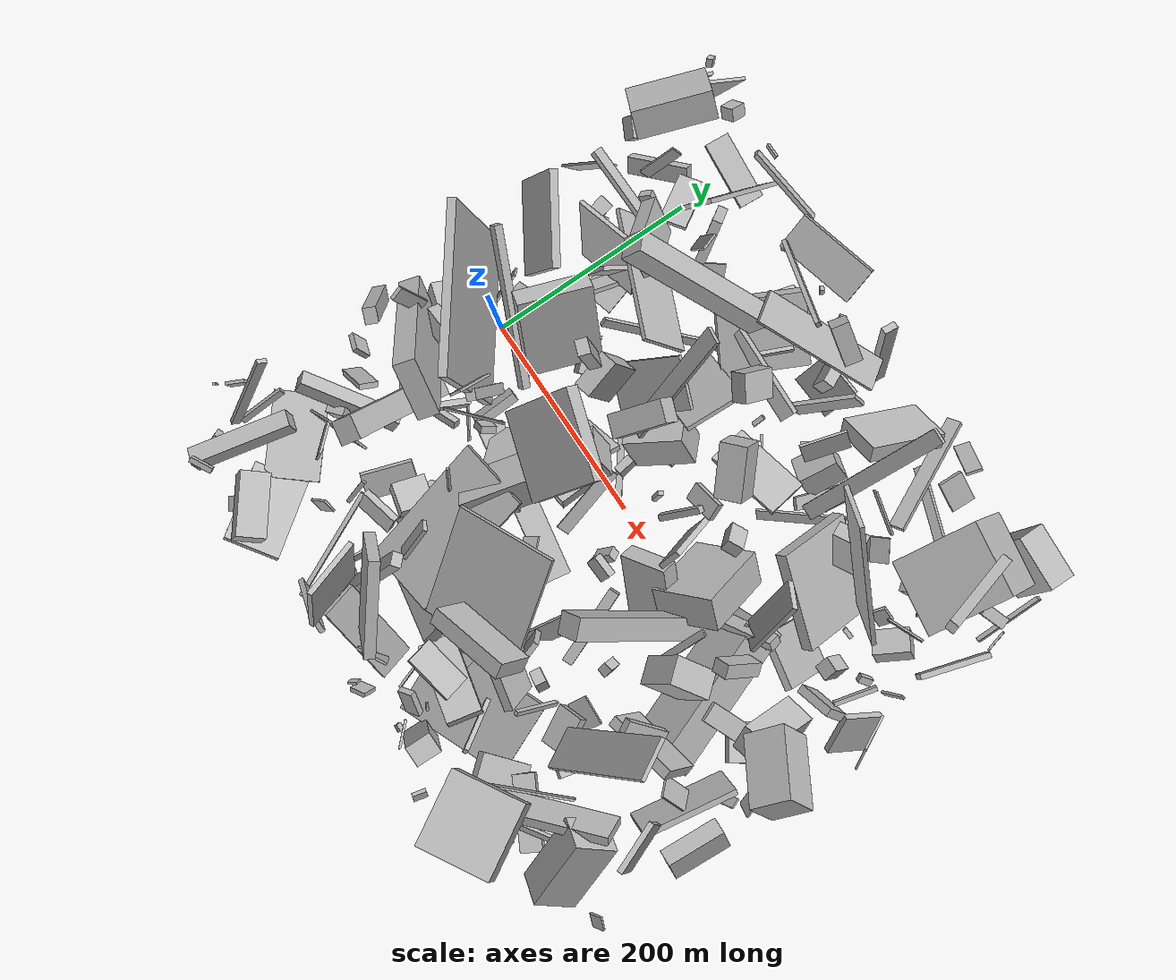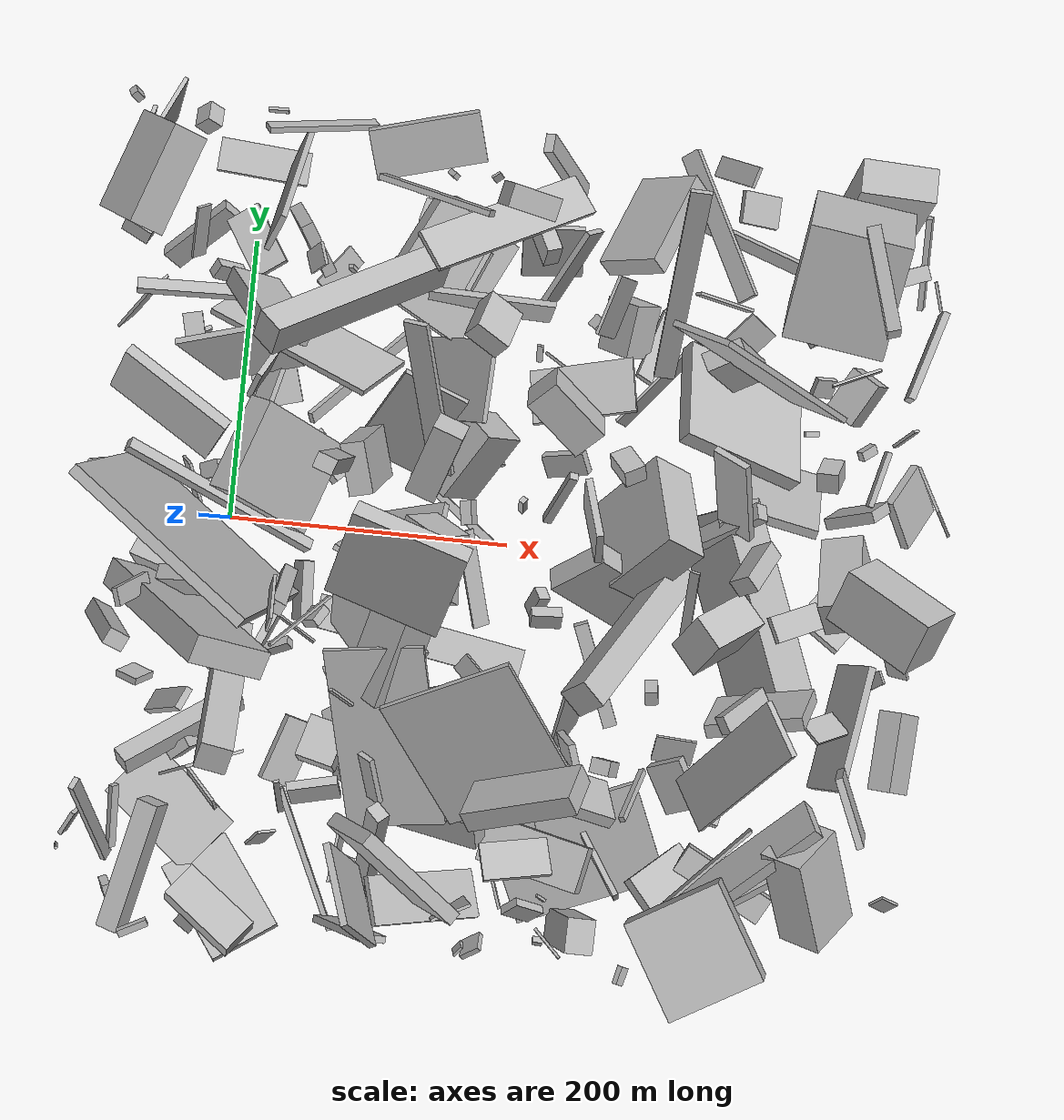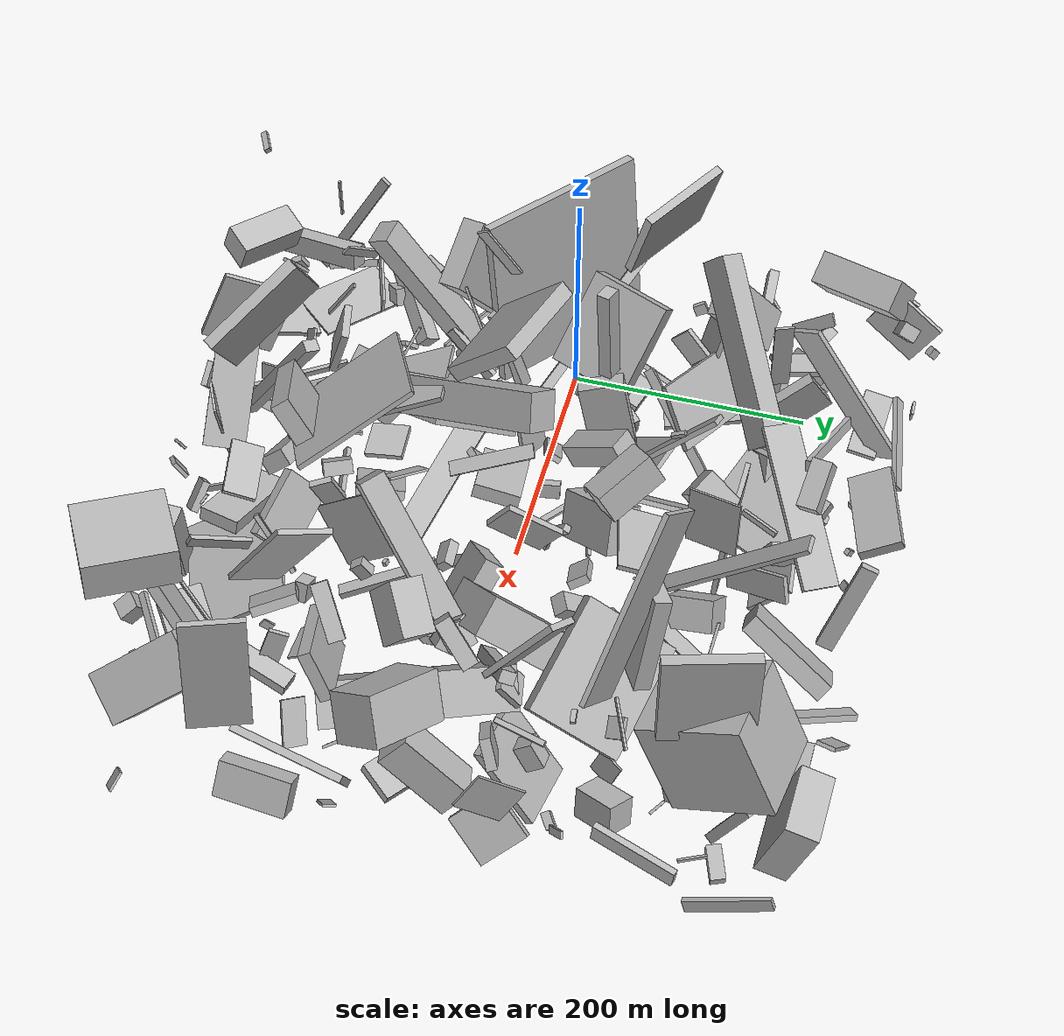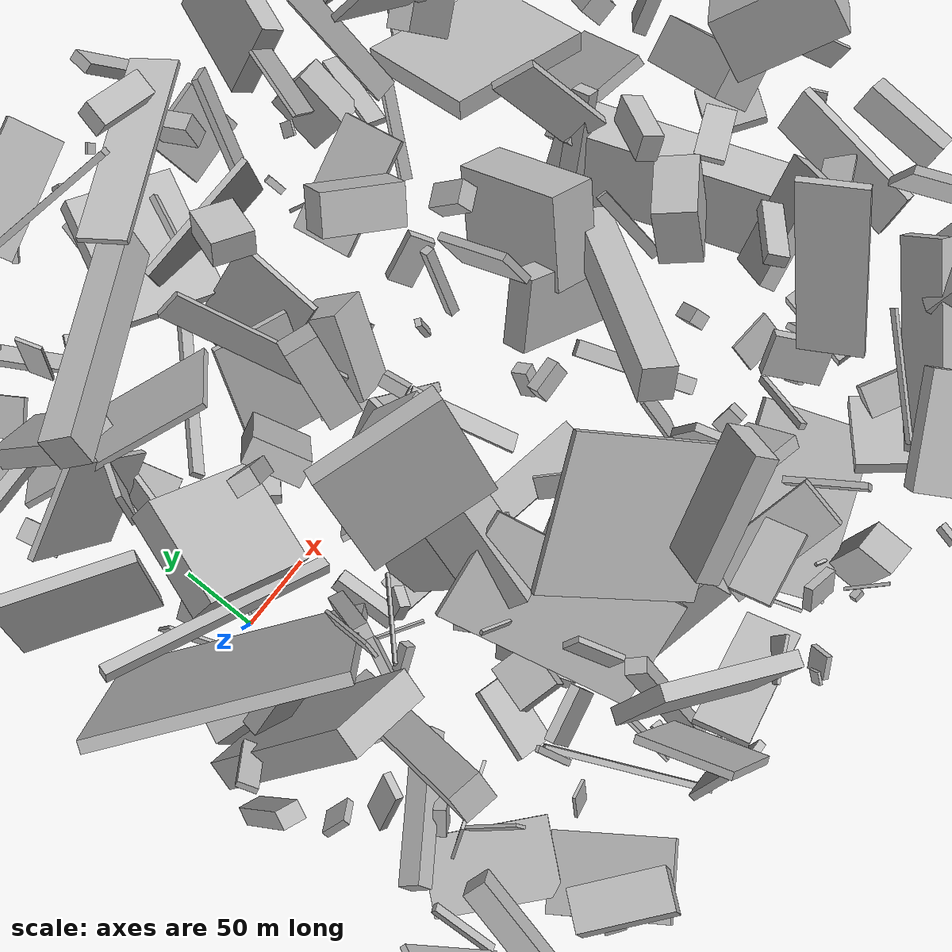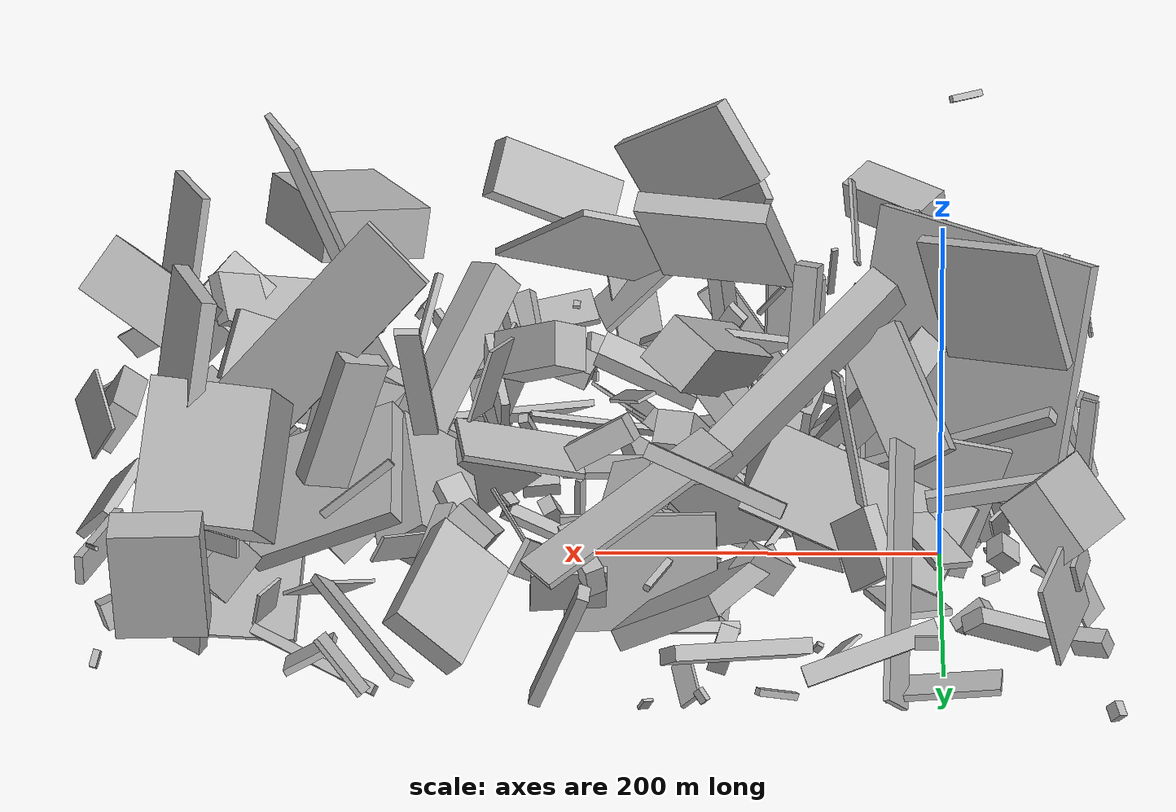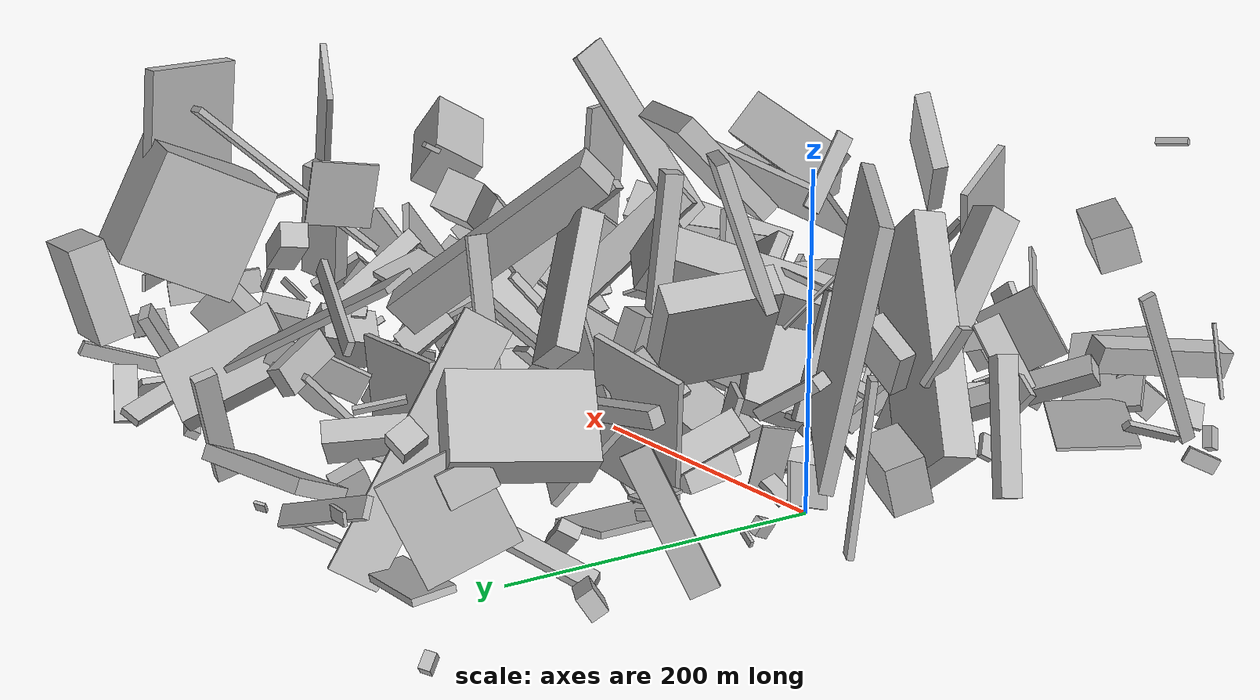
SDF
<sdf version="1.6">
 <world name="default">
  <scene>
   <sky><clouds><speed>12</speed></clouds></sky>
   <ambient>0.4 0.4 0.4 1</ambient>
   <background>0.7 0.7 0.7 1</background>
   <shadows>1</shadows>
  </scene>
  <gravity>0 0 -9.8066</gravity>
  <magnetic_field>6e-06 2.3e-05 -4.2e-05</magnetic_field>
  <physics default="0" name="default_physics" type="ode">
   <ode>
    <solver>
     <type>quick</type>
     <iters>10</iters>
     <sor>1.0</sor>
     <use_dynamic_moi_rescaling>0</use_dynamic_moi_rescaling>
    </solver>
    <constraints>
     <cfm>0</cfm>
     <erp>0.2</erp>
     <contact_max_correcting_vel>100</contact_max_correcting_vel>
     <contact_surface_layer>0.001</contact_surface_layer>
    </constraints>
   </ode>
   <max_step_size>0.004</max_step_size>
   <real_time_factor>1</real_time_factor>
   <real_time_update_rate>250</real_time_update_rate>
  </physics>
  <light name="sun" type="directional">
   <pose>0 0 10 0 0 0</pose>
   <diffuse>0.8 0.8 0.8 1</diffuse>
   <specular>0.2 0.2 0.2 1</specular>
   <attenuation>
    <range>1000</range>
    <constant>0.9</constant>
    <linear>0.01</linear>
    <quadratic>0.001</quadratic>
   </attenuation>
   <direction>-0.5 0.1 -0.9</direction>
  </light>
  <model name="building_1">
   <static>0</static>
   <pose>14.167553418681498 -128.4385211129559 86.4717740284772 1.0269178768683063 -0.1665577892159041 2.955657467043656</pose>
   <link name="link">
    <gravity>0</gravity>
    <pose>0 0 10.5 0 0 0</pose>
    <collision name="collision"><geometry><box><size>22 150 21</size></box></geometry></collision>
    <visual name="visual">
     <cast_shadows>0</cast_shadows>
     <geometry><box><size>22 150 21</size></box></geometry>
     <material>
      <script>
       <uri>model://HANNAS_wall/materials/scripts</uri>
       <uri>model://HANNAS_wall/materials/textures</uri>
       <name>vrc/HANNAS_wall</name>
      </script>
     </material>
    </visual>
   </link>
  </model>
  <model name="building_2">
   <static>0</static>
   <pose>152.42233029523481 9.300601098538692 126.22452351409257 -1.9900821503352017 0.5649265267559791 2.6356840387203686</pose>
   <link name="link">
    <gravity>0</gravity>
    <pose>0 0 66.5 0 0 0</pose>
    <collision name="collision"><geometry><box><size>32 32 133</size></box></geometry></collision>
    <visual name="visual">
     <cast_shadows>0</cast_shadows>
     <geometry><box><size>32 32 133</size></box></geometry>
     <material>
      <script>
       <uri>model://HANNAS_wall/materials/scripts</uri>
       <uri>model://HANNAS_wall/materials/textures</uri>
       <name>vrc/HANNAS_wall</name>
      </script>
     </material>
    </visual>
   </link>
  </model>
  <model name="building_3">
   <static>0</static>
   <pose>400.7232043774016 -100.26530416382178 36.819228830014104 1.5746231596231484 -0.6868995202137004 -2.7741150252003943</pose>
   <link name="link">
    <gravity>0</gravity>
    <pose>0 0 75.0 0 0 0</pose>
    <collision name="collision"><geometry><box><size>35 49 150</size></box></geometry></collision>
    <visual name="visual">
     <cast_shadows>0</cast_shadows>
     <geometry><box><size>35 49 150</size></box></geometry>
     <material>
      <script>
       <uri>model://HANNAS_wall/materials/scripts</uri>
       <uri>model://HANNAS_wall/materials/textures</uri>
       <name>vrc/HANNAS_wall</name>
      </script>
     </material>
    </visual>
   </link>
  </model>
  <model name="building_4">
   <static>0</static>
   <pose>42.096926980872 282.9988920719816 45.15552902809155 2.5614873497946133 -0.9766296485122589 -0.8965976631601812</pose>
   <link name="link">
    <gravity>0</gravity>
    <pose>0 0 2.0 0 0 0</pose>
    <collision name="collision"><geometry><box><size>12 79 4</size></box></geometry></collision>
    <visual name="visual">
     <cast_shadows>0</cast_shadows>
     <geometry><box><size>12 79 4</size></box></geometry>
     <material>
      <script>
       <uri>model://HANNAS_wall/materials/scripts</uri>
       <uri>model://HANNAS_wall/materials/textures</uri>
       <name>vrc/HANNAS_wall</name>
      </script>
     </material>
    </visual>
   </link>
  </model>
  <model name="building_5">
   <static>0</static>
   <pose>-17.961056952276753 -17.207184556817623 114.35984246697359 0.2839976143816802 -1.3792696738702126 -2.489850577921641</pose>
   <link name="link">
    <gravity>0</gravity>
    <pose>0 0 4.0 0 0 0</pose>
    <collision name="collision"><geometry><box><size>150 150 8</size></box></geometry></collision>
    <visual name="visual">
     <cast_shadows>0</cast_shadows>
     <geometry><box><size>150 150 8</size></box></geometry>
     <material>
      <script>
       <uri>model://HANNAS_wall/materials/scripts</uri>
       <uri>model://HANNAS_wall/materials/textures</uri>
       <name>vrc/HANNAS_wall</name>
      </script>
     </material>
    </visual>
   </link>
  </model>
  <model name="building_6">
   <static>0</static>
   <pose>249.8059960162078 -9.35989626910145 60.050411777133206 -2.4407371661502517 -0.5982015795128744 -1.425143302162848</pose>
   <link name="link">
    <gravity>0</gravity>
    <pose>0 0 39.5 0 0 0</pose>
    <collision name="collision"><geometry><box><size>17 48 79</size></box></geometry></collision>
    <visual name="visual">
     <cast_shadows>0</cast_shadows>
     <geometry><box><size>17 48 79</size></box></geometry>
     <material>
      <script>
       <uri>model://HANNAS_wall/materials/scripts</uri>
       <uri>model://HANNAS_wall/materials/textures</uri>
       <name>vrc/HANNAS_wall</name>
      </script>
     </material>
    </visual>
   </link>
  </model>
  <model name="building_7">
   <static>0</static>
   <pose>-35.88063882042383 195.4363901122762 31.777627158521067 2.6410717811342366 -0.5989881819409302 2.553978412977638</pose>
   <link name="link">
    <gravity>0</gravity>
    <pose>0 0 5.0 0 0 0</pose>
    <collision name="collision"><geometry><box><size>16 60 10</size></box></geometry></collision>
    <visual name="visual">
     <cast_shadows>0</cast_shadows>
     <geometry><box><size>16 60 10</size></box></geometry>
     <material>
      <script>
       <uri>model://HANNAS_wall/materials/scripts</uri>
       <uri>model://HANNAS_wall/materials/textures</uri>
       <name>vrc/HANNAS_wall</name>
      </script>
     </material>
    </visual>
   </link>
  </model>
  <model name="building_8">
   <static>0</static>
   <pose>283.82453941514325 -58.07409207703948 78.27835317954093 0.7826187650565872 -0.1846948708546161 2.349083935095155</pose>
   <link name="link">
    <gravity>0</gravity>
    <pose>0 0 12.0 0 0 0</pose>
    <collision name="collision"><geometry><box><size>21 150 24</size></box></geometry></collision>
    <visual name="visual">
     <cast_shadows>0</cast_shadows>
     <geometry><box><size>21 150 24</size></box></geometry>
     <material>
      <script>
       <uri>model://HANNAS_wall/materials/scripts</uri>
       <uri>model://HANNAS_wall/materials/textures</uri>
       <name>vrc/HANNAS_wall</name>
      </script>
     </material>
    </visual>
   </link>
  </model>
  <model name="building_9">
   <static>0</static>
   <pose>172.1837442272176 165.32553899334766 49.87654126402375 -2.7209618552122268 -1.4939852324768128 1.1256222110666152</pose>
   <link name="link">
    <gravity>0</gravity>
    <pose>0 0 2.0 0 0 0</pose>
    <collision name="collision"><geometry><box><size>71 88 4</size></box></geometry></collision>
    <visual name="visual">
     <cast_shadows>0</cast_shadows>
     <geometry><box><size>71 88 4</size></box></geometry>
     <material>
      <script>
       <uri>model://HANNAS_wall/materials/scripts</uri>
       <uri>model://HANNAS_wall/materials/textures</uri>
       <name>vrc/HANNAS_wall</name>
      </script>
     </material>
    </visual>
   </link>
  </model>
  <model name="building_10">
   <static>0</static>
   <pose>349.3916682355485 102.32726992485685 73.5909858808304 0.6535508878157551 -0.4247499859793586 2.8508436178994367</pose>
   <link name="link">
    <gravity>0</gravity>
    <pose>0 0 6.0 0 0 0</pose>
    <collision name="collision"><geometry><box><size>94 79 12</size></box></geometry></collision>
    <visual name="visual">
     <cast_shadows>0</cast_shadows>
     <geometry><box><size>94 79 12</size></box></geometry>
     <material>
      <script>
       <uri>model://HANNAS_wall/materials/scripts</uri>
       <uri>model://HANNAS_wall/materials/textures</uri>
       <name>vrc/HANNAS_wall</name>
      </script>
     </material>
    </visual>
   </link>
  </model>
  <model name="building_11">
   <static>0</static>
   <pose>342.0750665528675 -164.25402432366943 97.11386991848852 0.30846788776308837 -0.4633881316802767 -2.7723222896151545</pose>
   <link name="link">
    <gravity>0</gravity>
    <pose>0 0 75.0 0 0 0</pose>
    <collision name="collision"><geometry><box><size>4 39 150</size></box></geometry></collision>
    <visual name="visual">
     <cast_shadows>0</cast_shadows>
     <geometry><box><size>4 39 150</size></box></geometry>
     <material>
      <script>
       <uri>model://HANNAS_wall/materials/scripts</uri>
       <uri>model://HANNAS_wall/materials/textures</uri>
       <name>vrc/HANNAS_wall</name>
      </script>
     </material>
    </visual>
   </link>
  </model>
  <model name="building_12">
   <static>0</static>
   <pose>229.48509822428082 246.81121018663475 76.56518021819456 1.0808599442409188 -0.18571347631877108 -0.9684127808819307</pose>
   <link name="link">
    <gravity>0</gravity>
    <pose>0 0 65.0 0 0 0</pose>
    <collision name="collision"><geometry><box><size>30 4 130</size></box></geometry></collision>
    <visual name="visual">
     <cast_shadows>0</cast_shadows>
     <geometry><box><size>30 4 130</size></box></geometry>
     <material>
      <script>
       <uri>model://HANNAS_wall/materials/scripts</uri>
       <uri>model://HANNAS_wall/materials/textures</uri>
       <name>vrc/HANNAS_wall</name>
      </script>
     </material>
    </visual>
   </link>
  </model>
  <model name="building_13">
   <static>0</static>
   <pose>476.22596330048646 55.025035302774256 49.92848048790816 0.7145055037646388 -0.613770286919436 2.110345174796753</pose>
   <link name="link">
    <gravity>0</gravity>
    <pose>0 0 3.0 0 0 0</pose>
    <collision name="collision"><geometry><box><size>42 41 6</size></box></geometry></collision>
    <visual name="visual">
     <cast_shadows>0</cast_shadows>
     <geometry><box><size>42 41 6</size></box></geometry>
     <material>
      <script>
       <uri>model://HANNAS_wall/materials/scripts</uri>
       <uri>model://HANNAS_wall/materials/textures</uri>
       <name>vrc/HANNAS_wall</name>
      </script>
     </material>
    </visual>
   </link>
  </model>
  <model name="building_14">
   <static>0</static>
   <pose>239.23337273878616 221.9490028804767 78.75479436493148 2.0612796492238603 -0.2522621652858027 -0.6355748640469423</pose>
   <link name="link">
    <gravity>0</gravity>
    <pose>0 0 31.0 0 0 0</pose>
    <collision name="collision"><geometry><box><size>4 22 62</size></box></geometry></collision>
    <visual name="visual">
     <cast_shadows>0</cast_shadows>
     <geometry><box><size>4 22 62</size></box></geometry>
     <material>
      <script>
       <uri>model://HANNAS_wall/materials/scripts</uri>
       <uri>model://HANNAS_wall/materials/textures</uri>
       <name>vrc/HANNAS_wall</name>
      </script>
     </material>
    </visual>
   </link>
  </model>
  <model name="building_15">
   <static>0</static>
   <pose>256.10322530967653 -179.5139326060927 24.528524624304758 -1.9832252682769322 0.03601611775122781 -2.7498001587166243</pose>
   <link name="link">
    <gravity>0</gravity>
    <pose>0 0 41.5 0 0 0</pose>
    <collision name="collision"><geometry><box><size>112 4 83</size></box></geometry></collision>
    <visual name="visual">
     <cast_shadows>0</cast_shadows>
     <geometry><box><size>112 4 83</size></box></geometry>
     <material>
      <script>
       <uri>model://HANNAS_wall/materials/scripts</uri>
       <uri>model://HANNAS_wall/materials/textures</uri>
       <name>vrc/HANNAS_wall</name>
      </script>
     </material>
    </visual>
   </link>
  </model>
  <model name="building_16">
   <static>0</static>
   <pose>60.49876915282245 142.67490574462036 53.55372624333087 0.6424699418618434 -0.2744063656386967 -0.40605717008488196</pose>
   <link name="link">
    <gravity>0</gravity>
    <pose>0 0 27.5 0 0 0</pose>
    <collision name="collision"><geometry><box><size>127 4 55</size></box></geometry></collision>
    <visual name="visual">
     <cast_shadows>0</cast_shadows>
     <geometry><box><size>127 4 55</size></box></geometry>
     <material>
      <script>
       <uri>model://HANNAS_wall/materials/scripts</uri>
       <uri>model://HANNAS_wall/materials/textures</uri>
       <name>vrc/HANNAS_wall</name>
      </script>
     </material>
    </visual>
   </link>
  </model>
  <model name="building_17">
   <static>0</static>
   <pose>275.80232383729583 -220.3252380281648 66.06047719996454 -1.9225408868727267 0.03156974143122351 1.3616282650019396</pose>
   <link name="link">
    <gravity>0</gravity>
    <pose>0 0 38.5 0 0 0</pose>
    <collision name="collision"><geometry><box><size>33 11 77</size></box></geometry></collision>
    <visual name="visual">
     <cast_shadows>0</cast_shadows>
     <geometry><box><size>33 11 77</size></box></geometry>
     <material>
      <script>
       <uri>model://HANNAS_wall/materials/scripts</uri>
       <uri>model://HANNAS_wall/materials/textures</uri>
       <name>vrc/HANNAS_wall</name>
      </script>
     </material>
    </visual>
   </link>
  </model>
  <model name="building_18">
   <static>0</static>
   <pose>212.61524835058827 193.76816005071336 38.704160822750225 -0.748787733979258 0.03146018518226774 0.07830064401386899</pose>
   <link name="link">
    <gravity>0</gravity>
    <pose>0 0 21.5 0 0 0</pose>
    <collision name="collision"><geometry><box><size>43 4 43</size></box></geometry></collision>
    <visual name="visual">
     <cast_shadows>0</cast_shadows>
     <geometry><box><size>43 4 43</size></box></geometry>
     <material>
      <script>
       <uri>model://HANNAS_wall/materials/scripts</uri>
       <uri>model://HANNAS_wall/materials/textures</uri>
       <name>vrc/HANNAS_wall</name>
      </script>
     </material>
    </visual>
   </link>
  </model>
  <model name="building_19">
   <static>0</static>
   <pose>317.66948863064147 39.43663740661593 59.19337390758678 2.3729776062961343 -0.6907638690431864 -1.3672699431326427</pose>
   <link name="link">
    <gravity>0</gravity>
    <pose>0 0 31.0 0 0 0</pose>
    <collision name="collision"><geometry><box><size>77 33 62</size></box></geometry></collision>
    <visual name="visual">
     <cast_shadows>0</cast_shadows>
     <geometry><box><size>77 33 62</size></box></geometry>
     <material>
      <script>
       <uri>model://HANNAS_wall/materials/scripts</uri>
       <uri>model://HANNAS_wall/materials/textures</uri>
       <name>vrc/HANNAS_wall</name>
      </script>
     </material>
    </visual>
   </link>
  </model>
  <model name="building_20">
   <static>0</static>
   <pose>455.6300632716984 -153.53637858365113 69.32458853663478 -0.061413059446901036 -0.12822496730034946 0.4000631064691787</pose>
   <link name="link">
    <gravity>0</gravity>
    <pose>0 0 53.0 0 0 0</pose>
    <collision name="collision"><geometry><box><size>5 48 106</size></box></geometry></collision>
    <visual name="visual">
     <cast_shadows>0</cast_shadows>
     <geometry><box><size>5 48 106</size></box></geometry>
     <material>
      <script>
       <uri>model://HANNAS_wall/materials/scripts</uri>
       <uri>model://HANNAS_wall/materials/textures</uri>
       <name>vrc/HANNAS_wall</name>
      </script>
     </material>
    </visual>
   </link>
  </model>
  <model name="building_21">
   <static>0</static>
   <pose>102.45086113861157 31.846263380389416 73.79373037577506 0.8201469944164821 -1.2658715717765194 -2.144439866136028</pose>
   <link name="link">
    <gravity>0</gravity>
    <pose>0 0 18.5 0 0 0</pose>
    <collision name="collision"><geometry><box><size>59 17 37</size></box></geometry></collision>
    <visual name="visual">
     <cast_shadows>0</cast_shadows>
     <geometry><box><size>59 17 37</size></box></geometry>
     <material>
      <script>
       <uri>model://HANNAS_wall/materials/scripts</uri>
       <uri>model://HANNAS_wall/materials/textures</uri>
       <name>vrc/HANNAS_wall</name>
      </script>
     </material>
    </visual>
   </link>
  </model>
  <model name="building_22">
   <static>0</static>
   <pose>203.31202137733933 -280.55106483838466 21.639780489372612 0.49846990535975133 -0.4425933166383371 0.600996795183263</pose>
   <link name="link">
    <gravity>0</gravity>
    <pose>0 0 8.0 0 0 0</pose>
    <collision name="collision"><geometry><box><size>16 4 16</size></box></geometry></collision>
    <visual name="visual">
     <cast_shadows>0</cast_shadows>
     <geometry><box><size>16 4 16</size></box></geometry>
     <material>
      <script>
       <uri>model://HANNAS_wall/materials/scripts</uri>
       <uri>model://HANNAS_wall/materials/textures</uri>
       <name>vrc/HANNAS_wall</name>
      </script>
     </material>
    </visual>
   </link>
  </model>
  <model name="building_23">
   <static>0</static>
   <pose>115.91938954572889 -282.1856681553513 43.727112781264076 1.5741132704764333 -0.6018587251410455 3.0609200199020803</pose>
   <link name="link">
    <gravity>0</gravity>
    <pose>0 0 2.5 0 0 0</pose>
    <collision name="collision"><geometry><box><size>21 65 5</size></box></geometry></collision>
    <visual name="visual">
     <cast_shadows>0</cast_shadows>
     <geometry><box><size>21 65 5</size></box></geometry>
     <material>
      <script>
       <uri>model://HANNAS_wall/materials/scripts</uri>
       <uri>model://HANNAS_wall/materials/textures</uri>
       <name>vrc/HANNAS_wall</name>
      </script>
     </material>
    </visual>
   </link>
  </model>
  <model name="building_24">
   <static>0</static>
   <pose>291.91103221347555 149.31748298249272 60.06666547251819 2.817948339687129 -0.5257673515670295 -1.887484205575589</pose>
   <link name="link">
    <gravity>0</gravity>
    <pose>0 0 2.0 0 0 0</pose>
    <collision name="collision"><geometry><box><size>60 12 4</size></box></geometry></collision>
    <visual name="visual">
     <cast_shadows>0</cast_shadows>
     <geometry><box><size>60 12 4</size></box></geometry>
     <material>
      <script>
       <uri>model://HANNAS_wall/materials/scripts</uri>
       <uri>model://HANNAS_wall/materials/textures</uri>
       <name>vrc/HANNAS_wall</name>
      </script>
     </material>
    </visual>
   </link>
  </model>
  <model name="building_25">
   <static>0</static>
   <pose>437.33232358384225 255.41760869629286 48.93130082673491 -0.04354635736238333 -0.2560853431122381 -1.6002613684149918</pose>
   <link name="link">
    <gravity>0</gravity>
    <pose>0 0 34.0 0 0 0</pose>
    <collision name="collision"><geometry><box><size>25 52 68</size></box></geometry></collision>
    <visual name="visual">
     <cast_shadows>0</cast_shadows>
     <geometry><box><size>25 52 68</size></box></geometry>
     <material>
      <script>
       <uri>model://HANNAS_wall/materials/scripts</uri>
       <uri>model://HANNAS_wall/materials/textures</uri>
       <name>vrc/HANNAS_wall</name>
      </script>
     </material>
    </visual>
   </link>
  </model>
  <model name="building_26">
   <static>0</static>
   <pose>23.459761342440395 50.82115027640816 21.65610436838669 0.2724773046648117 0.2986560567105044 1.2732314970203737</pose>
   <link name="link">
    <gravity>0</gravity>
    <pose>0 0 9.5 0 0 0</pose>
    <collision name="collision"><geometry><box><size>31 27 19</size></box></geometry></collision>
    <visual name="visual">
     <cast_shadows>0</cast_shadows>
     <geometry><box><size>31 27 19</size></box></geometry>
     <material>
      <script>
       <uri>model://HANNAS_wall/materials/scripts</uri>
       <uri>model://HANNAS_wall/materials/textures</uri>
       <name>vrc/HANNAS_wall</name>
      </script>
     </material>
    </visual>
   </link>
  </model>
  <model name="building_27">
   <static>0</static>
   <pose>-25.24261606161491 107.71383338074524 64.36000130535865 1.3027196394352996 0.2556428231968021 1.7552546998250067</pose>
   <link name="link">
    <gravity>0</gravity>
    <pose>0 0 30.5 0 0 0</pose>
    <collision name="collision"><geometry><box><size>4 88 61</size></box></geometry></collision>
    <visual name="visual">
     <cast_shadows>0</cast_shadows>
     <geometry><box><size>4 88 61</size></box></geometry>
     <material>
      <script>
       <uri>model://HANNAS_wall/materials/scripts</uri>
       <uri>model://HANNAS_wall/materials/textures</uri>
       <name>vrc/HANNAS_wall</name>
      </script>
     </material>
    </visual>
   </link>
  </model>
  <model name="building_28">
   <static>0</static>
   <pose>15.742415745526994 75.45590572815752 45.309912809821164 2.561096155473627 -0.7797399080218421 0.22382917311245695</pose>
   <link name="link">
    <gravity>0</gravity>
    <pose>0 0 2.0 0 0 0</pose>
    <collision name="collision"><geometry><box><size>19 76 4</size></box></geometry></collision>
    <visual name="visual">
     <cast_shadows>0</cast_shadows>
     <geometry><box><size>19 76 4</size></box></geometry>
     <material>
      <script>
       <uri>model://HANNAS_wall/materials/scripts</uri>
       <uri>model://HANNAS_wall/materials/textures</uri>
       <name>vrc/HANNAS_wall</name>
      </script>
     </material>
    </visual>
   </link>
  </model>
  <model name="building_29">
   <static>0</static>
   <pose>161.65502159185326 -229.4057410338438 91.71723709342442 -1.2527995280689277 -0.765357492756513 -3.090254694429837</pose>
   <link name="link">
    <gravity>0</gravity>
    <pose>0 0 17.0 0 0 0</pose>
    <collision name="collision"><geometry><box><size>96 4 34</size></box></geometry></collision>
    <visual name="visual">
     <cast_shadows>0</cast_shadows>
     <geometry><box><size>96 4 34</size></box></geometry>
     <material>
      <script>
       <uri>model://HANNAS_wall/materials/scripts</uri>
       <uri>model://HANNAS_wall/materials/textures</uri>
       <name>vrc/HANNAS_wall</name>
      </script>
     </material>
    </visual>
   </link>
  </model>
  <model name="building_30">
   <static>0</static>
   <pose>320.5811360759748 -242.96147282906216 25.59845704083638 -2.1562574136717734 -0.08900785039896718 -0.8705907861708161</pose>
   <link name="link">
    <gravity>0</gravity>
    <pose>0 0 26.0 0 0 0</pose>
    <collision name="collision"><geometry><box><size>37 9 52</size></box></geometry></collision>
    <visual name="visual">
     <cast_shadows>0</cast_shadows>
     <geometry><box><size>37 9 52</size></box></geometry>
     <material>
      <script>
       <uri>model://HANNAS_wall/materials/scripts</uri>
       <uri>model://HANNAS_wall/materials/textures</uri>
       <name>vrc/HANNAS_wall</name>
      </script>
     </material>
    </visual>
   </link>
  </model>
  <model name="building_31">
   <static>0</static>
   <pose>-71.12173607689023 -217.81904068819807 67.67773377378983 1.0272851538388221 -1.0304022449760055 1.7855317427410022</pose>
   <link name="link">
    <gravity>0</gravity>
    <pose>0 0 2.0 0 0 0</pose>
    <collision name="collision"><geometry><box><size>117 9 4</size></box></geometry></collision>
    <visual name="visual">
     <cast_shadows>0</cast_shadows>
     <geometry><box><size>117 9 4</size></box></geometry>
     <material>
      <script>
       <uri>model://HANNAS_wall/materials/scripts</uri>
       <uri>model://HANNAS_wall/materials/textures</uri>
       <name>vrc/HANNAS_wall</name>
      </script>
     </material>
    </visual>
   </link>
  </model>
  <model name="building_32">
   <static>0</static>
   <pose>151.5416675359984 113.1220202769631 38.90093236110823 -0.8540106399498949 0.004329102594364371 1.5262706384560505</pose>
   <link name="link">
    <gravity>0</gravity>
    <pose>0 0 2.0 0 0 0</pose>
    <collision name="collision"><geometry><box><size>58 83 4</size></box></geometry></collision>
    <visual name="visual">
     <cast_shadows>0</cast_shadows>
     <geometry><box><size>58 83 4</size></box></geometry>
     <material>
      <script>
       <uri>model://HANNAS_wall/materials/scripts</uri>
       <uri>model://HANNAS_wall/materials/textures</uri>
       <name>vrc/HANNAS_wall</name>
      </script>
     </material>
    </visual>
   </link>
  </model>
  <model name="building_33">
   <static>0</static>
   <pose>157.6785712201397 226.69217224111304 40.62006326729352 -1.5080656141921909 -0.47793407802932747 2.658161037450032</pose>
   <link name="link">
    <gravity>0</gravity>
    <pose>0 0 41.0 0 0 0</pose>
    <collision name="collision"><geometry><box><size>70 13 82</size></box></geometry></collision>
    <visual name="visual">
     <cast_shadows>0</cast_shadows>
     <geometry><box><size>70 13 82</size></box></geometry>
     <material>
      <script>
       <uri>model://HANNAS_wall/materials/scripts</uri>
       <uri>model://HANNAS_wall/materials/textures</uri>
       <name>vrc/HANNAS_wall</name>
      </script>
     </material>
    </visual>
   </link>
  </model>
  <model name="building_34">
   <static>0</static>
   <pose>77.00392377610508 -237.8559256962605 17.65682385530406 1.4703786863304507 1.3690345414308702 1.8783712399257677</pose>
   <link name="link">
    <gravity>0</gravity>
    <pose>0 0 2.0 0 0 0</pose>
    <collision name="collision"><geometry><box><size>5 111 4</size></box></geometry></collision>
    <visual name="visual">
     <cast_shadows>0</cast_shadows>
     <geometry><box><size>5 111 4</size></box></geometry>
     <material>
      <script>
       <uri>model://HANNAS_wall/materials/scripts</uri>
       <uri>model://HANNAS_wall/materials/textures</uri>
       <name>vrc/HANNAS_wall</name>
      </script>
     </material>
    </visual>
   </link>
  </model>
  <model name="building_35">
   <static>0</static>
   <pose>440.37714078266754 128.89351869209287 30.326729292973454 0.33700126294885036 0.25615929235676976 -2.0681124052917355</pose>
   <link name="link">
    <gravity>0</gravity>
    <pose>0 0 12.0 0 0 0</pose>
    <collision name="collision"><geometry><box><size>34 23 24</size></box></geometry></collision>
    <visual name="visual">
     <cast_shadows>0</cast_shadows>
     <geometry><box><size>34 23 24</size></box></geometry>
     <material>
      <script>
       <uri>model://HANNAS_wall/materials/scripts</uri>
       <uri>model://HANNAS_wall/materials/textures</uri>
       <name>vrc/HANNAS_wall</name>
      </script>
     </material>
    </visual>
   </link>
  </model>
  <model name="building_36">
   <static>0</static>
   <pose>345.0100710728461 74.01044800332367 124.65826033682245 -2.572017452332013 -0.42730659409162414 -2.30638103768517</pose>
   <link name="link">
    <gravity>0</gravity>
    <pose>0 0 38.5 0 0 0</pose>
    <collision name="collision"><geometry><box><size>5 28 77</size></box></geometry></collision>
    <visual name="visual">
     <cast_shadows>0</cast_shadows>
     <geometry><box><size>5 28 77</size></box></geometry>
     <material>
      <script>
       <uri>model://HANNAS_wall/materials/scripts</uri>
       <uri>model://HANNAS_wall/materials/textures</uri>
       <name>vrc/HANNAS_wall</name>
      </script>
     </material>
    </visual>
   </link>
  </model>
  <model name="building_37">
   <static>0</static>
   <pose>342.7870898554146 -56.39201421093652 86.16651222179708 0.5749660632005441 0.2207653361713216 2.2697604486269203</pose>
   <link name="link">
    <gravity>0</gravity>
    <pose>0 0 21.5 0 0 0</pose>
    <collision name="collision"><geometry><box><size>26 43 43</size></box></geometry></collision>
    <visual name="visual">
     <cast_shadows>0</cast_shadows>
     <geometry><box><size>26 43 43</size></box></geometry>
     <material>
      <script>
       <uri>model://HANNAS_wall/materials/scripts</uri>
       <uri>model://HANNAS_wall/materials/textures</uri>
       <name>vrc/HANNAS_wall</name>
      </script>
     </material>
    </visual>
   </link>
  </model>
  <model name="building_38">
   <static>0</static>
   <pose>122.61260703813824 -126.76806173273553 36.624197765709035 -1.6933191804896528 0.12758014650047617 -1.5352733530291771</pose>
   <link name="link">
    <gravity>0</gravity>
    <pose>0 0 15.5 0 0 0</pose>
    <collision name="collision"><geometry><box><size>32 5 31</size></box></geometry></collision>
    <visual name="visual">
     <cast_shadows>0</cast_shadows>
     <geometry><box><size>32 5 31</size></box></geometry>
     <material>
      <script>
       <uri>model://HANNAS_wall/materials/scripts</uri>
       <uri>model://HANNAS_wall/materials/textures</uri>
       <name>vrc/HANNAS_wall</name>
      </script>
     </material>
    </visual>
   </link>
  </model>
  <model name="building_39">
   <static>0</static>
   <pose>460.48556344403187 215.51236503256763 37.234120739768585 -0.3211005590233174 0.07317322246782806 -1.2219230318242558</pose>
   <link name="link">
    <gravity>0</gravity>
    <pose>0 0 8.0 0 0 0</pose>
    <collision name="collision"><geometry><box><size>11 25 16</size></box></geometry></collision>
    <visual name="visual">
     <cast_shadows>0</cast_shadows>
     <geometry><box><size>11 25 16</size></box></geometry>
     <material>
      <script>
       <uri>model://HANNAS_wall/materials/scripts</uri>
       <uri>model://HANNAS_wall/materials/textures</uri>
       <name>vrc/HANNAS_wall</name>
      </script>
     </material>
    </visual>
   </link>
  </model>
  <model name="building_40">
   <static>0</static>
   <pose>91.74232952677555 114.98618038016922 54.275255315298566 0.760561872734806 -0.618972989703657 1.9173274964065592</pose>
   <link name="link">
    <gravity>0</gravity>
    <pose>0 0 2.0 0 0 0</pose>
    <collision name="collision"><geometry><box><size>8 131 4</size></box></geometry></collision>
    <visual name="visual">
     <cast_shadows>0</cast_shadows>
     <geometry><box><size>8 131 4</size></box></geometry>
     <material>
      <script>
       <uri>model://HANNAS_wall/materials/scripts</uri>
       <uri>model://HANNAS_wall/materials/textures</uri>
       <name>vrc/HANNAS_wall</name>
      </script>
     </material>
    </visual>
   </link>
  </model>
  <model name="building_41">
   <static>0</static>
   <pose>0.21186698337289656 243.91762181542816 16.746223878311223 2.4772218470482303 1.4076971234457663 -2.299200870163506</pose>
   <link name="link">
    <gravity>0</gravity>
    <pose>0 0 12.0 0 0 0</pose>
    <collision name="collision"><geometry><box><size>4 65 24</size></box></geometry></collision>
    <visual name="visual">
     <cast_shadows>0</cast_shadows>
     <geometry><box><size>4 65 24</size></box></geometry>
     <material>
      <script>
       <uri>model://HANNAS_wall/materials/scripts</uri>
       <uri>model://HANNAS_wall/materials/textures</uri>
       <name>vrc/HANNAS_wall</name>
      </script>
     </material>
    </visual>
   </link>
  </model>
  <model name="building_42">
   <static>0</static>
   <pose>218.45062146106616 -84.93931416702812 23.06443049843098 -1.1192822073408293 -1.4296665798428694 0.9473396144382871</pose>
   <link name="link">
    <gravity>0</gravity>
    <pose>0 0 75.0 0 0 0</pose>
    <collision name="collision"><geometry><box><size>4 24 150</size></box></geometry></collision>
    <visual name="visual">
     <cast_shadows>0</cast_shadows>
     <geometry><box><size>4 24 150</size></box></geometry>
     <material>
      <script>
       <uri>model://HANNAS_wall/materials/scripts</uri>
       <uri>model://HANNAS_wall/materials/textures</uri>
       <name>vrc/HANNAS_wall</name>
      </script>
     </material>
    </visual>
   </link>
  </model>
  <model name="building_43">
   <static>0</static>
   <pose>177.01295174001393 -244.9247773489519 148.10159401469008 1.0707601082096345 -0.2146266852913278 -2.161396804426114</pose>
   <link name="link">
    <gravity>0</gravity>
    <pose>0 0 45.5 0 0 0</pose>
    <collision name="collision"><geometry><box><size>10 53 91</size></box></geometry></collision>
    <visual name="visual">
     <cast_shadows>0</cast_shadows>
     <geometry><box><size>10 53 91</size></box></geometry>
     <material>
      <script>
       <uri>model://HANNAS_wall/materials/scripts</uri>
       <uri>model://HANNAS_wall/materials/textures</uri>
       <name>vrc/HANNAS_wall</name>
      </script>
     </material>
    </visual>
   </link>
  </model>
  <model name="building_44">
   <static>0</static>
   <pose>-59.731344857448974 -195.89416044890996 34.81261046220553 1.9930609223651006 -0.6924546302940384 -0.28740478855786455</pose>
   <link name="link">
    <gravity>0</gravity>
    <pose>0 0 24.0 0 0 0</pose>
    <collision name="collision"><geometry><box><size>4 6 48</size></box></geometry></collision>
    <visual name="visual">
     <cast_shadows>0</cast_shadows>
     <geometry><box><size>4 6 48</size></box></geometry>
     <material>
      <script>
       <uri>model://HANNAS_wall/materials/scripts</uri>
       <uri>model://HANNAS_wall/materials/textures</uri>
       <name>vrc/HANNAS_wall</name>
      </script>
     </material>
    </visual>
   </link>
  </model>
  <model name="building_45">
   <static>0</static>
   <pose>120.80255049454676 -169.68069466629393 86.25298110559275 2.2484199312301363 0.7157048544326549 2.7209666175936036</pose>
   <link name="link">
    <gravity>0</gravity>
    <pose>0 0 2.0 0 0 0</pose>
    <collision name="collision"><geometry><box><size>13 39 4</size></box></geometry></collision>
    <visual name="visual">
     <cast_shadows>0</cast_shadows>
     <geometry><box><size>13 39 4</size></box></geometry>
     <material>
      <script>
       <uri>model://HANNAS_wall/materials/scripts</uri>
       <uri>model://HANNAS_wall/materials/textures</uri>
       <name>vrc/HANNAS_wall</name>
      </script>
     </material>
    </visual>
   </link>
  </model>
  <model name="building_46">
   <static>0</static>
   <pose>24.581769167013213 233.9079767213592 73.91647865820991 1.7916880451371118 -0.5267914129509113 1.1098553724860225</pose>
   <link name="link">
    <gravity>0</gravity>
    <pose>0 0 2.0 0 0 0</pose>
    <collision name="collision"><geometry><box><size>28 150 4</size></box></geometry></collision>
    <visual name="visual">
     <cast_shadows>0</cast_shadows>
     <geometry><box><size>28 150 4</size></box></geometry>
     <material>
      <script>
       <uri>model://HANNAS_wall/materials/scripts</uri>
       <uri>model://HANNAS_wall/materials/textures</uri>
       <name>vrc/HANNAS_wall</name>
      </script>
     </material>
    </visual>
   </link>
  </model>
  <model name="building_47">
   <static>0</static>
   <pose>21.404137272646036 -125.42198294280135 34.26859883090836 1.0875869183643108 -0.612547241246844 -0.6798426465221342</pose>
   <link name="link">
    <gravity>0</gravity>
    <pose>0 0 48.0 0 0 0</pose>
    <collision name="collision"><geometry><box><size>15 13 96</size></box></geometry></collision>
    <visual name="visual">
     <cast_shadows>0</cast_shadows>
     <geometry><box><size>15 13 96</size></box></geometry>
     <material>
      <script>
       <uri>model://HANNAS_wall/materials/scripts</uri>
       <uri>model://HANNAS_wall/materials/textures</uri>
       <name>vrc/HANNAS_wall</name>
      </script>
     </material>
    </visual>
   </link>
  </model>
  <model name="building_48">
   <static>0</static>
   <pose>0.9185182569056458 16.05612232567306 75.20910910591914 -2.5817223938836484 -0.40113878775696615 2.708077581698563</pose>
   <link name="link">
    <gravity>0</gravity>
    <pose>0 0 4.0 0 0 0</pose>
    <collision name="collision"><geometry><box><size>150 8 8</size></box></geometry></collision>
    <visual name="visual">
     <cast_shadows>0</cast_shadows>
     <geometry><box><size>150 8 8</size></box></geometry>
     <material>
      <script>
       <uri>model://HANNAS_wall/materials/scripts</uri>
       <uri>model://HANNAS_wall/materials/textures</uri>
       <name>vrc/HANNAS_wall</name>
      </script>
     </material>
    </visual>
   </link>
  </model>
  <model name="building_49">
   <static>0</static>
   <pose>86.66063074167242 41.93246513726297 150.8931528731307 -2.068247010331143 1.4712553646527113 0.7341699141451893</pose>
   <link name="link">
    <gravity>0</gravity>
    <pose>0 0 7.0 0 0 0</pose>
    <collision name="collision"><geometry><box><size>83 11 14</size></box></geometry></collision>
    <visual name="visual">
     <cast_shadows>0</cast_shadows>
     <geometry><box><size>83 11 14</size></box></geometry>
     <material>
      <script>
       <uri>model://HANNAS_wall/materials/scripts</uri>
       <uri>model://HANNAS_wall/materials/textures</uri>
       <name>vrc/HANNAS_wall</name>
      </script>
     </material>
    </visual>
   </link>
  </model>
  <model name="building_50">
   <static>0</static>
   <pose>130.08542213150906 -218.13000926275885 71.9219222392597 -1.105740864446861 0.3581091720272023 2.3885547113511634</pose>
   <link name="link">
    <gravity>0</gravity>
    <pose>0 0 5.0 0 0 0</pose>
    <collision name="collision"><geometry><box><size>13 124 10</size></box></geometry></collision>
    <visual name="visual">
     <cast_shadows>0</cast_shadows>
     <geometry><box><size>13 124 10</size></box></geometry>
     <material>
      <script>
       <uri>model://HANNAS_wall/materials/scripts</uri>
       <uri>model://HANNAS_wall/materials/textures</uri>
       <name>vrc/HANNAS_wall</name>
      </script>
     </material>
    </visual>
   </link>
  </model>
  <model name="building_51">
   <static>0</static>
   <pose>257.2610780205307 14.029951884063063 100.75902783209997 0.6472720785679406 -0.09924337517018453 -2.951900712644226</pose>
   <link name="link">
    <gravity>0</gravity>
    <pose>0 0 14.5 0 0 0</pose>
    <collision name="collision"><geometry><box><size>5 50 29</size></box></geometry></collision>
    <visual name="visual">
     <cast_shadows>0</cast_shadows>
     <geometry><box><size>5 50 29</size></box></geometry>
     <material>
      <script>
       <uri>model://HANNAS_wall/materials/scripts</uri>
       <uri>model://HANNAS_wall/materials/textures</uri>
       <name>vrc/HANNAS_wall</name>
      </script>
     </material>
    </visual>
   </link>
  </model>
  <model name="building_52">
   <static>0</static>
   <pose>-18.060024421739353 -80.3688731226014 89.30021594419927 -1.3232069196400766 -0.9335774583299064 -0.4986220546433001</pose>
   <link name="link">
    <gravity>0</gravity>
    <pose>0 0 10.0 0 0 0</pose>
    <collision name="collision"><geometry><box><size>150 57 20</size></box></geometry></collision>
    <visual name="visual">
     <cast_shadows>0</cast_shadows>
     <geometry><box><size>150 57 20</size></box></geometry>
     <material>
      <script>
       <uri>model://HANNAS_wall/materials/scripts</uri>
       <uri>model://HANNAS_wall/materials/textures</uri>
       <name>vrc/HANNAS_wall</name>
      </script>
     </material>
    </visual>
   </link>
  </model>
  <model name="building_53">
   <static>0</static>
   <pose>400.7106434574868 111.9386753954937 119.36921296670712 -0.006293187863851989 -0.7145801039412174 -0.34941741395422776</pose>
   <link name="link">
    <gravity>0</gravity>
    <pose>0 0 75.0 0 0 0</pose>
    <collision name="collision"><geometry><box><size>48 4 150</size></box></geometry></collision>
    <visual name="visual">
     <cast_shadows>0</cast_shadows>
     <geometry><box><size>48 4 150</size></box></geometry>
     <material>
      <script>
       <uri>model://HANNAS_wall/materials/scripts</uri>
       <uri>model://HANNAS_wall/materials/textures</uri>
       <name>vrc/HANNAS_wall</name>
      </script>
     </material>
    </visual>
   </link>
  </model>
  <model name="building_54">
   <static>0</static>
   <pose>26.304677418278185 111.4302920119732 82.17824292562936 0.9372469886001725 0.04054813314128904 -0.4699355250626714</pose>
   <link name="link">
    <gravity>0</gravity>
    <pose>0 0 13.5 0 0 0</pose>
    <collision name="collision"><geometry><box><size>4 28 27</size></box></geometry></collision>
    <visual name="visual">
     <cast_shadows>0</cast_shadows>
     <geometry><box><size>4 28 27</size></box></geometry>
     <material>
      <script>
       <uri>model://HANNAS_wall/materials/scripts</uri>
       <uri>model://HANNAS_wall/materials/textures</uri>
       <name>vrc/HANNAS_wall</name>
      </script>
     </material>
    </visual>
   </link>
  </model>
  <model name="building_55">
   <static>0</static>
   <pose>294.34741307467766 124.6659244268466 118.38746883575033 -0.8548562881266696 0.041120613764117055 -0.02408567908058497</pose>
   <link name="link">
    <gravity>0</gravity>
    <pose>0 0 75.0 0 0 0</pose>
    <collision name="collision"><geometry><box><size>14 4 150</size></box></geometry></collision>
    <visual name="visual">
     <cast_shadows>0</cast_shadows>
     <geometry><box><size>14 4 150</size></box></geometry>
     <material>
      <script>
       <uri>model://HANNAS_wall/materials/scripts</uri>
       <uri>model://HANNAS_wall/materials/textures</uri>
       <name>vrc/HANNAS_wall</name>
      </script>
     </material>
    </visual>
   </link>
  </model>
  <model name="building_56">
   <static>0</static>
   <pose>301.6837406844121 -160.57449679944932 90.04643139995792 -2.2499242430518294 -0.9132109262256742 -1.9810352446705801</pose>
   <link name="link">
    <gravity>0</gravity>
    <pose>0 0 2.0 0 0 0</pose>
    <collision name="collision"><geometry><box><size>55 4 4</size></box></geometry></collision>
    <visual name="visual">
     <cast_shadows>0</cast_shadows>
     <geometry><box><size>55 4 4</size></box></geometry>
     <material>
      <script>
       <uri>model://HANNAS_wall/materials/scripts</uri>
       <uri>model://HANNAS_wall/materials/textures</uri>
       <name>vrc/HANNAS_wall</name>
      </script>
     </material>
    </visual>
   </link>
  </model>
  <model name="building_57">
   <static>0</static>
   <pose>80.62958397713695 -166.17266528502563 42.38449304388496 2.5591331132634325 -1.2462699287944417 1.9014290133863538</pose>
   <link name="link">
    <gravity>0</gravity>
    <pose>0 0 15.5 0 0 0</pose>
    <collision name="collision"><geometry><box><size>17 28 31</size></box></geometry></collision>
    <visual name="visual">
     <cast_shadows>0</cast_shadows>
     <geometry><box><size>17 28 31</size></box></geometry>
     <material>
      <script>
       <uri>model://HANNAS_wall/materials/scripts</uri>
       <uri>model://HANNAS_wall/materials/textures</uri>
       <name>vrc/HANNAS_wall</name>
      </script>
     </material>
    </visual>
   </link>
  </model>
  <model name="building_58">
   <static>0</static>
   <pose>284.0725906182624 228.69690941253634 53.98500768876988 0.8139213473627945 -0.4456234440804293 -1.9469502249276551</pose>
   <link name="link">
    <gravity>0</gravity>
    <pose>0 0 7.5 0 0 0</pose>
    <collision name="collision"><geometry><box><size>77 48 15</size></box></geometry></collision>
    <visual name="visual">
     <cast_shadows>0</cast_shadows>
     <geometry><box><size>77 48 15</size></box></geometry>
     <material>
      <script>
       <uri>model://HANNAS_wall/materials/scripts</uri>
       <uri>model://HANNAS_wall/materials/textures</uri>
       <name>vrc/HANNAS_wall</name>
      </script>
     </material>
    </visual>
   </link>
  </model>
  <model name="building_59">
   <static>0</static>
   <pose>431.34216529290785 194.8392648867563 155.7864545866241 -0.014089760076854245 -0.14219865048703761 0.292946306840055</pose>
   <link name="link">
    <gravity>0</gravity>
    <pose>0 0 37.0 0 0 0</pose>
    <collision name="collision"><geometry><box><size>9 68 74</size></box></geometry></collision>
    <visual name="visual">
     <cast_shadows>0</cast_shadows>
     <geometry><box><size>9 68 74</size></box></geometry>
     <material>
      <script>
       <uri>model://HANNAS_wall/materials/scripts</uri>
       <uri>model://HANNAS_wall/materials/textures</uri>
       <name>vrc/HANNAS_wall</name>
      </script>
     </material>
    </visual>
   </link>
  </model>
  <model name="building_60">
   <static>0</static>
   <pose>181.66629111289356 83.9836842231261 35.72566355148956 2.289998716340971 0.9608352932238879 0.052463613633189805</pose>
   <link name="link">
    <gravity>0</gravity>
    <pose>0 0 28.5 0 0 0</pose>
    <collision name="collision"><geometry><box><size>39 30 57</size></box></geometry></collision>
    <visual name="visual">
     <cast_shadows>0</cast_shadows>
     <geometry><box><size>39 30 57</size></box></geometry>
     <material>
      <script>
       <uri>model://HANNAS_wall/materials/scripts</uri>
       <uri>model://HANNAS_wall/materials/textures</uri>
       <name>vrc/HANNAS_wall</name>
      </script>
     </material>
    </visual>
   </link>
  </model>
  <model name="building_61">
   <static>0</static>
   <pose>342.03449516944664 -170.9782879215725 56.28383366656549 1.352079697462719 0.5762649123531494 -2.754709867919487</pose>
   <link name="link">
    <gravity>0</gravity>
    <pose>0 0 18.5 0 0 0</pose>
    <collision name="collision"><geometry><box><size>27 8 37</size></box></geometry></collision>
    <visual name="visual">
     <cast_shadows>0</cast_shadows>
     <geometry><box><size>27 8 37</size></box></geometry>
     <material>
      <script>
       <uri>model://HANNAS_wall/materials/scripts</uri>
       <uri>model://HANNAS_wall/materials/textures</uri>
       <name>vrc/HANNAS_wall</name>
      </script>
     </material>
    </visual>
   </link>
  </model>
  <model name="building_62">
   <static>0</static>
   <pose>-35.03556692489687 -246.25740978692903 56.19131936656756 -0.13443319802915094 0.2860597285468246 2.8700702685809136</pose>
   <link name="link">
    <gravity>0</gravity>
    <pose>0 0 9.0 0 0 0</pose>
    <collision name="collision"><geometry><box><size>16 95 18</size></box></geometry></collision>
    <visual name="visual">
     <cast_shadows>0</cast_shadows>
     <geometry><box><size>16 95 18</size></box></geometry>
     <material>
      <script>
       <uri>model://HANNAS_wall/materials/scripts</uri>
       <uri>model://HANNAS_wall/materials/textures</uri>
       <name>vrc/HANNAS_wall</name>
      </script>
     </material>
    </visual>
   </link>
  </model>
  <model name="building_63">
   <static>0</static>
   <pose>453.70757129632057 -37.60251704392006 137.69188865606054 0.6964917036857154 -0.878199727571596 -2.6859942797668612</pose>
   <link name="link">
    <gravity>0</gravity>
    <pose>0 0 19.5 0 0 0</pose>
    <collision name="collision"><geometry><box><size>38 66 39</size></box></geometry></collision>
    <visual name="visual">
     <cast_shadows>0</cast_shadows>
     <geometry><box><size>38 66 39</size></box></geometry>
     <material>
      <script>
       <uri>model://HANNAS_wall/materials/scripts</uri>
       <uri>model://HANNAS_wall/materials/textures</uri>
       <name>vrc/HANNAS_wall</name>
      </script>
     </material>
    </visual>
   </link>
  </model>
  <model name="building_64">
   <static>0</static>
   <pose>1.8953227690901562 -247.52507813845241 124.44477711188475 -1.424487490771508 -0.33004359681682727 -2.2520825917623406</pose>
   <link name="link">
    <gravity>0</gravity>
    <pose>0 0 28.5 0 0 0</pose>
    <collision name="collision"><geometry><box><size>26 25 57</size></box></geometry></collision>
    <visual name="visual">
     <cast_shadows>0</cast_shadows>
     <geometry><box><size>26 25 57</size></box></geometry>
     <material>
      <script>
       <uri>model://HANNAS_wall/materials/scripts</uri>
       <uri>model://HANNAS_wall/materials/textures</uri>
       <name>vrc/HANNAS_wall</name>
      </script>
     </material>
    </visual>
   </link>
  </model>
  <model name="building_65">
   <static>0</static>
   <pose>57.15799730744064 -24.94617569178102 10.798545434280392 -1.6849319292666494 1.0028521789742992 3.085202482956319</pose>
   <link name="link">
    <gravity>0</gravity>
    <pose>0 0 21.5 0 0 0</pose>
    <collision name="collision"><geometry><box><size>13 9 43</size></box></geometry></collision>
    <visual name="visual">
     <cast_shadows>0</cast_shadows>
     <geometry><box><size>13 9 43</size></box></geometry>
     <material>
      <script>
       <uri>model://HANNAS_wall/materials/scripts</uri>
       <uri>model://HANNAS_wall/materials/textures</uri>
       <name>vrc/HANNAS_wall</name>
      </script>
     </material>
    </visual>
   </link>
  </model>
  <model name="building_66">
   <static>0</static>
   <pose>389.00644775721867 -251.35146654442886 24.913412805955144 -2.9186980805046154 -1.0122162704660531 -2.4811601793955247</pose>
   <link name="link">
    <gravity>0</gravity>
    <pose>0 0 2.0 0 0 0</pose>
    <collision name="collision"><geometry><box><size>10 5 4</size></box></geometry></collision>
    <visual name="visual">
     <cast_shadows>0</cast_shadows>
     <geometry><box><size>10 5 4</size></box></geometry>
     <material>
      <script>
       <uri>model://HANNAS_wall/materials/scripts</uri>
       <uri>model://HANNAS_wall/materials/textures</uri>
       <name>vrc/HANNAS_wall</name>
      </script>
     </material>
    </visual>
   </link>
  </model>
  <model name="building_67">
   <static>0</static>
   <pose>374.63086365784727 -160.3002726774081 15.95091853002203 -1.6543916277716617 -1.3280688763675144 1.409454460571306</pose>
   <link name="link">
    <gravity>0</gravity>
    <pose>0 0 8.0 0 0 0</pose>
    <collision name="collision"><geometry><box><size>11 52 16</size></box></geometry></collision>
    <visual name="visual">
     <cast_shadows>0</cast_shadows>
     <geometry><box><size>11 52 16</size></box></geometry>
     <material>
      <script>
       <uri>model://HANNAS_wall/materials/scripts</uri>
       <uri>model://HANNAS_wall/materials/textures</uri>
       <name>vrc/HANNAS_wall</name>
      </script>
     </material>
    </visual>
   </link>
  </model>
  <model name="building_68">
   <static>0</static>
   <pose>137.5747591793177 96.70649619365679 82.11651513001433 0.7812156430565892 -0.44776774662785984 -0.14934844607636158</pose>
   <link name="link">
    <gravity>0</gravity>
    <pose>0 0 2.0 0 0 0</pose>
    <collision name="collision"><geometry><box><size>18 129 4</size></box></geometry></collision>
    <visual name="visual">
     <cast_shadows>0</cast_shadows>
     <geometry><box><size>18 129 4</size></box></geometry>
     <material>
      <script>
       <uri>model://HANNAS_wall/materials/scripts</uri>
       <uri>model://HANNAS_wall/materials/textures</uri>
       <name>vrc/HANNAS_wall</name>
      </script>
     </material>
    </visual>
   </link>
  </model>
  <model name="building_69">
   <static>0</static>
   <pose>423.58658630744253 -27.499558955287103 43.62927521306019 -1.0193027162067871 0.0683366388946676 1.9913909757215567</pose>
   <link name="link">
    <gravity>0</gravity>
    <pose>0 0 21.0 0 0 0</pose>
    <collision name="collision"><geometry><box><size>19 4 42</size></box></geometry></collision>
    <visual name="visual">
     <cast_shadows>0</cast_shadows>
     <geometry><box><size>19 4 42</size></box></geometry>
     <material>
      <script>
       <uri>model://HANNAS_wall/materials/scripts</uri>
       <uri>model://HANNAS_wall/materials/textures</uri>
       <name>vrc/HANNAS_wall</name>
      </script>
     </material>
    </visual>
   </link>
  </model>
  <model name="building_70">
   <static>0</static>
   <pose>129.81385448852578 -139.02095389712804 80.79505045384651 -0.3979820448608111 0.174179334488106 -3.0033013531506327</pose>
   <link name="link">
    <gravity>0</gravity>
    <pose>0 0 2.0 0 0 0</pose>
    <collision name="collision"><geometry><box><size>70 136 4</size></box></geometry></collision>
    <visual name="visual">
     <cast_shadows>0</cast_shadows>
     <geometry><box><size>70 136 4</size></box></geometry>
     <material>
      <script>
       <uri>model://HANNAS_wall/materials/scripts</uri>
       <uri>model://HANNAS_wall/materials/textures</uri>
       <name>vrc/HANNAS_wall</name>
      </script>
     </material>
    </visual>
   </link>
  </model>
  <model name="building_71">
   <static>0</static>
   <pose>134.95249990710266 184.67322444478677 117.29870709316087 0.8837518963767844 -0.36605665634446577 -0.7346794803478616</pose>
   <link name="link">
    <gravity>0</gravity>
    <pose>0 0 75.0 0 0 0</pose>
    <collision name="collision"><geometry><box><size>20 23 150</size></box></geometry></collision>
    <visual name="visual">
     <cast_shadows>0</cast_shadows>
     <geometry><box><size>20 23 150</size></box></geometry>
     <material>
      <script>
       <uri>model://HANNAS_wall/materials/scripts</uri>
       <uri>model://HANNAS_wall/materials/textures</uri>
       <name>vrc/HANNAS_wall</name>
      </script>
     </material>
    </visual>
   </link>
  </model>
  <model name="building_72">
   <static>0</static>
   <pose>129.17239955117816 228.41572052936635 126.89058756726115 0.9238021145227862 -1.1354190412993392 -2.7177885702513462</pose>
   <link name="link">
    <gravity>0</gravity>
    <pose>0 0 2.0 0 0 0</pose>
    <collision name="collision"><geometry><box><size>9 85 4</size></box></geometry></collision>
    <visual name="visual">
     <cast_shadows>0</cast_shadows>
     <geometry><box><size>9 85 4</size></box></geometry>
     <material>
      <script>
       <uri>model://HANNAS_wall/materials/scripts</uri>
       <uri>model://HANNAS_wall/materials/textures</uri>
       <name>vrc/HANNAS_wall</name>
      </script>
     </material>
    </visual>
   </link>
  </model>
  <model name="building_73">
   <static>0</static>
   <pose>82.71819072292082 -9.148102581305162 29.063035980696164 -1.2228439190487665 -1.3115070430664932 -2.370105602138723</pose>
   <link name="link">
    <gravity>0</gravity>
    <pose>0 0 13.5 0 0 0</pose>
    <collision name="collision"><geometry><box><size>38 4 27</size></box></geometry></collision>
    <visual name="visual">
     <cast_shadows>0</cast_shadows>
     <geometry><box><size>38 4 27</size></box></geometry>
     <material>
      <script>
       <uri>model://HANNAS_wall/materials/scripts</uri>
       <uri>model://HANNAS_wall/materials/textures</uri>
       <name>vrc/HANNAS_wall</name>
      </script>
     </material>
    </visual>
   </link>
  </model>
  <model name="building_74">
   <static>0</static>
   <pose>238.5132757127583 127.9159019829206 98.03634476546848 1.296981847227757 -0.2285636660358127 0.21826736881247227</pose>
   <link name="link">
    <gravity>0</gravity>
    <pose>0 0 19.0 0 0 0</pose>
    <collision name="collision"><geometry><box><size>72 4 38</size></box></geometry></collision>
    <visual name="visual">
     <cast_shadows>0</cast_shadows>
     <geometry><box><size>72 4 38</size></box></geometry>
     <material>
      <script>
       <uri>model://HANNAS_wall/materials/scripts</uri>
       <uri>model://HANNAS_wall/materials/textures</uri>
       <name>vrc/HANNAS_wall</name>
      </script>
     </material>
    </visual>
   </link>
  </model>
  <model name="building_75">
   <static>0</static>
   <pose>378.9665400062952 -199.55402995482305 68.71775584187155 0.58449938243396 -0.28144017469549026 0.7641359160350393</pose>
   <link name="link">
    <gravity>0</gravity>
    <pose>0 0 15.5 0 0 0</pose>
    <collision name="collision"><geometry><box><size>129 9 31</size></box></geometry></collision>
    <visual name="visual">
     <cast_shadows>0</cast_shadows>
     <geometry><box><size>129 9 31</size></box></geometry>
     <material>
      <script>
       <uri>model://HANNAS_wall/materials/scripts</uri>
       <uri>model://HANNAS_wall/materials/textures</uri>
       <name>vrc/HANNAS_wall</name>
      </script>
     </material>
    </visual>
   </link>
  </model>
  <model name="building_76">
   <static>0</static>
   <pose>335.17853056322235 -228.04115863604432 118.4510870282873 -1.1456977090863483 -1.430021187443493 -3.031741256014587</pose>
   <link name="link">
    <gravity>0</gravity>
    <pose>0 0 36.0 0 0 0</pose>
    <collision name="collision"><geometry><box><size>32 70 72</size></box></geometry></collision>
    <visual name="visual">
     <cast_shadows>0</cast_shadows>
     <geometry><box><size>32 70 72</size></box></geometry>
     <material>
      <script>
       <uri>model://HANNAS_wall/materials/scripts</uri>
       <uri>model://HANNAS_wall/materials/textures</uri>
       <name>vrc/HANNAS_wall</name>
      </script>
     </material>
    </visual>
   </link>
  </model>
  <model name="building_77">
   <static>0</static>
   <pose>455.8642511644523 -60.75334609800657 28.488894410486484 -1.411188696959997 -0.4510194526232841 2.901392364432419</pose>
   <link name="link">
    <gravity>0</gravity>
    <pose>0 0 45.5 0 0 0</pose>
    <collision name="collision"><geometry><box><size>6 39 91</size></box></geometry></collision>
    <visual name="visual">
     <cast_shadows>0</cast_shadows>
     <geometry><box><size>6 39 91</size></box></geometry>
     <material>
      <script>
       <uri>model://HANNAS_wall/materials/scripts</uri>
       <uri>model://HANNAS_wall/materials/textures</uri>
       <name>vrc/HANNAS_wall</name>
      </script>
     </material>
    </visual>
   </link>
  </model>
  <model name="building_78">
   <static>0</static>
   <pose>190.37337611935817 -148.0967305183933 24.541949124553405 -0.9268081945098159 0.19524713065919536 -2.9118855316253764</pose>
   <link name="link">
    <gravity>0</gravity>
    <pose>0 0 2.0 0 0 0</pose>
    <collision name="collision"><geometry><box><size>106 6 4</size></box></geometry></collision>
    <visual name="visual">
     <cast_shadows>0</cast_shadows>
     <geometry><box><size>106 6 4</size></box></geometry>
     <material>
      <script>
       <uri>model://HANNAS_wall/materials/scripts</uri>
       <uri>model://HANNAS_wall/materials/textures</uri>
       <name>vrc/HANNAS_wall</name>
      </script>
     </material>
    </visual>
   </link>
  </model>
  <model name="building_79">
   <static>0</static>
   <pose>41.82411314279655 194.99452376280638 75.91360563969086 1.613600862075014 -0.5361223149123683 2.116547844480711</pose>
   <link name="link">
    <gravity>0</gravity>
    <pose>0 0 4.5 0 0 0</pose>
    <collision name="collision"><geometry><box><size>41 41 9</size></box></geometry></collision>
    <visual name="visual">
     <cast_shadows>0</cast_shadows>
     <geometry><box><size>41 41 9</size></box></geometry>
     <material>
      <script>
       <uri>model://HANNAS_wall/materials/scripts</uri>
       <uri>model://HANNAS_wall/materials/textures</uri>
       <name>vrc/HANNAS_wall</name>
      </script>
     </material>
    </visual>
   </link>
  </model>
  <model name="building_80">
   <static>0</static>
   <pose>446.25060877278156 68.4785522777939 128.05815517789685 -1.17869596853251 0.0440624799986621 1.3221318205698755</pose>
   <link name="link">
    <gravity>0</gravity>
    <pose>0 0 2.0 0 0 0</pose>
    <collision name="collision"><geometry><box><size>39 4 4</size></box></geometry></collision>
    <visual name="visual">
     <cast_shadows>0</cast_shadows>
     <geometry><box><size>39 4 4</size></box></geometry>
     <material>
      <script>
       <uri>model://HANNAS_wall/materials/scripts</uri>
       <uri>model://HANNAS_wall/materials/textures</uri>
       <name>vrc/HANNAS_wall</name>
      </script>
     </material>
    </visual>
   </link>
  </model>
  <model name="building_81">
   <static>0</static>
   <pose>183.76205360622504 -118.93189009528858 22.859686040570452 -2.8775550541175092 -0.9529834735342866 -3.139402621615978</pose>
   <link name="link">
    <gravity>0</gravity>
    <pose>0 0 27.5 0 0 0</pose>
    <collision name="collision"><geometry><box><size>8 40 55</size></box></geometry></collision>
    <visual name="visual">
     <cast_shadows>0</cast_shadows>
     <geometry><box><size>8 40 55</size></box></geometry>
     <material>
      <script>
       <uri>model://HANNAS_wall/materials/scripts</uri>
       <uri>model://HANNAS_wall/materials/textures</uri>
       <name>vrc/HANNAS_wall</name>
      </script>
     </material>
    </visual>
   </link>
  </model>
  <model name="building_82">
   <static>0</static>
   <pose>405.59590806093286 127.7666078524358 99.91618201187363 2.563763675464144 0.512432709078715 -1.823949339402601</pose>
   <link name="link">
    <gravity>0</gravity>
    <pose>0 0 2.0 0 0 0</pose>
    <collision name="collision"><geometry><box><size>14 16 4</size></box></geometry></collision>
    <visual name="visual">
     <cast_shadows>0</cast_shadows>
     <geometry><box><size>14 16 4</size></box></geometry>
     <material>
      <script>
       <uri>model://HANNAS_wall/materials/scripts</uri>
       <uri>model://HANNAS_wall/materials/textures</uri>
       <name>vrc/HANNAS_wall</name>
      </script>
     </material>
    </visual>
   </link>
  </model>
  <model name="building_83">
   <static>0</static>
   <pose>378.692360575143 -234.49550290713046 44.729598898674986 2.256088524381262 -0.0017739532466718826 0.5760848912105392</pose>
   <link name="link">
    <gravity>0</gravity>
    <pose>0 0 3.0 0 0 0</pose>
    <collision name="collision"><geometry><box><size>90 4 6</size></box></geometry></collision>
    <visual name="visual">
     <cast_shadows>0</cast_shadows>
     <geometry><box><size>90 4 6</size></box></geometry>
     <material>
      <script>
       <uri>model://HANNAS_wall/materials/scripts</uri>
       <uri>model://HANNAS_wall/materials/textures</uri>
       <name>vrc/HANNAS_wall</name>
      </script>
     </material>
    </visual>
   </link>
  </model>
  <model name="building_84">
   <static>0</static>
   <pose>3.830412802898927 111.66089949103365 14.124271670825188 -1.580256828080733 0.11166927472663302 -1.2960013006563287</pose>
   <link name="link">
    <gravity>0</gravity>
    <pose>0 0 16.5 0 0 0</pose>
    <collision name="collision"><geometry><box><size>67 4 33</size></box></geometry></collision>
    <visual name="visual">
     <cast_shadows>0</cast_shadows>
     <geometry><box><size>67 4 33</size></box></geometry>
     <material>
      <script>
       <uri>model://HANNAS_wall/materials/scripts</uri>
       <uri>model://HANNAS_wall/materials/textures</uri>
       <name>vrc/HANNAS_wall</name>
      </script>
     </material>
    </visual>
   </link>
  </model>
  <model name="building_85">
   <static>0</static>
   <pose>161.19960800051376 189.29158090085713 57.674093801411765 2.9582077475473914 -0.4130568547110429 -0.3272084377911734</pose>
   <link name="link">
    <gravity>0</gravity>
    <pose>0 0 2.0 0 0 0</pose>
    <collision name="collision"><geometry><box><size>4 32 4</size></box></geometry></collision>
    <visual name="visual">
     <cast_shadows>0</cast_shadows>
     <geometry><box><size>4 32 4</size></box></geometry>
     <material>
      <script>
       <uri>model://HANNAS_wall/materials/scripts</uri>
       <uri>model://HANNAS_wall/materials/textures</uri>
       <name>vrc/HANNAS_wall</name>
      </script>
     </material>
    </visual>
   </link>
  </model>
  <model name="building_86">
   <static>0</static>
   <pose>450.1639106515763 90.75383849006136 29.426572197452867 2.7174561136163535 -0.4134281092547173 -2.510542884081294</pose>
   <link name="link">
    <gravity>0</gravity>
    <pose>0 0 3.0 0 0 0</pose>
    <collision name="collision"><geometry><box><size>13 7 6</size></box></geometry></collision>
    <visual name="visual">
     <cast_shadows>0</cast_shadows>
     <geometry><box><size>13 7 6</size></box></geometry>
     <material>
      <script>
       <uri>model://HANNAS_wall/materials/scripts</uri>
       <uri>model://HANNAS_wall/materials/textures</uri>
       <name>vrc/HANNAS_wall</name>
      </script>
     </material>
    </visual>
   </link>
  </model>
  <model name="building_87">
   <static>0</static>
   <pose>79.00849768677497 265.3218452734974 41.504796183092076 1.5388375983981977 -0.41333605852350114 1.8458585883518386</pose>
   <link name="link">
    <gravity>0</gravity>
    <pose>0 0 39.5 0 0 0</pose>
    <collision name="collision"><geometry><box><size>36 9 79</size></box></geometry></collision>
    <visual name="visual">
     <cast_shadows>0</cast_shadows>
     <geometry><box><size>36 9 79</size></box></geometry>
     <material>
      <script>
       <uri>model://HANNAS_wall/materials/scripts</uri>
       <uri>model://HANNAS_wall/materials/textures</uri>
       <name>vrc/HANNAS_wall</name>
      </script>
     </material>
    </visual>
   </link>
  </model>
  <model name="building_88">
   <static>0</static>
   <pose>-84.7504277012542 32.02086546142266 54.69824919135526 1.5050878787879722 -0.08823910062599832 1.060327351548515</pose>
   <link name="link">
    <gravity>0</gravity>
    <pose>0 0 5.0 0 0 0</pose>
    <collision name="collision"><geometry><box><size>4 101 10</size></box></geometry></collision>
    <visual name="visual">
     <cast_shadows>0</cast_shadows>
     <geometry><box><size>4 101 10</size></box></geometry>
     <material>
      <script>
       <uri>model://HANNAS_wall/materials/scripts</uri>
       <uri>model://HANNAS_wall/materials/textures</uri>
       <name>vrc/HANNAS_wall</name>
      </script>
     </material>
    </visual>
   </link>
  </model>
  <model name="building_89">
   <static>0</static>
   <pose>78.92464250827265 36.97795186631538 21.822795056075485 1.490695301946631 -0.24965683342504505 -2.375994911768439</pose>
   <link name="link">
    <gravity>0</gravity>
    <pose>0 0 18.5 0 0 0</pose>
    <collision name="collision"><geometry><box><size>14 20 37</size></box></geometry></collision>
    <visual name="visual">
     <cast_shadows>0</cast_shadows>
     <geometry><box><size>14 20 37</size></box></geometry>
     <material>
      <script>
       <uri>model://HANNAS_wall/materials/scripts</uri>
       <uri>model://HANNAS_wall/materials/textures</uri>
       <name>vrc/HANNAS_wall</name>
      </script>
     </material>
    </visual>
   </link>
  </model>
  <model name="building_90">
   <static>0</static>
   <pose>-26.41346465355104 268.8447337281282 96.67308029547891 0.8017011022150139 -0.5005838987385095 -1.5571899116833932</pose>
   <link name="link">
    <gravity>0</gravity>
    <pose>0 0 6.0 0 0 0</pose>
    <collision name="collision"><geometry><box><size>15 14 12</size></box></geometry></collision>
    <visual name="visual">
     <cast_shadows>0</cast_shadows>
     <geometry><box><size>15 14 12</size></box></geometry>
     <material>
      <script>
       <uri>model://HANNAS_wall/materials/scripts</uri>
       <uri>model://HANNAS_wall/materials/textures</uri>
       <name>vrc/HANNAS_wall</name>
      </script>
     </material>
    </visual>
   </link>
  </model>
  <model name="building_91">
   <static>0</static>
   <pose>134.87672359609644 261.964418627514 12.181159679398286 2.3410454015406263 -0.025687105266667128 0.955254663790249</pose>
   <link name="link">
    <gravity>0</gravity>
    <pose>0 0 2.5 0 0 0</pose>
    <collision name="collision"><geometry><box><size>4 8 5</size></box></geometry></collision>
    <visual name="visual">
     <cast_shadows>0</cast_shadows>
     <geometry><box><size>4 8 5</size></box></geometry>
     <material>
      <script>
       <uri>model://HANNAS_wall/materials/scripts</uri>
       <uri>model://HANNAS_wall/materials/textures</uri>
       <name>vrc/HANNAS_wall</name>
      </script>
     </material>
    </visual>
   </link>
  </model>
  <model name="building_92">
   <static>0</static>
   <pose>83.55662447409391 253.29931992467147 7.702056708117101 -1.2516581342038744 -0.02632075797590579 -0.9109849777625056</pose>
   <link name="link">
    <gravity>0</gravity>
    <pose>0 0 14.5 0 0 0</pose>
    <collision name="collision"><geometry><box><size>4 4 29</size></box></geometry></collision>
    <visual name="visual">
     <cast_shadows>0</cast_shadows>
     <geometry><box><size>4 4 29</size></box></geometry>
     <material>
      <script>
       <uri>model://HANNAS_wall/materials/scripts</uri>
       <uri>model://HANNAS_wall/materials/textures</uri>
       <name>vrc/HANNAS_wall</name>
      </script>
     </material>
    </visual>
   </link>
  </model>
  <model name="building_93">
   <static>0</static>
   <pose>-2.655198550285738 185.32912642338286 76.9664814968375 -1.2025206232160837 1.2292253906236614 -0.6190943176380629</pose>
   <link name="link">
    <gravity>0</gravity>
    <pose>0 0 12.5 0 0 0</pose>
    <collision name="collision"><geometry><box><size>4 49 25</size></box></geometry></collision>
    <visual name="visual">
     <cast_shadows>0</cast_shadows>
     <geometry><box><size>4 49 25</size></box></geometry>
     <material>
      <script>
       <uri>model://HANNAS_wall/materials/scripts</uri>
       <uri>model://HANNAS_wall/materials/textures</uri>
       <name>vrc/HANNAS_wall</name>
      </script>
     </material>
    </visual>
   </link>
  </model>
  <model name="building_94">
   <static>0</static>
   <pose>194.2150375081659 -135.2967480162499 145.6976247948564 2.791481305953773 -0.49091473433358496 2.181394052836374</pose>
   <link name="link">
    <gravity>0</gravity>
    <pose>0 0 2.0 0 0 0</pose>
    <collision name="collision"><geometry><box><size>106 95 4</size></box></geometry></collision>
    <visual name="visual">
     <cast_shadows>0</cast_shadows>
     <geometry><box><size>106 95 4</size></box></geometry>
     <material>
      <script>
       <uri>model://HANNAS_wall/materials/scripts</uri>
       <uri>model://HANNAS_wall/materials/textures</uri>
       <name>vrc/HANNAS_wall</name>
      </script>
     </material>
    </visual>
   </link>
  </model>
  <model name="building_95">
   <static>0</static>
   <pose>273.7248488906518 70.18704893144238 47.54533790742657 -0.7844700713215164 -0.21889407537329275 -2.6709768269853287</pose>
   <link name="link">
    <gravity>0</gravity>
    <pose>0 0 12.0 0 0 0</pose>
    <collision name="collision"><geometry><box><size>16 13 24</size></box></geometry></collision>
    <visual name="visual">
     <cast_shadows>0</cast_shadows>
     <geometry><box><size>16 13 24</size></box></geometry>
     <material>
      <script>
       <uri>model://HANNAS_wall/materials/scripts</uri>
       <uri>model://HANNAS_wall/materials/textures</uri>
       <name>vrc/HANNAS_wall</name>
      </script>
     </material>
    </visual>
   </link>
  </model>
  <model name="building_96">
   <static>0</static>
   <pose>400.5697491202445 94.6565543378719 94.12352803319617 1.1562630829018876 1.3682557275964087 2.813224508309441</pose>
   <link name="link">
    <gravity>0</gravity>
    <pose>0 0 2.0 0 0 0</pose>
    <collision name="collision"><geometry><box><size>4 10 4</size></box></geometry></collision>
    <visual name="visual">
     <cast_shadows>0</cast_shadows>
     <geometry><box><size>4 10 4</size></box></geometry>
     <material>
      <script>
       <uri>model://HANNAS_wall/materials/scripts</uri>
       <uri>model://HANNAS_wall/materials/textures</uri>
       <name>vrc/HANNAS_wall</name>
      </script>
     </material>
    </visual>
   </link>
  </model>
  <model name="building_97">
   <static>0</static>
   <pose>119.49602989349965 -69.47687045834843 51.64368323590075 -0.7133225038953244 -0.37021709690291155 1.0724137402412897</pose>
   <link name="link">
    <gravity>0</gravity>
    <pose>0 0 7.5 0 0 0</pose>
    <collision name="collision"><geometry><box><size>41 92 15</size></box></geometry></collision>
    <visual name="visual">
     <cast_shadows>0</cast_shadows>
     <geometry><box><size>41 92 15</size></box></geometry>
     <material>
      <script>
       <uri>model://HANNAS_wall/materials/scripts</uri>
       <uri>model://HANNAS_wall/materials/textures</uri>
       <name>vrc/HANNAS_wall</name>
      </script>
     </material>
    </visual>
   </link>
  </model>
  <model name="building_98">
   <static>0</static>
   <pose>377.9668277440448 -227.0735014212487 11.706374025916295 -2.985274855237979 -0.007883645874206811 -0.48545492642995236</pose>
   <link name="link">
    <gravity>0</gravity>
    <pose>0 0 5.0 0 0 0</pose>
    <collision name="collision"><geometry><box><size>71 21 10</size></box></geometry></collision>
    <visual name="visual">
     <cast_shadows>0</cast_shadows>
     <geometry><box><size>71 21 10</size></box></geometry>
     <material>
      <script>
       <uri>model://HANNAS_wall/materials/scripts</uri>
       <uri>model://HANNAS_wall/materials/textures</uri>
       <name>vrc/HANNAS_wall</name>
      </script>
     </material>
    </visual>
   </link>
  </model>
  <model name="building_99">
   <static>0</static>
   <pose>325.7690446873863 239.02987420319448 42.30134836747122 2.9189996788272947 -0.5412475679899214 0.5661739600422835</pose>
   <link name="link">
    <gravity>0</gravity>
    <pose>0 0 2.5 0 0 0</pose>
    <collision name="collision"><geometry><box><size>14 114 5</size></box></geometry></collision>
    <visual name="visual">
     <cast_shadows>0</cast_shadows>
     <geometry><box><size>14 114 5</size></box></geometry>
     <material>
      <script>
       <uri>model://HANNAS_wall/materials/scripts</uri>
       <uri>model://HANNAS_wall/materials/textures</uri>
       <name>vrc/HANNAS_wall</name>
      </script>
     </material>
    </visual>
   </link>
  </model>
  <model name="building_100">
   <static>0</static>
   <pose>353.57212825610566 -104.63754038380979 70.68429046655261 0.7609633449727402 1.0338372561628417 1.044114014062493</pose>
   <link name="link">
    <gravity>0</gravity>
    <pose>0 0 35.0 0 0 0</pose>
    <collision name="collision"><geometry><box><size>42 10 70</size></box></geometry></collision>
    <visual name="visual">
     <cast_shadows>0</cast_shadows>
     <geometry><box><size>42 10 70</size></box></geometry>
     <material>
      <script>
       <uri>model://HANNAS_wall/materials/scripts</uri>
       <uri>model://HANNAS_wall/materials/textures</uri>
       <name>vrc/HANNAS_wall</name>
      </script>
     </material>
    </visual>
   </link>
  </model>
  <model name="building_101">
   <static>0</static>
   <pose>110.26544183830518 -161.75202792948454 5.08935520013379 0.24784363054679467 -0.915103499573011 3.1006989509294884</pose>
   <link name="link">
    <gravity>0</gravity>
    <pose>0 0 3.0 0 0 0</pose>
    <collision name="collision"><geometry><box><size>2 7 6</size></box></geometry></collision>
    <visual name="visual">
     <cast_shadows>0</cast_shadows>
     <geometry><box><size>2 7 6</size></box></geometry>
     <material>
      <script>
       <uri>model://HANNAS_wall/materials/scripts</uri>
       <uri>model://HANNAS_wall/materials/textures</uri>
       <name>vrc/HANNAS_wall</name>
      </script>
     </material>
    </visual>
   </link>
  </model>
  <model name="building_102">
   <static>0</static>
   <pose>187.67808871741846 -57.17935320255938 76.97339272908772 1.230039278464681 -0.3925465923035534 -2.743150952206719</pose>
   <link name="link">
    <gravity>0</gravity>
    <pose>0 0 35.0 0 0 0</pose>
    <collision name="collision"><geometry><box><size>12 2 70</size></box></geometry></collision>
    <visual name="visual">
     <cast_shadows>0</cast_shadows>
     <geometry><box><size>12 2 70</size></box></geometry>
     <material>
      <script>
       <uri>model://HANNAS_wall/materials/scripts</uri>
       <uri>model://HANNAS_wall/materials/textures</uri>
       <name>vrc/HANNAS_wall</name>
      </script>
     </material>
    </visual>
   </link>
  </model>
  <model name="building_103">
   <static>0</static>
   <pose>63.52720403962279 -196.3292584373714 94.25495521860088 0.18734190982263543 0.5608739334869479 2.020538471389854</pose>
   <link name="link">
    <gravity>0</gravity>
    <pose>0 0 21.0 0 0 0</pose>
    <collision name="collision"><geometry><box><size>2 4 42</size></box></geometry></collision>
    <visual name="visual">
     <cast_shadows>0</cast_shadows>
     <geometry><box><size>2 4 42</size></box></geometry>
     <material>
      <script>
       <uri>model://HANNAS_wall/materials/scripts</uri>
       <uri>model://HANNAS_wall/materials/textures</uri>
       <name>vrc/HANNAS_wall</name>
      </script>
     </material>
    </visual>
   </link>
  </model>
  <model name="building_104">
   <static>0</static>
   <pose>230.3023630131379 98.53153136267741 144.23090952028673 0.39849992417769875 0.3562290253673508 -0.694200019126381</pose>
   <link name="link">
    <gravity>0</gravity>
    <pose>0 0 13.0 0 0 0</pose>
    <collision name="collision"><geometry><box><size>49 25 26</size></box></geometry></collision>
    <visual name="visual">
     <cast_shadows>0</cast_shadows>
     <geometry><box><size>49 25 26</size></box></geometry>
     <material>
      <script>
       <uri>model://HANNAS_wall/materials/scripts</uri>
       <uri>model://HANNAS_wall/materials/textures</uri>
       <name>vrc/HANNAS_wall</name>
      </script>
     </material>
    </visual>
   </link>
  </model>
  <model name="building_105">
   <static>0</static>
   <pose>271.30619906346806 93.53425962507262 42.439003532259214 -1.3603153178558054 -0.4092264801191909 -0.7767480831438839</pose>
   <link name="link">
    <gravity>0</gravity>
    <pose>0 0 40.0 0 0 0</pose>
    <collision name="collision"><geometry><box><size>2 17 80</size></box></geometry></collision>
    <visual name="visual">
     <cast_shadows>0</cast_shadows>
     <geometry><box><size>2 17 80</size></box></geometry>
     <material>
      <script>
       <uri>model://HANNAS_wall/materials/scripts</uri>
       <uri>model://HANNAS_wall/materials/textures</uri>
       <name>vrc/HANNAS_wall</name>
      </script>
     </material>
    </visual>
   </link>
  </model>
  <model name="building_106">
   <static>0</static>
   <pose>208.72486589099668 227.0639284925021 140.1446841569194 1.0284161177038877 0.12119856388261105 -1.7923693753381995</pose>
   <link name="link">
    <gravity>0</gravity>
    <pose>0 0 19.0 0 0 0</pose>
    <collision name="collision"><geometry><box><size>16 15 38</size></box></geometry></collision>
    <visual name="visual">
     <cast_shadows>0</cast_shadows>
     <geometry><box><size>16 15 38</size></box></geometry>
     <material>
      <script>
       <uri>model://HANNAS_wall/materials/scripts</uri>
       <uri>model://HANNAS_wall/materials/textures</uri>
       <name>vrc/HANNAS_wall</name>
      </script>
     </material>
    </visual>
   </link>
  </model>
  <model name="building_107">
   <static>0</static>
   <pose>424.16374304943446 165.512062296807 37.363456632691666 -2.582351195504321 0.3352104177115838 0.9760771332291052</pose>
   <link name="link">
    <gravity>0</gravity>
    <pose>0 0 1.0 0 0 0</pose>
    <collision name="collision"><geometry><box><size>2 14 2</size></box></geometry></collision>
    <visual name="visual">
     <cast_shadows>0</cast_shadows>
     <geometry><box><size>2 14 2</size></box></geometry>
     <material>
      <script>
       <uri>model://HANNAS_wall/materials/scripts</uri>
       <uri>model://HANNAS_wall/materials/textures</uri>
       <name>vrc/HANNAS_wall</name>
      </script>
     </material>
    </visual>
   </link>
  </model>
  <model name="building_108">
   <static>0</static>
   <pose>69.37209755465028 186.40225501150493 11.072009079990066 -0.7165046743824521 0.8581922393818937 -0.6848792879594238</pose>
   <link name="link">
    <gravity>0</gravity>
    <pose>0 0 2.0 0 0 0</pose>
    <collision name="collision"><geometry><box><size>6 3 4</size></box></geometry></collision>
    <visual name="visual">
     <cast_shadows>0</cast_shadows>
     <geometry><box><size>6 3 4</size></box></geometry>
     <material>
      <script>
       <uri>model://HANNAS_wall/materials/scripts</uri>
       <uri>model://HANNAS_wall/materials/textures</uri>
       <name>vrc/HANNAS_wall</name>
      </script>
     </material>
    </visual>
   </link>
  </model>
  <model name="building_109">
   <static>0</static>
   <pose>442.2906440396457 -244.5617679803449 52.02047222714691 0.8489178652696278 -0.5672450973754882 -2.329650686880078</pose>
   <link name="link">
    <gravity>0</gravity>
    <pose>0 0 40.0 0 0 0</pose>
    <collision name="collision"><geometry><box><size>42 33 80</size></box></geometry></collision>
    <visual name="visual">
     <cast_shadows>0</cast_shadows>
     <geometry><box><size>42 33 80</size></box></geometry>
     <material>
      <script>
       <uri>model://HANNAS_wall/materials/scripts</uri>
       <uri>model://HANNAS_wall/materials/textures</uri>
       <name>vrc/HANNAS_wall</name>
      </script>
     </material>
    </visual>
   </link>
  </model>
  <model name="building_110">
   <static>0</static>
   <pose>48.847438806661266 -38.33447090511542 165.54389236193856 0.5605089224928993 0.17738907856716776 -0.15434721032036114</pose>
   <link name="link">
    <gravity>0</gravity>
    <pose>0 0 25.0 0 0 0</pose>
    <collision name="collision"><geometry><box><size>2 11 50</size></box></geometry></collision>
    <visual name="visual">
     <cast_shadows>0</cast_shadows>
     <geometry><box><size>2 11 50</size></box></geometry>
     <material>
      <script>
       <uri>model://HANNAS_wall/materials/scripts</uri>
       <uri>model://HANNAS_wall/materials/textures</uri>
       <name>vrc/HANNAS_wall</name>
      </script>
     </material>
    </visual>
   </link>
  </model>
  <model name="building_111">
   <static>0</static>
   <pose>243.53592268075636 160.92521444073228 87.60124350626225 0.9120278224321319 -0.08300068568786192 0.9455152106159637</pose>
   <link name="link">
    <gravity>0</gravity>
    <pose>0 0 4.0 0 0 0</pose>
    <collision name="collision"><geometry><box><size>9 2 8</size></box></geometry></collision>
    <visual name="visual">
     <cast_shadows>0</cast_shadows>
     <geometry><box><size>9 2 8</size></box></geometry>
     <material>
      <script>
       <uri>model://HANNAS_wall/materials/scripts</uri>
       <uri>model://HANNAS_wall/materials/textures</uri>
       <name>vrc/HANNAS_wall</name>
      </script>
     </material>
    </visual>
   </link>
  </model>
  <model name="building_112">
   <static>0</static>
   <pose>390.97648835410354 33.76871728303013 41.780903081239686 -2.5872766260918945 0.013958830875353993 -0.19258108039884514</pose>
   <link name="link">
    <gravity>0</gravity>
    <pose>0 0 40.0 0 0 0</pose>
    <collision name="collision"><geometry><box><size>53 7 80</size></box></geometry></collision>
    <visual name="visual">
     <cast_shadows>0</cast_shadows>
     <geometry><box><size>53 7 80</size></box></geometry>
     <material>
      <script>
       <uri>model://HANNAS_wall/materials/scripts</uri>
       <uri>model://HANNAS_wall/materials/textures</uri>
       <name>vrc/HANNAS_wall</name>
      </script>
     </material>
    </visual>
   </link>
  </model>
  <model name="building_113">
   <static>0</static>
   <pose>137.3181637405078 54.1252546587435 18.63826551301723 -1.0678172053967758 0.10492852163526416 1.9856403361231771</pose>
   <link name="link">
    <gravity>0</gravity>
    <pose>0 0 2.0 0 0 0</pose>
    <collision name="collision"><geometry><box><size>15 15 4</size></box></geometry></collision>
    <visual name="visual">
     <cast_shadows>0</cast_shadows>
     <geometry><box><size>15 15 4</size></box></geometry>
     <material>
      <script>
       <uri>model://HANNAS_wall/materials/scripts</uri>
       <uri>model://HANNAS_wall/materials/textures</uri>
       <name>vrc/HANNAS_wall</name>
      </script>
     </material>
    </visual>
   </link>
  </model>
  <model name="building_114">
   <static>0</static>
   <pose>135.45604153608065 12.450193409009412 58.30316069823279 -0.5205111344575549 -0.6675508528604709 0.23625808887571803</pose>
   <link name="link">
    <gravity>0</gravity>
    <pose>0 0 2.5 0 0 0</pose>
    <collision name="collision"><geometry><box><size>56 14 5</size></box></geometry></collision>
    <visual name="visual">
     <cast_shadows>0</cast_shadows>
     <geometry><box><size>56 14 5</size></box></geometry>
     <material>
      <script>
       <uri>model://HANNAS_wall/materials/scripts</uri>
       <uri>model://HANNAS_wall/materials/textures</uri>
       <name>vrc/HANNAS_wall</name>
      </script>
     </material>
    </visual>
   </link>
  </model>
  <model name="building_115">
   <static>0</static>
   <pose>-9.781173106785609 -166.09393948258548 50.69153706652317 -1.8633844968681494 1.1043324696898589 0.3733287524097352</pose>
   <link name="link">
    <gravity>0</gravity>
    <pose>0 0 4.0 0 0 0</pose>
    <collision name="collision"><geometry><box><size>15 19 8</size></box></geometry></collision>
    <visual name="visual">
     <cast_shadows>0</cast_shadows>
     <geometry><box><size>15 19 8</size></box></geometry>
     <material>
      <script>
       <uri>model://HANNAS_wall/materials/scripts</uri>
       <uri>model://HANNAS_wall/materials/textures</uri>
       <name>vrc/HANNAS_wall</name>
      </script>
     </material>
    </visual>
   </link>
  </model>
  <model name="building_116">
   <static>0</static>
   <pose>47.81386399377662 -222.6595827481117 41.44815687825718 -2.076746631509082 0.6729662743604862 0.11644260208651876</pose>
   <link name="link">
    <gravity>0</gravity>
    <pose>0 0 1.0 0 0 0</pose>
    <collision name="collision"><geometry><box><size>15 19 2</size></box></geometry></collision>
    <visual name="visual">
     <cast_shadows>0</cast_shadows>
     <geometry><box><size>15 19 2</size></box></geometry>
     <material>
      <script>
       <uri>model://HANNAS_wall/materials/scripts</uri>
       <uri>model://HANNAS_wall/materials/textures</uri>
       <name>vrc/HANNAS_wall</name>
      </script>
     </material>
    </visual>
   </link>
  </model>
  <model name="building_117">
   <static>0</static>
   <pose>417.93628609904954 223.77387529917905 83.9825499461204 -0.015484055325494121 0.05901370770312389 -2.2944045963230533</pose>
   <link name="link">
    <gravity>0</gravity>
    <pose>0 0 5.5 0 0 0</pose>
    <collision name="collision"><geometry><box><size>2 58 11</size></box></geometry></collision>
    <visual name="visual">
     <cast_shadows>0</cast_shadows>
     <geometry><box><size>2 58 11</size></box></geometry>
     <material>
      <script>
       <uri>model://HANNAS_wall/materials/scripts</uri>
       <uri>model://HANNAS_wall/materials/textures</uri>
       <name>vrc/HANNAS_wall</name>
      </script>
     </material>
    </visual>
   </link>
  </model>
  <model name="building_118">
   <static>0</static>
   <pose>-66.64194956607521 151.35297736357364 42.31051475997283 0.18106480295952396 -1.08057731507474 0.6447893356782521</pose>
   <link name="link">
    <gravity>0</gravity>
    <pose>0 0 8.5 0 0 0</pose>
    <collision name="collision"><geometry><box><size>80 2 17</size></box></geometry></collision>
    <visual name="visual">
     <cast_shadows>0</cast_shadows>
     <geometry><box><size>80 2 17</size></box></geometry>
     <material>
      <script>
       <uri>model://HANNAS_wall/materials/scripts</uri>
       <uri>model://HANNAS_wall/materials/textures</uri>
       <name>vrc/HANNAS_wall</name>
      </script>
     </material>
    </visual>
   </link>
  </model>
  <model name="building_119">
   <static>0</static>
   <pose>10.019935690044179 -148.3178848688403 10.245294159053218 0.8793163244729564 0.5164961837202158 -1.8876473924403856</pose>
   <link name="link">
    <gravity>0</gravity>
    <pose>0 0 2.0 0 0 0</pose>
    <collision name="collision"><geometry><box><size>9 16 4</size></box></geometry></collision>
    <visual name="visual">
     <cast_shadows>0</cast_shadows>
     <geometry><box><size>9 16 4</size></box></geometry>
     <material>
      <script>
       <uri>model://HANNAS_wall/materials/scripts</uri>
       <uri>model://HANNAS_wall/materials/textures</uri>
       <name>vrc/HANNAS_wall</name>
      </script>
     </material>
    </visual>
   </link>
  </model>
  <model name="building_120">
   <static>0</static>
   <pose>474.26237849769825 -62.98052972588486 103.96808424975801 -0.87374163192506 -0.79611929234284 -0.14211253075174124</pose>
   <link name="link">
    <gravity>0</gravity>
    <pose>0 0 21.0 0 0 0</pose>
    <collision name="collision"><geometry><box><size>17 2 42</size></box></geometry></collision>
    <visual name="visual">
     <cast_shadows>0</cast_shadows>
     <geometry><box><size>17 2 42</size></box></geometry>
     <material>
      <script>
       <uri>model://HANNAS_wall/materials/scripts</uri>
       <uri>model://HANNAS_wall/materials/textures</uri>
       <name>vrc/HANNAS_wall</name>
      </script>
     </material>
    </visual>
   </link>
  </model>
  <model name="building_121">
   <static>0</static>
   <pose>328.11986078418664 26.669377381381253 19.15179130055455 -0.27886897998437765 -0.5287228812566788 2.2956111225277134</pose>
   <link name="link">
    <gravity>0</gravity>
    <pose>0 0 3.5 0 0 0</pose>
    <collision name="collision"><geometry><box><size>2 19 7</size></box></geometry></collision>
    <visual name="visual">
     <cast_shadows>0</cast_shadows>
     <geometry><box><size>2 19 7</size></box></geometry>
     <material>
      <script>
       <uri>model://HANNAS_wall/materials/scripts</uri>
       <uri>model://HANNAS_wall/materials/textures</uri>
       <name>vrc/HANNAS_wall</name>
      </script>
     </material>
    </visual>
   </link>
  </model>
  <model name="building_122">
   <static>0</static>
   <pose>107.55910647905348 -244.96587669165785 15.126011191547947 0.2586320524099704 -0.7847145852723044 2.777259793280537</pose>
   <link name="link">
    <gravity>0</gravity>
    <pose>0 0 1.0 0 0 0</pose>
    <collision name="collision"><geometry><box><size>9 25 2</size></box></geometry></collision>
    <visual name="visual">
     <cast_shadows>0</cast_shadows>
     <geometry><box><size>9 25 2</size></box></geometry>
     <material>
      <script>
       <uri>model://HANNAS_wall/materials/scripts</uri>
       <uri>model://HANNAS_wall/materials/textures</uri>
       <name>vrc/HANNAS_wall</name>
      </script>
     </material>
    </visual>
   </link>
  </model>
  <model name="building_123">
   <static>0</static>
   <pose>349.50844695943294 274.4303103548368 49.57213672807366 -3.0361604324933262 0.7285246282814581 -0.2122072842181636</pose>
   <link name="link">
    <gravity>0</gravity>
    <pose>0 0 20.0 0 0 0</pose>
    <collision name="collision"><geometry><box><size>3 15 40</size></box></geometry></collision>
    <visual name="visual">
     <cast_shadows>0</cast_shadows>
     <geometry><box><size>3 15 40</size></box></geometry>
     <material>
      <script>
       <uri>model://HANNAS_wall/materials/scripts</uri>
       <uri>model://HANNAS_wall/materials/textures</uri>
       <name>vrc/HANNAS_wall</name>
      </script>
     </material>
    </visual>
   </link>
  </model>
  <model name="building_124">
   <static>0</static>
   <pose>41.67428767741245 141.38742075331268 137.7635516199394 0.6216963853197501 -0.9228323986170224 -0.8588644308909181</pose>
   <link name="link">
    <gravity>0</gravity>
    <pose>0 0 17.5 0 0 0</pose>
    <collision name="collision"><geometry><box><size>80 13 35</size></box></geometry></collision>
    <visual name="visual">
     <cast_shadows>0</cast_shadows>
     <geometry><box><size>80 13 35</size></box></geometry>
     <material>
      <script>
       <uri>model://HANNAS_wall/materials/scripts</uri>
       <uri>model://HANNAS_wall/materials/textures</uri>
       <name>vrc/HANNAS_wall</name>
      </script>
     </material>
    </visual>
   </link>
  </model>
  <model name="building_125">
   <static>0</static>
   <pose>-42.24622111235061 -25.51890194220666 47.01882761058073 -2.889832309832539 -0.30802827515902426 -1.9392061244995025</pose>
   <link name="link">
    <gravity>0</gravity>
    <pose>0 0 16.5 0 0 0</pose>
    <collision name="collision"><geometry><box><size>24 37 33</size></box></geometry></collision>
    <visual name="visual">
     <cast_shadows>0</cast_shadows>
     <geometry><box><size>24 37 33</size></box></geometry>
     <material>
      <script>
       <uri>model://HANNAS_wall/materials/scripts</uri>
       <uri>model://HANNAS_wall/materials/textures</uri>
       <name>vrc/HANNAS_wall</name>
      </script>
     </material>
    </visual>
   </link>
  </model>
  <model name="building_126">
   <static>0</static>
   <pose>4.373321260572592 -168.85388212009872 81.44678441381885 1.4744308676852176 -1.0089506405294706 0.44357464306674244</pose>
   <link name="link">
    <gravity>0</gravity>
    <pose>0 0 1.0 0 0 0</pose>
    <collision name="collision"><geometry><box><size>46 45 2</size></box></geometry></collision>
    <visual name="visual">
     <cast_shadows>0</cast_shadows>
     <geometry><box><size>46 45 2</size></box></geometry>
     <material>
      <script>
       <uri>model://HANNAS_wall/materials/scripts</uri>
       <uri>model://HANNAS_wall/materials/textures</uri>
       <name>vrc/HANNAS_wall</name>
      </script>
     </material>
    </visual>
   </link>
  </model>
  <model name="building_127">
   <static>0</static>
   <pose>-36.138355567953965 141.41686665216923 46.089510602880964 1.6834840650713698 1.5543588179972185 0.33866585793805326</pose>
   <link name="link">
    <gravity>0</gravity>
    <pose>0 0 13.5 0 0 0</pose>
    <collision name="collision"><geometry><box><size>2 14 27</size></box></geometry></collision>
    <visual name="visual">
     <cast_shadows>0</cast_shadows>
     <geometry><box><size>2 14 27</size></box></geometry>
     <material>
      <script>
       <uri>model://HANNAS_wall/materials/scripts</uri>
       <uri>model://HANNAS_wall/materials/textures</uri>
       <name>vrc/HANNAS_wall</name>
      </script>
     </material>
    </visual>
   </link>
  </model>
  <model name="building_128">
   <static>0</static>
   <pose>72.68055743228487 -65.24074969894232 38.47545535695291 0.8924066910027164 0.8676096654303622 -2.9302363980007295</pose>
   <link name="link">
    <gravity>0</gravity>
    <pose>0 0 3.5 0 0 0</pose>
    <collision name="collision"><geometry><box><size>15 15 7</size></box></geometry></collision>
    <visual name="visual">
     <cast_shadows>0</cast_shadows>
     <geometry><box><size>15 15 7</size></box></geometry>
     <material>
      <script>
       <uri>model://HANNAS_wall/materials/scripts</uri>
       <uri>model://HANNAS_wall/materials/textures</uri>
       <name>vrc/HANNAS_wall</name>
      </script>
     </material>
    </visual>
   </link>
  </model>
  <model name="building_129">
   <static>0</static>
   <pose>10.705864076729373 -272.60599460167856 19.58937709222291 0.6890668347707565 -0.019066026301212347 -0.6016128222328235</pose>
   <link name="link">
    <gravity>0</gravity>
    <pose>0 0 9.5 0 0 0</pose>
    <collision name="collision"><geometry><box><size>14 35 19</size></box></geometry></collision>
    <visual name="visual">
     <cast_shadows>0</cast_shadows>
     <geometry><box><size>14 35 19</size></box></geometry>
     <material>
      <script>
       <uri>model://HANNAS_wall/materials/scripts</uri>
       <uri>model://HANNAS_wall/materials/textures</uri>
       <name>vrc/HANNAS_wall</name>
      </script>
     </material>
    </visual>
   </link>
  </model>
  <model name="building_130">
   <static>0</static>
   <pose>85.05064321262935 -187.0247645918384 67.11317137931107 0.2983537640296747 -0.0426229100619017 -2.9172596261482147</pose>
   <link name="link">
    <gravity>0</gravity>
    <pose>0 0 22.5 0 0 0</pose>
    <collision name="collision"><geometry><box><size>35 6 45</size></box></geometry></collision>
    <visual name="visual">
     <cast_shadows>0</cast_shadows>
     <geometry><box><size>35 6 45</size></box></geometry>
     <material>
      <script>
       <uri>model://HANNAS_wall/materials/scripts</uri>
       <uri>model://HANNAS_wall/materials/textures</uri>
       <name>vrc/HANNAS_wall</name>
      </script>
     </material>
    </visual>
   </link>
  </model>
  <model name="building_131">
   <static>0</static>
   <pose>416.89117948646066 64.8022007375647 73.90119436589094 2.779946508873844 -0.5589912209663616 1.7378568796102938</pose>
   <link name="link">
    <gravity>0</gravity>
    <pose>0 0 10.5 0 0 0</pose>
    <collision name="collision"><geometry><box><size>15 15 21</size></box></geometry></collision>
    <visual name="visual">
     <cast_shadows>0</cast_shadows>
     <geometry><box><size>15 15 21</size></box></geometry>
     <material>
      <script>
       <uri>model://HANNAS_wall/materials/scripts</uri>
       <uri>model://HANNAS_wall/materials/textures</uri>
       <name>vrc/HANNAS_wall</name>
      </script>
     </material>
    </visual>
   </link>
  </model>
  <model name="building_132">
   <static>0</static>
   <pose>-4.375152923005558 -189.4994323783454 21.64928012932549 1.5036819050438484 -0.07462860595424295 -0.6933822931232458</pose>
   <link name="link">
    <gravity>0</gravity>
    <pose>0 0 25.0 0 0 0</pose>
    <collision name="collision"><geometry><box><size>80 2 50</size></box></geometry></collision>
    <visual name="visual">
     <cast_shadows>0</cast_shadows>
     <geometry><box><size>80 2 50</size></box></geometry>
     <material>
      <script>
       <uri>model://HANNAS_wall/materials/scripts</uri>
       <uri>model://HANNAS_wall/materials/textures</uri>
       <name>vrc/HANNAS_wall</name>
      </script>
     </material>
    </visual>
   </link>
  </model>
  <model name="building_133">
   <static>0</static>
   <pose>236.75137851136412 -257.331870179014 41.999056242859744 2.342771935211681 -0.6793201863498327 2.847297059137873</pose>
   <link name="link">
    <gravity>0</gravity>
    <pose>0 0 3.0 0 0 0</pose>
    <collision name="collision"><geometry><box><size>26 16 6</size></box></geometry></collision>
    <visual name="visual">
     <cast_shadows>0</cast_shadows>
     <geometry><box><size>26 16 6</size></box></geometry>
     <material>
      <script>
       <uri>model://HANNAS_wall/materials/scripts</uri>
       <uri>model://HANNAS_wall/materials/textures</uri>
       <name>vrc/HANNAS_wall</name>
      </script>
     </material>
    </visual>
   </link>
  </model>
  <model name="building_134">
   <static>0</static>
   <pose>473.2092517092882 102.80221659873877 50.329254311452274 -0.34425445049502496 -0.7518744126282482 0.7664647564204032</pose>
   <link name="link">
    <gravity>0</gravity>
    <pose>0 0 3.0 0 0 0</pose>
    <collision name="collision"><geometry><box><size>22 2 6</size></box></geometry></collision>
    <visual name="visual">
     <cast_shadows>0</cast_shadows>
     <geometry><box><size>22 2 6</size></box></geometry>
     <material>
      <script>
       <uri>model://HANNAS_wall/materials/scripts</uri>
       <uri>model://HANNAS_wall/materials/textures</uri>
       <name>vrc/HANNAS_wall</name>
      </script>
     </material>
    </visual>
   </link>
  </model>
  <model name="building_135">
   <static>0</static>
   <pose>259.7524084191949 162.81516267793526 61.41519655487346 0.8662896799515752 -0.260429187220049 1.4507244799890169</pose>
   <link name="link">
    <gravity>0</gravity>
    <pose>0 0 13.5 0 0 0</pose>
    <collision name="collision"><geometry><box><size>37 25 27</size></box></geometry></collision>
    <visual name="visual">
     <cast_shadows>0</cast_shadows>
     <geometry><box><size>37 25 27</size></box></geometry>
     <material>
      <script>
       <uri>model://HANNAS_wall/materials/scripts</uri>
       <uri>model://HANNAS_wall/materials/textures</uri>
       <name>vrc/HANNAS_wall</name>
      </script>
     </material>
    </visual>
   </link>
  </model>
  <model name="building_136">
   <static>0</static>
   <pose>148.04655091744903 60.38984113060768 80.53313308609921 0.021101218112347775 -0.5998730286778289 1.2162299499253673</pose>
   <link name="link">
    <gravity>0</gravity>
    <pose>0 0 10.0 0 0 0</pose>
    <collision name="collision"><geometry><box><size>57 22 20</size></box></geometry></collision>
    <visual name="visual">
     <cast_shadows>0</cast_shadows>
     <geometry><box><size>57 22 20</size></box></geometry>
     <material>
      <script>
       <uri>model://HANNAS_wall/materials/scripts</uri>
       <uri>model://HANNAS_wall/materials/textures</uri>
       <name>vrc/HANNAS_wall</name>
      </script>
     </material>
    </visual>
   </link>
  </model>
  <model name="building_137">
   <static>0</static>
   <pose>377.3969869281345 209.21070852343223 126.43416841068387 1.4971494299194534 -0.4404359047568102 1.4512187193585764</pose>
   <link name="link">
    <gravity>0</gravity>
    <pose>0 0 34.5 0 0 0</pose>
    <collision name="collision"><geometry><box><size>80 80 69</size></box></geometry></collision>
    <visual name="visual">
     <cast_shadows>0</cast_shadows>
     <geometry><box><size>80 80 69</size></box></geometry>
     <material>
      <script>
       <uri>model://HANNAS_wall/materials/scripts</uri>
       <uri>model://HANNAS_wall/materials/textures</uri>
       <name>vrc/HANNAS_wall</name>
      </script>
     </material>
    </visual>
   </link>
  </model>
  <model name="building_138">
   <static>0</static>
   <pose>334.57306290378904 -125.3438051282944 18.649556073219202 -2.1932804751355475 -0.05953805358994427 3.075025915402399</pose>
   <link name="link">
    <gravity>0</gravity>
    <pose>0 0 11.0 0 0 0</pose>
    <collision name="collision"><geometry><box><size>29 2 22</size></box></geometry></collision>
    <visual name="visual">
     <cast_shadows>0</cast_shadows>
     <geometry><box><size>29 2 22</size></box></geometry>
     <material>
      <script>
       <uri>model://HANNAS_wall/materials/scripts</uri>
       <uri>model://HANNAS_wall/materials/textures</uri>
       <name>vrc/HANNAS_wall</name>
      </script>
     </material>
    </visual>
   </link>
  </model>
  <model name="building_139">
   <static>0</static>
   <pose>-54.67008197862975 225.89869841322042 100.05874267393595 0.8786982054403538 0.07174180884399635 -1.9214660878790364</pose>
   <link name="link">
    <gravity>0</gravity>
    <pose>0 0 13.5 0 0 0</pose>
    <collision name="collision"><geometry><box><size>72 47 27</size></box></geometry></collision>
    <visual name="visual">
     <cast_shadows>0</cast_shadows>
     <geometry><box><size>72 47 27</size></box></geometry>
     <material>
      <script>
       <uri>model://HANNAS_wall/materials/scripts</uri>
       <uri>model://HANNAS_wall/materials/textures</uri>
       <name>vrc/HANNAS_wall</name>
      </script>
     </material>
    </visual>
   </link>
  </model>
  <model name="building_140">
   <static>0</static>
   <pose>-16.559999900975736 -272.1518448893537 193.19442022645885 -0.15707066350621 -1.1189735837120247 -0.9590937302501035</pose>
   <link name="link">
    <gravity>0</gravity>
    <pose>0 0 2.5 0 0 0</pose>
    <collision name="collision"><geometry><box><size>4 20 5</size></box></geometry></collision>
    <visual name="visual">
     <cast_shadows>0</cast_shadows>
     <geometry><box><size>4 20 5</size></box></geometry>
     <material>
      <script>
       <uri>model://HANNAS_wall/materials/scripts</uri>
       <uri>model://HANNAS_wall/materials/textures</uri>
       <name>vrc/HANNAS_wall</name>
      </script>
     </material>
    </visual>
   </link>
  </model>
  <model name="building_141">
   <static>0</static>
   <pose>348.48565390434555 -265.6439430789362 28.12695520787818 0.5576087516655605 0.08684432045274591 0.729059731369129</pose>
   <link name="link">
    <gravity>0</gravity>
    <pose>0 0 7.5 0 0 0</pose>
    <collision name="collision"><geometry><box><size>16 17 15</size></box></geometry></collision>
    <visual name="visual">
     <cast_shadows>0</cast_shadows>
     <geometry><box><size>16 17 15</size></box></geometry>
     <material>
      <script>
       <uri>model://HANNAS_wall/materials/scripts</uri>
       <uri>model://HANNAS_wall/materials/textures</uri>
       <name>vrc/HANNAS_wall</name>
      </script>
     </material>
    </visual>
   </link>
  </model>
  <model name="building_142">
   <static>0</static>
   <pose>122.16402379848726 -48.57202495031345 157.164798161844 -0.010572409489074952 -0.7724042514336138 -1.8685820703108706</pose>
   <link name="link">
    <gravity>0</gravity>
    <pose>0 0 39.0 0 0 0</pose>
    <collision name="collision"><geometry><box><size>13 80 78</size></box></geometry></collision>
    <visual name="visual">
     <cast_shadows>0</cast_shadows>
     <geometry><box><size>13 80 78</size></box></geometry>
     <material>
      <script>
       <uri>model://HANNAS_wall/materials/scripts</uri>
       <uri>model://HANNAS_wall/materials/textures</uri>
       <name>vrc/HANNAS_wall</name>
      </script>
     </material>
    </visual>
   </link>
  </model>
  <model name="building_143">
   <static>0</static>
   <pose>-14.69118776835621 -50.238983285317104 92.75492789569418 2.0100115186394407 -0.9020637276563126 2.6543159595489936</pose>
   <link name="link">
    <gravity>0</gravity>
    <pose>0 0 5.5 0 0 0</pose>
    <collision name="collision"><geometry><box><size>33 33 11</size></box></geometry></collision>
    <visual name="visual">
     <cast_shadows>0</cast_shadows>
     <geometry><box><size>33 33 11</size></box></geometry>
     <material>
      <script>
       <uri>model://HANNAS_wall/materials/scripts</uri>
       <uri>model://HANNAS_wall/materials/textures</uri>
       <name>vrc/HANNAS_wall</name>
      </script>
     </material>
    </visual>
   </link>
  </model>
  <model name="building_144">
   <static>0</static>
   <pose>425.29170315274797 -42.209704685275895 24.953736101606363 1.850140861631733 0.11363607348067584 2.5267067650844606</pose>
   <link name="link">
    <gravity>0</gravity>
    <pose>0 0 15.5 0 0 0</pose>
    <collision name="collision"><geometry><box><size>37 9 31</size></box></geometry></collision>
    <visual name="visual">
     <cast_shadows>0</cast_shadows>
     <geometry><box><size>37 9 31</size></box></geometry>
     <material>
      <script>
       <uri>model://HANNAS_wall/materials/scripts</uri>
       <uri>model://HANNAS_wall/materials/textures</uri>
       <name>vrc/HANNAS_wall</name>
      </script>
     </material>
    </visual>
   </link>
  </model>
  <model name="building_145">
   <static>0</static>
   <pose>219.14466133815276 268.7225535220093 44.01041874245457 2.479341711461148 1.1021400325330275 -0.6882806307456931</pose>
   <link name="link">
    <gravity>0</gravity>
    <pose>0 0 3.5 0 0 0</pose>
    <collision name="collision"><geometry><box><size>80 14 7</size></box></geometry></collision>
    <visual name="visual">
     <cast_shadows>0</cast_shadows>
     <geometry><box><size>80 14 7</size></box></geometry>
     <material>
      <script>
       <uri>model://HANNAS_wall/materials/scripts</uri>
       <uri>model://HANNAS_wall/materials/textures</uri>
       <name>vrc/HANNAS_wall</name>
      </script>
     </material>
    </visual>
   </link>
  </model>
  <model name="building_146">
   <static>0</static>
   <pose>-70.69876498077625 256.74664099457164 46.95049049349375 0.43456099965837847 -0.0559963701561626 2.748317573575436</pose>
   <link name="link">
    <gravity>0</gravity>
    <pose>0 0 28.0 0 0 0</pose>
    <collision name="collision"><geometry><box><size>3 50 56</size></box></geometry></collision>
    <visual name="visual">
     <cast_shadows>0</cast_shadows>
     <geometry><box><size>3 50 56</size></box></geometry>
     <material>
      <script>
       <uri>model://HANNAS_wall/materials/scripts</uri>
       <uri>model://HANNAS_wall/materials/textures</uri>
       <name>vrc/HANNAS_wall</name>
      </script>
     </material>
    </visual>
   </link>
  </model>
  <model name="building_147">
   <static>0</static>
   <pose>43.324642642085685 -253.01441625752173 33.02138932769767 1.1198997370389099 1.0795343426225086 -1.388297498376658</pose>
   <link name="link">
    <gravity>0</gravity>
    <pose>0 0 25.5 0 0 0</pose>
    <collision name="collision"><geometry><box><size>5 80 51</size></box></geometry></collision>
    <visual name="visual">
     <cast_shadows>0</cast_shadows>
     <geometry><box><size>5 80 51</size></box></geometry>
     <material>
      <script>
       <uri>model://HANNAS_wall/materials/scripts</uri>
       <uri>model://HANNAS_wall/materials/textures</uri>
       <name>vrc/HANNAS_wall</name>
      </script>
     </material>
    </visual>
   </link>
  </model>
  <model name="building_148">
   <static>0</static>
   <pose>362.59524815135086 3.268987098557255 29.85655008420231 -0.6083976839428233 0.3461218881436275 -2.174824214978431</pose>
   <link name="link">
    <gravity>0</gravity>
    <pose>0 0 13.0 0 0 0</pose>
    <collision name="collision"><geometry><box><size>2 18 26</size></box></geometry></collision>
    <visual name="visual">
     <cast_shadows>0</cast_shadows>
     <geometry><box><size>2 18 26</size></box></geometry>
     <material>
      <script>
       <uri>model://HANNAS_wall/materials/scripts</uri>
       <uri>model://HANNAS_wall/materials/textures</uri>
       <name>vrc/HANNAS_wall</name>
      </script>
     </material>
    </visual>
   </link>
  </model>
  <model name="building_149">
   <static>0</static>
   <pose>181.87841698567374 56.60708240878649 9.062003013183876 -2.996395140976409 -0.5150113152872757 -1.4197979694479912</pose>
   <link name="link">
    <gravity>0</gravity>
    <pose>0 0 1.5 0 0 0</pose>
    <collision name="collision"><geometry><box><size>3 22 3</size></box></geometry></collision>
    <visual name="visual">
     <cast_shadows>0</cast_shadows>
     <geometry><box><size>3 22 3</size></box></geometry>
     <material>
      <script>
       <uri>model://HANNAS_wall/materials/scripts</uri>
       <uri>model://HANNAS_wall/materials/textures</uri>
       <name>vrc/HANNAS_wall</name>
      </script>
     </material>
    </visual>
   </link>
  </model>
  <model name="building_150">
   <static>0</static>
   <pose>-92.18173266621392 293.30490570934745 13.27854563352819 0.8609946214310079 0.20611502448929178 -2.414494587302312</pose>
   <link name="link">
    <gravity>0</gravity>
    <pose>0 0 4.0 0 0 0</pose>
    <collision name="collision"><geometry><box><size>6 9 8</size></box></geometry></collision>
    <visual name="visual">
     <cast_shadows>0</cast_shadows>
     <geometry><box><size>6 9 8</size></box></geometry>
     <material>
      <script>
       <uri>model://HANNAS_wall/materials/scripts</uri>
       <uri>model://HANNAS_wall/materials/textures</uri>
       <name>vrc/HANNAS_wall</name>
      </script>
     </material>
    </visual>
   </link>
  </model>
  <model name="building_151">
   <static>0</static>
   <pose>148.23517281301997 218.8206450079436 14.978714597388018 2.239144825952237 -0.7000350774819818 2.8931562468046486</pose>
   <link name="link">
    <gravity>0</gravity>
    <pose>0 0 15.0 0 0 0</pose>
    <collision name="collision"><geometry><box><size>13 3 30</size></box></geometry></collision>
    <visual name="visual">
     <cast_shadows>0</cast_shadows>
     <geometry><box><size>13 3 30</size></box></geometry>
     <material>
      <script>
       <uri>model://HANNAS_wall/materials/scripts</uri>
       <uri>model://HANNAS_wall/materials/textures</uri>
       <name>vrc/HANNAS_wall</name>
      </script>
     </material>
    </visual>
   </link>
  </model>
  <model name="building_152">
   <static>0</static>
   <pose>-38.461023745916876 61.96175027838083 141.50513339044002 -0.08828223984609304 -0.32844961454530003 -2.1095051988470406</pose>
   <link name="link">
    <gravity>0</gravity>
    <pose>0 0 40.0 0 0 0</pose>
    <collision name="collision"><geometry><box><size>7 80 80</size></box></geometry></collision>
    <visual name="visual">
     <cast_shadows>0</cast_shadows>
     <geometry><box><size>7 80 80</size></box></geometry>
     <material>
      <script>
       <uri>model://HANNAS_wall/materials/scripts</uri>
       <uri>model://HANNAS_wall/materials/textures</uri>
       <name>vrc/HANNAS_wall</name>
      </script>
     </material>
    </visual>
   </link>
  </model>
  <model name="building_153">
   <static>0</static>
   <pose>380.7002981734349 110.94132560823073 15.219607034342825 2.163687478476436 -1.1763794898559221 2.00263197659639</pose>
   <link name="link">
    <gravity>0</gravity>
    <pose>0 0 10.5 0 0 0</pose>
    <collision name="collision"><geometry><box><size>22 2 21</size></box></geometry></collision>
    <visual name="visual">
     <cast_shadows>0</cast_shadows>
     <geometry><box><size>22 2 21</size></box></geometry>
     <material>
      <script>
       <uri>model://HANNAS_wall/materials/scripts</uri>
       <uri>model://HANNAS_wall/materials/textures</uri>
       <name>vrc/HANNAS_wall</name>
      </script>
     </material>
    </visual>
   </link>
  </model>
  <model name="building_154">
   <static>0</static>
   <pose>109.28493196574189 180.65191419155468 48.59039065929154 0.33129650196583876 0.5518466000831495 -2.4237232800017683</pose>
   <link name="link">
    <gravity>0</gravity>
    <pose>0 0 10.5 0 0 0</pose>
    <collision name="collision"><geometry><box><size>32 11 21</size></box></geometry></collision>
    <visual name="visual">
     <cast_shadows>0</cast_shadows>
     <geometry><box><size>32 11 21</size></box></geometry>
     <material>
      <script>
       <uri>model://HANNAS_wall/materials/scripts</uri>
       <uri>model://HANNAS_wall/materials/textures</uri>
       <name>vrc/HANNAS_wall</name>
      </script>
     </material>
    </visual>
   </link>
  </model>
  <model name="building_155">
   <static>0</static>
   <pose>443.70274099788014 48.496896192804385 81.11471564638038 -0.6799716143112332 -0.17361044547449694 1.964356244355377</pose>
   <link name="link">
    <gravity>0</gravity>
    <pose>0 0 12.0 0 0 0</pose>
    <collision name="collision"><geometry><box><size>8 38 24</size></box></geometry></collision>
    <visual name="visual">
     <cast_shadows>0</cast_shadows>
     <geometry><box><size>8 38 24</size></box></geometry>
     <material>
      <script>
       <uri>model://HANNAS_wall/materials/scripts</uri>
       <uri>model://HANNAS_wall/materials/textures</uri>
       <name>vrc/HANNAS_wall</name>
      </script>
     </material>
    </visual>
   </link>
  </model>
  <model name="building_156">
   <static>0</static>
   <pose>236.79167647608966 123.70242397700025 47.44943238112544 -0.8628808319500059 -0.0837657575022122 1.0331418457731836</pose>
   <link name="link">
    <gravity>0</gravity>
    <pose>0 0 1.0 0 0 0</pose>
    <collision name="collision"><geometry><box><size>2 80 2</size></box></geometry></collision>
    <visual name="visual">
     <cast_shadows>0</cast_shadows>
     <geometry><box><size>2 80 2</size></box></geometry>
     <material>
      <script>
       <uri>model://HANNAS_wall/materials/scripts</uri>
       <uri>model://HANNAS_wall/materials/textures</uri>
       <name>vrc/HANNAS_wall</name>
      </script>
     </material>
    </visual>
   </link>
  </model>
  <model name="building_157">
   <static>0</static>
   <pose>-49.56474180587382 -263.96182455758924 19.496470156872746 -0.630873957657355 0.30891626651785625 -2.1104571484230346</pose>
   <link name="link">
    <gravity>0</gravity>
    <pose>0 0 9.0 0 0 0</pose>
    <collision name="collision"><geometry><box><size>17 3 18</size></box></geometry></collision>
    <visual name="visual">
     <cast_shadows>0</cast_shadows>
     <geometry><box><size>17 3 18</size></box></geometry>
     <material>
      <script>
       <uri>model://HANNAS_wall/materials/scripts</uri>
       <uri>model://HANNAS_wall/materials/textures</uri>
       <name>vrc/HANNAS_wall</name>
      </script>
     </material>
    </visual>
   </link>
  </model>
  <model name="building_158">
   <static>0</static>
   <pose>375.28855959430456 3.3929805326981444 115.39659602067553 2.7165728915501433 -0.7208553943113117 -2.1278164775056285</pose>
   <link name="link">
    <gravity>0</gravity>
    <pose>0 0 8.5 0 0 0</pose>
    <collision name="collision"><geometry><box><size>40 13 17</size></box></geometry></collision>
    <visual name="visual">
     <cast_shadows>0</cast_shadows>
     <geometry><box><size>40 13 17</size></box></geometry>
     <material>
      <script>
       <uri>model://HANNAS_wall/materials/scripts</uri>
       <uri>model://HANNAS_wall/materials/textures</uri>
       <name>vrc/HANNAS_wall</name>
      </script>
     </material>
    </visual>
   </link>
  </model>
  <model name="building_159">
   <static>0</static>
   <pose>43.64493042689083 -90.0887273010729 41.72870876645241 -0.4728533638553492 0.7049652155666756 1.648760014752552</pose>
   <link name="link">
    <gravity>0</gravity>
    <pose>0 0 3.5 0 0 0</pose>
    <collision name="collision"><geometry><box><size>7 31 7</size></box></geometry></collision>
    <visual name="visual">
     <cast_shadows>0</cast_shadows>
     <geometry><box><size>7 31 7</size></box></geometry>
     <material>
      <script>
       <uri>model://HANNAS_wall/materials/scripts</uri>
       <uri>model://HANNAS_wall/materials/textures</uri>
       <name>vrc/HANNAS_wall</name>
      </script>
     </material>
    </visual>
   </link>
  </model>
  <model name="building_160">
   <static>0</static>
   <pose>248.48393201222876 -242.76888070063077 52.436184985414776 1.1059395031036856 0.6293636018382271 -0.5712401930632344</pose>
   <link name="link">
    <gravity>0</gravity>
    <pose>0 0 1.0 0 0 0</pose>
    <collision name="collision"><geometry><box><size>9 2 2</size></box></geometry></collision>
    <visual name="visual">
     <cast_shadows>0</cast_shadows>
     <geometry><box><size>9 2 2</size></box></geometry>
     <material>
      <script>
       <uri>model://HANNAS_wall/materials/scripts</uri>
       <uri>model://HANNAS_wall/materials/textures</uri>
       <name>vrc/HANNAS_wall</name>
      </script>
     </material>
    </visual>
   </link>
  </model>
  <model name="building_161">
   <static>0</static>
   <pose>469.98809709306573 -76.87438423394211 14.358504564943306 -1.9090101754957063 -0.8439152349934734 0.6547666337845596</pose>
   <link name="link">
    <gravity>0</gravity>
    <pose>0 0 5.0 0 0 0</pose>
    <collision name="collision"><geometry><box><size>27 2 10</size></box></geometry></collision>
    <visual name="visual">
     <cast_shadows>0</cast_shadows>
     <geometry><box><size>27 2 10</size></box></geometry>
     <material>
      <script>
       <uri>model://HANNAS_wall/materials/scripts</uri>
       <uri>model://HANNAS_wall/materials/textures</uri>
       <name>vrc/HANNAS_wall</name>
      </script>
     </material>
    </visual>
   </link>
  </model>
  <model name="building_162">
   <static>0</static>
   <pose>202.88010062075213 213.75267076768853 67.92094679265463 0.29698759188086565 0.39763364647096283 2.013961741302529</pose>
   <link name="link">
    <gravity>0</gravity>
    <pose>0 0 9.5 0 0 0</pose>
    <collision name="collision"><geometry><box><size>41 11 19</size></box></geometry></collision>
    <visual name="visual">
     <cast_shadows>0</cast_shadows>
     <geometry><box><size>41 11 19</size></box></geometry>
     <material>
      <script>
       <uri>model://HANNAS_wall/materials/scripts</uri>
       <uri>model://HANNAS_wall/materials/textures</uri>
       <name>vrc/HANNAS_wall</name>
      </script>
     </material>
    </visual>
   </link>
  </model>
  <model name="building_163">
   <static>0</static>
   <pose>166.4449339369409 -25.72837216979182 27.064097836720446 1.9277613593431866 -0.2062428689051669 -1.5173345525963733</pose>
   <link name="link">
    <gravity>0</gravity>
    <pose>0 0 30.5 0 0 0</pose>
    <collision name="collision"><geometry><box><size>39 12 61</size></box></geometry></collision>
    <visual name="visual">
     <cast_shadows>0</cast_shadows>
     <geometry><box><size>39 12 61</size></box></geometry>
     <material>
      <script>
       <uri>model://HANNAS_wall/materials/scripts</uri>
       <uri>model://HANNAS_wall/materials/textures</uri>
       <name>vrc/HANNAS_wall</name>
      </script>
     </material>
    </visual>
   </link>
  </model>
  <model name="building_164">
   <static>0</static>
   <pose>452.7944323918544 -0.6709184443684109 52.53451348809 -1.9855708908745957 0.765762755563847 1.490940481445176</pose>
   <link name="link">
    <gravity>0</gravity>
    <pose>0 0 15.0 0 0 0</pose>
    <collision name="collision"><geometry><box><size>66 28 30</size></box></geometry></collision>
    <visual name="visual">
     <cast_shadows>0</cast_shadows>
     <geometry><box><size>66 28 30</size></box></geometry>
     <material>
      <script>
       <uri>model://HANNAS_wall/materials/scripts</uri>
       <uri>model://HANNAS_wall/materials/textures</uri>
       <name>vrc/HANNAS_wall</name>
      </script>
     </material>
    </visual>
   </link>
  </model>
  <model name="building_165">
   <static>0</static>
   <pose>97.35269589421034 -113.57995951620397 116.55331289224192 -0.949046038701499 -0.4192957375601547 -1.6547642560986484</pose>
   <link name="link">
    <gravity>0</gravity>
    <pose>0 0 1.5 0 0 0</pose>
    <collision name="collision"><geometry><box><size>2 26 3</size></box></geometry></collision>
    <visual name="visual">
     <cast_shadows>0</cast_shadows>
     <geometry><box><size>2 26 3</size></box></geometry>
     <material>
      <script>
       <uri>model://HANNAS_wall/materials/scripts</uri>
       <uri>model://HANNAS_wall/materials/textures</uri>
       <name>vrc/HANNAS_wall</name>
      </script>
     </material>
    </visual>
   </link>
  </model>
  <model name="building_166">
   <static>0</static>
   <pose>70.72882124397057 -164.1459274769253 21.718592415664617 -0.020035347461168272 -0.9374806879950646 -0.30649644186172464</pose>
   <link name="link">
    <gravity>0</gravity>
    <pose>0 0 13.5 0 0 0</pose>
    <collision name="collision"><geometry><box><size>5 48 27</size></box></geometry></collision>
    <visual name="visual">
     <cast_shadows>0</cast_shadows>
     <geometry><box><size>5 48 27</size></box></geometry>
     <material>
      <script>
       <uri>model://HANNAS_wall/materials/scripts</uri>
       <uri>model://HANNAS_wall/materials/textures</uri>
       <name>vrc/HANNAS_wall</name>
      </script>
     </material>
    </visual>
   </link>
  </model>
  <model name="building_167">
   <static>0</static>
   <pose>192.81256888379622 -285.0755595584452 46.74404286133776 2.39905570534 1.033450458500303 1.832667025044761</pose>
   <link name="link">
    <gravity>0</gravity>
    <pose>0 0 1.0 0 0 0</pose>
    <collision name="collision"><geometry><box><size>8 9 2</size></box></geometry></collision>
    <visual name="visual">
     <cast_shadows>0</cast_shadows>
     <geometry><box><size>8 9 2</size></box></geometry>
     <material>
      <script>
       <uri>model://HANNAS_wall/materials/scripts</uri>
       <uri>model://HANNAS_wall/materials/textures</uri>
       <name>vrc/HANNAS_wall</name>
      </script>
     </material>
    </visual>
   </link>
  </model>
  <model name="building_168">
   <static>0</static>
   <pose>327.3460568246239 -163.22476841169257 13.052287750252077 0.8184809085715161 -0.19681944100388896 0.4229492824526815</pose>
   <link name="link">
    <gravity>0</gravity>
    <pose>0 0 5.0 0 0 0</pose>
    <collision name="collision"><geometry><box><size>2 7 10</size></box></geometry></collision>
    <visual name="visual">
     <cast_shadows>0</cast_shadows>
     <geometry><box><size>2 7 10</size></box></geometry>
     <material>
      <script>
       <uri>model://HANNAS_wall/materials/scripts</uri>
       <uri>model://HANNAS_wall/materials/textures</uri>
       <name>vrc/HANNAS_wall</name>
      </script>
     </material>
    </visual>
   </link>
  </model>
  <model name="building_169">
   <static>0</static>
   <pose>172.55062365645608 -205.04198574380862 37.37490189984911 -0.56027849056522 0.7622965521034086 1.0144090369824657</pose>
   <link name="link">
    <gravity>0</gravity>
    <pose>0 0 11.5 0 0 0</pose>
    <collision name="collision"><geometry><box><size>15 65 23</size></box></geometry></collision>
    <visual name="visual">
     <cast_shadows>0</cast_shadows>
     <geometry><box><size>15 65 23</size></box></geometry>
     <material>
      <script>
       <uri>model://HANNAS_wall/materials/scripts</uri>
       <uri>model://HANNAS_wall/materials/textures</uri>
       <name>vrc/HANNAS_wall</name>
      </script>
     </material>
    </visual>
   </link>
  </model>
  <model name="building_170">
   <static>0</static>
   <pose>257.06722900853606 -148.243017459876 49.943173674339334 -0.8397261388320755 -0.01862867217839929 -0.4957408060060456</pose>
   <link name="link">
    <gravity>0</gravity>
    <pose>0 0 2.5 0 0 0</pose>
    <collision name="collision"><geometry><box><size>2 2 5</size></box></geometry></collision>
    <visual name="visual">
     <cast_shadows>0</cast_shadows>
     <geometry><box><size>2 2 5</size></box></geometry>
     <material>
      <script>
       <uri>model://HANNAS_wall/materials/scripts</uri>
       <uri>model://HANNAS_wall/materials/textures</uri>
       <name>vrc/HANNAS_wall</name>
      </script>
     </material>
    </visual>
   </link>
  </model>
  <model name="building_171">
   <static>0</static>
   <pose>257.93821569915593 -142.39423678772954 103.1532561581723 0.5273883705416627 1.2101560512822376 2.4485151033513635</pose>
   <link name="link">
    <gravity>0</gravity>
    <pose>0 0 9.0 0 0 0</pose>
    <collision name="collision"><geometry><box><size>30 5 18</size></box></geometry></collision>
    <visual name="visual">
     <cast_shadows>0</cast_shadows>
     <geometry><box><size>30 5 18</size></box></geometry>
     <material>
      <script>
       <uri>model://HANNAS_wall/materials/scripts</uri>
       <uri>model://HANNAS_wall/materials/textures</uri>
       <name>vrc/HANNAS_wall</name>
      </script>
     </material>
    </visual>
   </link>
  </model>
  <model name="building_172">
   <static>0</static>
   <pose>233.25682615930128 -51.449259589552554 28.16282381305726 -2.2962712782470396 0.09306465288671514 0.04848714262025492</pose>
   <link name="link">
    <gravity>0</gravity>
    <pose>0 0 4.5 0 0 0</pose>
    <collision name="collision"><geometry><box><size>22 13 9</size></box></geometry></collision>
    <visual name="visual">
     <cast_shadows>0</cast_shadows>
     <geometry><box><size>22 13 9</size></box></geometry>
     <material>
      <script>
       <uri>model://HANNAS_wall/materials/scripts</uri>
       <uri>model://HANNAS_wall/materials/textures</uri>
       <name>vrc/HANNAS_wall</name>
      </script>
     </material>
    </visual>
   </link>
  </model>
  <model name="building_173">
   <static>0</static>
   <pose>329.60698019553996 129.2490764829624 125.58402286423863 0.7516218895704347 -1.2500316972311356 2.856507641753045</pose>
   <link name="link">
    <gravity>0</gravity>
    <pose>0 0 14.0 0 0 0</pose>
    <collision name="collision"><geometry><box><size>80 13 28</size></box></geometry></collision>
    <visual name="visual">
     <cast_shadows>0</cast_shadows>
     <geometry><box><size>80 13 28</size></box></geometry>
     <material>
      <script>
       <uri>model://HANNAS_wall/materials/scripts</uri>
       <uri>model://HANNAS_wall/materials/textures</uri>
       <name>vrc/HANNAS_wall</name>
      </script>
     </material>
    </visual>
   </link>
  </model>
  <model name="building_174">
   <static>0</static>
   <pose>16.102638267609112 1.6471267451189737 28.19156657837086 1.4149120375371975 0.2636925628909257 2.6304339131077334</pose>
   <link name="link">
    <gravity>0</gravity>
    <pose>0 0 9.5 0 0 0</pose>
    <collision name="collision"><geometry><box><size>2 42 19</size></box></geometry></collision>
    <visual name="visual">
     <cast_shadows>0</cast_shadows>
     <geometry><box><size>2 42 19</size></box></geometry>
     <material>
      <script>
       <uri>model://HANNAS_wall/materials/scripts</uri>
       <uri>model://HANNAS_wall/materials/textures</uri>
       <name>vrc/HANNAS_wall</name>
      </script>
     </material>
    </visual>
   </link>
  </model>
  <model name="building_175">
   <static>0</static>
   <pose>10.97329331775521 -186.4292526905023 112.72047898596027 -0.350699094298936 -0.5971785880222746 -0.7404459610586595</pose>
   <link name="link">
    <gravity>0</gravity>
    <pose>0 0 5.0 0 0 0</pose>
    <collision name="collision"><geometry><box><size>36 2 10</size></box></geometry></collision>
    <visual name="visual">
     <cast_shadows>0</cast_shadows>
     <geometry><box><size>36 2 10</size></box></geometry>
     <material>
      <script>
       <uri>model://HANNAS_wall/materials/scripts</uri>
       <uri>model://HANNAS_wall/materials/textures</uri>
       <name>vrc/HANNAS_wall</name>
      </script>
     </material>
    </visual>
   </link>
  </model>
  <model name="building_176">
   <static>0</static>
   <pose>45.78378806343043 -66.7667851869249 13.952196068599767 0.15755649042502604 -0.6735636363103354 0.9157287932027801</pose>
   <link name="link">
    <gravity>0</gravity>
    <pose>0 0 1.0 0 0 0</pose>
    <collision name="collision"><geometry><box><size>2 58 2</size></box></geometry></collision>
    <visual name="visual">
     <cast_shadows>0</cast_shadows>
     <geometry><box><size>2 58 2</size></box></geometry>
     <material>
      <script>
       <uri>model://HANNAS_wall/materials/scripts</uri>
       <uri>model://HANNAS_wall/materials/textures</uri>
       <name>vrc/HANNAS_wall</name>
      </script>
     </material>
    </visual>
   </link>
  </model>
  <model name="building_177">
   <static>0</static>
   <pose>58.30841510132986 48.896459324677544 31.405404558395595 2.696720580779652 0.3693205238838727 -2.318419143344399</pose>
   <link name="link">
    <gravity>0</gravity>
    <pose>0 0 10.5 0 0 0</pose>
    <collision name="collision"><geometry><box><size>2 8 21</size></box></geometry></collision>
    <visual name="visual">
     <cast_shadows>0</cast_shadows>
     <geometry><box><size>2 8 21</size></box></geometry>
     <material>
      <script>
       <uri>model://HANNAS_wall/materials/scripts</uri>
       <uri>model://HANNAS_wall/materials/textures</uri>
       <name>vrc/HANNAS_wall</name>
      </script>
     </material>
    </visual>
   </link>
  </model>
  <model name="building_178">
   <static>0</static>
   <pose>406.06144035248263 127.68613502491807 138.56114054855863 1.919956359209161 0.451940114937244 2.1503712479924686</pose>
   <link name="link">
    <gravity>0</gravity>
    <pose>0 0 19.0 0 0 0</pose>
    <collision name="collision"><geometry><box><size>2 2 38</size></box></geometry></collision>
    <visual name="visual">
     <cast_shadows>0</cast_shadows>
     <geometry><box><size>2 2 38</size></box></geometry>
     <material>
      <script>
       <uri>model://HANNAS_wall/materials/scripts</uri>
       <uri>model://HANNAS_wall/materials/textures</uri>
       <name>vrc/HANNAS_wall</name>
      </script>
     </material>
    </visual>
   </link>
  </model>
  <model name="building_179">
   <static>0</static>
   <pose>-19.057788044272776 170.0747988888679 23.915783830424566 -0.944905386119338 -0.6178934700997857 -0.9736253011168717</pose>
   <link name="link">
    <gravity>0</gravity>
    <pose>0 0 6.0 0 0 0</pose>
    <collision name="collision"><geometry><box><size>8 22 12</size></box></geometry></collision>
    <visual name="visual">
     <cast_shadows>0</cast_shadows>
     <geometry><box><size>8 22 12</size></box></geometry>
     <material>
      <script>
       <uri>model://HANNAS_wall/materials/scripts</uri>
       <uri>model://HANNAS_wall/materials/textures</uri>
       <name>vrc/HANNAS_wall</name>
      </script>
     </material>
    </visual>
   </link>
  </model>
  <model name="building_180">
   <static>0</static>
   <pose>100.32849838534096 -148.1503091609959 17.742818438211543 0.3052383364327238 -0.9045452121308728 -1.2176871906521622</pose>
   <link name="link">
    <gravity>0</gravity>
    <pose>0 0 12.0 0 0 0</pose>
    <collision name="collision"><geometry><box><size>22 11 24</size></box></geometry></collision>
    <visual name="visual">
     <cast_shadows>0</cast_shadows>
     <geometry><box><size>22 11 24</size></box></geometry>
     <material>
      <script>
       <uri>model://HANNAS_wall/materials/scripts</uri>
       <uri>model://HANNAS_wall/materials/textures</uri>
       <name>vrc/HANNAS_wall</name>
      </script>
     </material>
    </visual>
   </link>
  </model>
  <model name="building_181">
   <static>0</static>
   <pose>308.64960592535965 -86.30315550116993 84.25714774290816 0.6459808644494199 -0.08682089189609803 0.14075975544298233</pose>
   <link name="link">
    <gravity>0</gravity>
    <pose>0 0 7.0 0 0 0</pose>
    <collision name="collision"><geometry><box><size>9 11 14</size></box></geometry></collision>
    <visual name="visual">
     <cast_shadows>0</cast_shadows>
     <geometry><box><size>9 11 14</size></box></geometry>
     <material>
      <script>
       <uri>model://HANNAS_wall/materials/scripts</uri>
       <uri>model://HANNAS_wall/materials/textures</uri>
       <name>vrc/HANNAS_wall</name>
      </script>
     </material>
    </visual>
   </link>
  </model>
  <model name="building_182">
   <static>0</static>
   <pose>301.3140832950397 147.87328450425878 25.9699677019895 1.6000615753981817 0.42112996641447037 3.036068734776234</pose>
   <link name="link">
    <gravity>0</gravity>
    <pose>0 0 11.5 0 0 0</pose>
    <collision name="collision"><geometry><box><size>8 2 23</size></box></geometry></collision>
    <visual name="visual">
     <cast_shadows>0</cast_shadows>
     <geometry><box><size>8 2 23</size></box></geometry>
     <material>
      <script>
       <uri>model://HANNAS_wall/materials/scripts</uri>
       <uri>model://HANNAS_wall/materials/textures</uri>
       <name>vrc/HANNAS_wall</name>
      </script>
     </material>
    </visual>
   </link>
  </model>
  <model name="building_183">
   <static>0</static>
   <pose>129.88341918455976 226.1136108462717 27.103805146894217 -1.8933069399339753 0.41994908690558197 1.3508359268489907</pose>
   <link name="link">
    <gravity>0</gravity>
    <pose>0 0 5.5 0 0 0</pose>
    <collision name="collision"><geometry><box><size>20 19 11</size></box></geometry></collision>
    <visual name="visual">
     <cast_shadows>0</cast_shadows>
     <geometry><box><size>20 19 11</size></box></geometry>
     <material>
      <script>
       <uri>model://HANNAS_wall/materials/scripts</uri>
       <uri>model://HANNAS_wall/materials/textures</uri>
       <name>vrc/HANNAS_wall</name>
      </script>
     </material>
    </visual>
   </link>
  </model>
  <model name="building_184">
   <static>0</static>
   <pose>50.56406280034822 -41.637897646733016 76.65416922651956 2.6986569055032534 -1.271450526389776 -1.5700467204437385</pose>
   <link name="link">
    <gravity>0</gravity>
    <pose>0 0 4.5 0 0 0</pose>
    <collision name="collision"><geometry><box><size>80 10 9</size></box></geometry></collision>
    <visual name="visual">
     <cast_shadows>0</cast_shadows>
     <geometry><box><size>80 10 9</size></box></geometry>
     <material>
      <script>
       <uri>model://HANNAS_wall/materials/scripts</uri>
       <uri>model://HANNAS_wall/materials/textures</uri>
       <name>vrc/HANNAS_wall</name>
      </script>
     </material>
    </visual>
   </link>
  </model>
  <model name="building_185">
   <static>0</static>
   <pose>230.16205437859935 -228.0050140669266 78.55919757616053 -1.9985901880870622 0.17299158502240258 0.16616158537221887</pose>
   <link name="link">
    <gravity>0</gravity>
    <pose>0 0 13.5 0 0 0</pose>
    <collision name="collision"><geometry><box><size>48 4 27</size></box></geometry></collision>
    <visual name="visual">
     <cast_shadows>0</cast_shadows>
     <geometry><box><size>48 4 27</size></box></geometry>
     <material>
      <script>
       <uri>model://HANNAS_wall/materials/scripts</uri>
       <uri>model://HANNAS_wall/materials/textures</uri>
       <name>vrc/HANNAS_wall</name>
      </script>
     </material>
    </visual>
   </link>
  </model>
  <model name="building_186">
   <static>0</static>
   <pose>101.4921394907106 -227.9402976547 47.77825599018368 1.363336042683125 0.013445175498253602 1.4576548771131772</pose>
   <link name="link">
    <gravity>0</gravity>
    <pose>0 0 1.0 0 0 0</pose>
    <collision name="collision"><geometry><box><size>38 16 2</size></box></geometry></collision>
    <visual name="visual">
     <cast_shadows>0</cast_shadows>
     <geometry><box><size>38 16 2</size></box></geometry>
     <material>
      <script>
       <uri>model://HANNAS_wall/materials/scripts</uri>
       <uri>model://HANNAS_wall/materials/textures</uri>
       <name>vrc/HANNAS_wall</name>
      </script>
     </material>
    </visual>
   </link>
  </model>
  <model name="building_187">
   <static>0</static>
   <pose>10.988696697477419 287.48116960574 49.10961476207445 0.004100025468329342 -0.102109554846844 -1.5614478450743123</pose>
   <link name="link">
    <gravity>0</gravity>
    <pose>0 0 4.0 0 0 0</pose>
    <collision name="collision"><geometry><box><size>2 14 8</size></box></geometry></collision>
    <visual name="visual">
     <cast_shadows>0</cast_shadows>
     <geometry><box><size>2 14 8</size></box></geometry>
     <material>
      <script>
       <uri>model://HANNAS_wall/materials/scripts</uri>
       <uri>model://HANNAS_wall/materials/textures</uri>
       <name>vrc/HANNAS_wall</name>
      </script>
     </material>
    </visual>
   </link>
  </model>
  <model name="building_188">
   <static>0</static>
   <pose>208.75072259915976 26.373017400887413 29.867498202269797 -0.1537229172736414 0.17898019899022632 0.907567922051066</pose>
   <link name="link">
    <gravity>0</gravity>
    <pose>0 0 14.0 0 0 0</pose>
    <collision name="collision"><geometry><box><size>5 4 28</size></box></geometry></collision>
    <visual name="visual">
     <cast_shadows>0</cast_shadows>
     <geometry><box><size>5 4 28</size></box></geometry>
     <material>
      <script>
       <uri>model://HANNAS_wall/materials/scripts</uri>
       <uri>model://HANNAS_wall/materials/textures</uri>
       <name>vrc/HANNAS_wall</name>
      </script>
     </material>
    </visual>
   </link>
  </model>
  <model name="building_189">
   <static>0</static>
   <pose>32.27807856044235 40.7133315417303 100.00778446311043 0.17295826821143107 -0.8268862324171263 2.6881671858594824</pose>
   <link name="link">
    <gravity>0</gravity>
    <pose>0 0 10.0 0 0 0</pose>
    <collision name="collision"><geometry><box><size>80 67 20</size></box></geometry></collision>
    <visual name="visual">
     <cast_shadows>0</cast_shadows>
     <geometry><box><size>80 67 20</size></box></geometry>
     <material>
      <script>
       <uri>model://HANNAS_wall/materials/scripts</uri>
       <uri>model://HANNAS_wall/materials/textures</uri>
       <name>vrc/HANNAS_wall</name>
      </script>
     </material>
    </visual>
   </link>
  </model>
  <model name="building_190">
   <static>0</static>
   <pose>169.7400912257943 28.743723079151827 56.519348935413035 -1.5515693371586023 -1.2563372176272805 -3.002329863226693</pose>
   <link name="link">
    <gravity>0</gravity>
    <pose>0 0 8.5 0 0 0</pose>
    <collision name="collision"><geometry><box><size>12 8 17</size></box></geometry></collision>
    <visual name="visual">
     <cast_shadows>0</cast_shadows>
     <geometry><box><size>12 8 17</size></box></geometry>
     <material>
      <script>
       <uri>model://HANNAS_wall/materials/scripts</uri>
       <uri>model://HANNAS_wall/materials/textures</uri>
       <name>vrc/HANNAS_wall</name>
      </script>
     </material>
    </visual>
   </link>
  </model>
  <model name="building_191">
   <static>0</static>
   <pose>271.80630107821156 -85.80189877498765 34.704599463074764 -2.845519266553119 -0.04590047314928515 0.3702690318376813</pose>
   <link name="link">
    <gravity>0</gravity>
    <pose>0 0 3.0 0 0 0</pose>
    <collision name="collision"><geometry><box><size>10 80 6</size></box></geometry></collision>
    <visual name="visual">
     <cast_shadows>0</cast_shadows>
     <geometry><box><size>10 80 6</size></box></geometry>
     <material>
      <script>
       <uri>model://HANNAS_wall/materials/scripts</uri>
       <uri>model://HANNAS_wall/materials/textures</uri>
       <name>vrc/HANNAS_wall</name>
      </script>
     </material>
    </visual>
   </link>
  </model>
  <model name="building_192">
   <static>0</static>
   <pose>273.9332296322337 -197.32580578722477 42.63116046278279 1.114618588792637 0.10870217548467712 0.5323994199005677</pose>
   <link name="link">
    <gravity>0</gravity>
    <pose>0 0 26.0 0 0 0</pose>
    <collision name="collision"><geometry><box><size>4 10 52</size></box></geometry></collision>
    <visual name="visual">
     <cast_shadows>0</cast_shadows>
     <geometry><box><size>4 10 52</size></box></geometry>
     <material>
      <script>
       <uri>model://HANNAS_wall/materials/scripts</uri>
       <uri>model://HANNAS_wall/materials/textures</uri>
       <name>vrc/HANNAS_wall</name>
      </script>
     </material>
    </visual>
   </link>
  </model>
  <model name="building_193">
   <static>0</static>
   <pose>-30.91615909003603 38.023803219954786 34.79413678928143 -2.563917706480075 1.148716998436649 2.5180195010953135</pose>
   <link name="link">
    <gravity>0</gravity>
    <pose>0 0 20.5 0 0 0</pose>
    <collision name="collision"><geometry><box><size>24 2 41</size></box></geometry></collision>
    <visual name="visual">
     <cast_shadows>0</cast_shadows>
     <geometry><box><size>24 2 41</size></box></geometry>
     <material>
      <script>
       <uri>model://HANNAS_wall/materials/scripts</uri>
       <uri>model://HANNAS_wall/materials/textures</uri>
       <name>vrc/HANNAS_wall</name>
      </script>
     </material>
    </visual>
   </link>
  </model>
  <model name="building_194">
   <static>0</static>
   <pose>485.8739731906725 57.76238853683702 104.11778830699261 -1.372247985815631 -0.6756550686408774 -1.2038055014781126</pose>
   <link name="link">
    <gravity>0</gravity>
    <pose>0 0 1.0 0 0 0</pose>
    <collision name="collision"><geometry><box><size>41 31 2</size></box></geometry></collision>
    <visual name="visual">
     <cast_shadows>0</cast_shadows>
     <geometry><box><size>41 31 2</size></box></geometry>
     <material>
      <script>
       <uri>model://HANNAS_wall/materials/scripts</uri>
       <uri>model://HANNAS_wall/materials/textures</uri>
       <name>vrc/HANNAS_wall</name>
      </script>
     </material>
    </visual>
   </link>
  </model>
  <model name="building_195">
   <static>0</static>
   <pose>193.34809481468483 -174.60266771863968 152.2586609441886 1.073655244321366 -0.4537797855203929 2.1029818257239903</pose>
   <link name="link">
    <gravity>0</gravity>
    <pose>0 0 40.0 0 0 0</pose>
    <collision name="collision"><geometry><box><size>15 35 80</size></box></geometry></collision>
    <visual name="visual">
     <cast_shadows>0</cast_shadows>
     <geometry><box><size>15 35 80</size></box></geometry>
     <material>
      <script>
       <uri>model://HANNAS_wall/materials/scripts</uri>
       <uri>model://HANNAS_wall/materials/textures</uri>
       <name>vrc/HANNAS_wall</name>
      </script>
     </material>
    </visual>
   </link>
  </model>
  <model name="building_196">
   <static>0</static>
   <pose>320.5078524619625 8.914473411726185 31.798659249320668 0.7991636875000957 0.391867616991378 1.7565050338478254</pose>
   <link name="link">
    <gravity>0</gravity>
    <pose>0 0 40.0 0 0 0</pose>
    <collision name="collision"><geometry><box><size>12 10 80</size></box></geometry></collision>
    <visual name="visual">
     <cast_shadows>0</cast_shadows>
     <geometry><box><size>12 10 80</size></box></geometry>
     <material>
      <script>
       <uri>model://HANNAS_wall/materials/scripts</uri>
       <uri>model://HANNAS_wall/materials/textures</uri>
       <name>vrc/HANNAS_wall</name>
      </script>
     </material>
    </visual>
   </link>
  </model>
  <model name="building_197">
   <static>0</static>
   <pose>-28.163547451135344 131.71597591847066 33.486297504518824 -0.8743811451708915 1.3696145730559854 -1.8942516650010255</pose>
   <link name="link">
    <gravity>0</gravity>
    <pose>0 0 1.5 0 0 0</pose>
    <collision name="collision"><geometry><box><size>6 10 3</size></box></geometry></collision>
    <visual name="visual">
     <cast_shadows>0</cast_shadows>
     <geometry><box><size>6 10 3</size></box></geometry>
     <material>
      <script>
       <uri>model://HANNAS_wall/materials/scripts</uri>
       <uri>model://HANNAS_wall/materials/textures</uri>
       <name>vrc/HANNAS_wall</name>
      </script>
     </material>
    </visual>
   </link>
  </model>
  <model name="building_198">
   <static>0</static>
   <pose>-71.15586014627031 273.74402044534503 85.66496884619943 -1.1909498022379768 -0.11912916216434097 2.8572758482667067</pose>
   <link name="link">
    <gravity>0</gravity>
    <pose>0 0 13.0 0 0 0</pose>
    <collision name="collision"><geometry><box><size>3 18 26</size></box></geometry></collision>
    <visual name="visual">
     <cast_shadows>0</cast_shadows>
     <geometry><box><size>3 18 26</size></box></geometry>
     <material>
      <script>
       <uri>model://HANNAS_wall/materials/scripts</uri>
       <uri>model://HANNAS_wall/materials/textures</uri>
       <name>vrc/HANNAS_wall</name>
      </script>
     </material>
    </visual>
   </link>
  </model>
  <model name="building_199">
   <static>0</static>
   <pose>373.6263971437706 41.01793607747712 57.46837589282002 -1.69539909809582 0.9181007343438258 1.6530902472657978</pose>
   <link name="link">
    <gravity>0</gravity>
    <pose>0 0 14.5 0 0 0</pose>
    <collision name="collision"><geometry><box><size>25 5 29</size></box></geometry></collision>
    <visual name="visual">
     <cast_shadows>0</cast_shadows>
     <geometry><box><size>25 5 29</size></box></geometry>
     <material>
      <script>
       <uri>model://HANNAS_wall/materials/scripts</uri>
       <uri>model://HANNAS_wall/materials/textures</uri>
       <name>vrc/HANNAS_wall</name>
      </script>
     </material>
    </visual>
   </link>
  </model>
  <model name="building_200">
   <static>0</static>
   <pose>277.94123191800776 -266.4947351242309 61.425327252474055 -3.0811240332363923 -0.15968265830107473 3.1141018746180245</pose>
   <link name="link">
    <gravity>0</gravity>
    <pose>0 0 40.0 0 0 0</pose>
    <collision name="collision"><geometry><box><size>20 25 80</size></box></geometry></collision>
    <visual name="visual">
     <cast_shadows>0</cast_shadows>
     <geometry><box><size>20 25 80</size></box></geometry>
     <material>
      <script>
       <uri>model://HANNAS_wall/materials/scripts</uri>
       <uri>model://HANNAS_wall/materials/textures</uri>
       <name>vrc/HANNAS_wall</name>
      </script>
     </material>
    </visual>
   </link>
  </model>
  <model name="building_201">
   <static>0</static>
   <pose>168.26047934379298 261.97158584708296 6.7424513150447 2.1971092861208734 0.13911526963376283 -2.4873417742751154</pose>
   <link name="link">
    <gravity>0</gravity>
    <pose>0 0 1.0 0 0 0</pose>
    <collision name="collision"><geometry><box><size>7 7 2</size></box></geometry></collision>
    <visual name="visual">
     <cast_shadows>0</cast_shadows>
     <geometry><box><size>7 7 2</size></box></geometry>
     <material>
      <script>
       <uri>model://HANNAS_wall/materials/scripts</uri>
       <uri>model://HANNAS_wall/materials/textures</uri>
       <name>vrc/HANNAS_wall</name>
      </script>
     </material>
    </visual>
   </link>
  </model>
  <model name="building_202">
   <static>0</static>
   <pose>-86.91462862448529 -218.61281861952745 20.28913380331911 2.8913157932418048 1.12896500383264 0.7817433573679604</pose>
   <link name="link">
    <gravity>0</gravity>
    <pose>0 0 10.5 0 0 0</pose>
    <collision name="collision"><geometry><box><size>10 3 21</size></box></geometry></collision>
    <visual name="visual">
     <cast_shadows>0</cast_shadows>
     <geometry><box><size>10 3 21</size></box></geometry>
     <material>
      <script>
       <uri>model://HANNAS_wall/materials/scripts</uri>
       <uri>model://HANNAS_wall/materials/textures</uri>
       <name>vrc/HANNAS_wall</name>
      </script>
     </material>
    </visual>
   </link>
  </model>
  <model name="building_203">
   <static>0</static>
   <pose>-62.62207277141555 -266.60818396729854 16.29701635661945 2.027955013761313 0.2263405101572718 0.38065827616473785</pose>
   <link name="link">
    <gravity>0</gravity>
    <pose>0 0 5.0 0 0 0</pose>
    <collision name="collision"><geometry><box><size>6 14 10</size></box></geometry></collision>
    <visual name="visual">
     <cast_shadows>0</cast_shadows>
     <geometry><box><size>6 14 10</size></box></geometry>
     <material>
      <script>
       <uri>model://HANNAS_wall/materials/scripts</uri>
       <uri>model://HANNAS_wall/materials/textures</uri>
       <name>vrc/HANNAS_wall</name>
      </script>
     </material>
    </visual>
   </link>
  </model>
  <model name="building_204">
   <static>0</static>
   <pose>125.0363322119876 80.83922382317851 54.124915863477625 -0.7464635586809719 -0.24861883604783255 2.7816132903694597</pose>
   <link name="link">
    <gravity>0</gravity>
    <pose>0 0 2.0 0 0 0</pose>
    <collision name="collision"><geometry><box><size>49 80 4</size></box></geometry></collision>
    <visual name="visual">
     <cast_shadows>0</cast_shadows>
     <geometry><box><size>49 80 4</size></box></geometry>
     <material>
      <script>
       <uri>model://HANNAS_wall/materials/scripts</uri>
       <uri>model://HANNAS_wall/materials/textures</uri>
       <name>vrc/HANNAS_wall</name>
      </script>
     </material>
    </visual>
   </link>
  </model>
  <model name="building_205">
   <static>0</static>
   <pose>366.9024658029755 -90.23249205713024 114.33710885247083 1.819063548646583 -0.8506539104174561 0.32659045210595655</pose>
   <link name="link">
    <gravity>0</gravity>
    <pose>0 0 6.5 0 0 0</pose>
    <collision name="collision"><geometry><box><size>8 45 13</size></box></geometry></collision>
    <visual name="visual">
     <cast_shadows>0</cast_shadows>
     <geometry><box><size>8 45 13</size></box></geometry>
     <material>
      <script>
       <uri>model://HANNAS_wall/materials/scripts</uri>
       <uri>model://HANNAS_wall/materials/textures</uri>
       <name>vrc/HANNAS_wall</name>
      </script>
     </material>
    </visual>
   </link>
  </model>
  <model name="building_206">
   <static>0</static>
   <pose>42.295729302818565 -63.58007213534866 30.38942823299798 -0.9165466147155683 0.12481847395806396 2.8670363668465435</pose>
   <link name="link">
    <gravity>0</gravity>
    <pose>0 0 26.0 0 0 0</pose>
    <collision name="collision"><geometry><box><size>6 10 52</size></box></geometry></collision>
    <visual name="visual">
     <cast_shadows>0</cast_shadows>
     <geometry><box><size>6 10 52</size></box></geometry>
     <material>
      <script>
       <uri>model://HANNAS_wall/materials/scripts</uri>
       <uri>model://HANNAS_wall/materials/textures</uri>
       <name>vrc/HANNAS_wall</name>
      </script>
     </material>
    </visual>
   </link>
  </model>
  <model name="building_207">
   <static>0</static>
   <pose>329.98008790236156 179.6620989871628 101.57745405058517 0.7100252669618717 0.12346226375073975 1.551460708162331</pose>
   <link name="link">
    <gravity>0</gravity>
    <pose>0 0 2.5 0 0 0</pose>
    <collision name="collision"><geometry><box><size>2 52 5</size></box></geometry></collision>
    <visual name="visual">
     <cast_shadows>0</cast_shadows>
     <geometry><box><size>2 52 5</size></box></geometry>
     <material>
      <script>
       <uri>model://HANNAS_wall/materials/scripts</uri>
       <uri>model://HANNAS_wall/materials/textures</uri>
       <name>vrc/HANNAS_wall</name>
      </script>
     </material>
    </visual>
   </link>
  </model>
  <model name="building_208">
   <static>0</static>
   <pose>-84.85474849500832 197.1929691540128 15.394809139287764 0.5889473202387056 -0.07847676521007842 2.6718630736381233</pose>
   <link name="link">
    <gravity>0</gravity>
    <pose>0 0 7.0 0 0 0</pose>
    <collision name="collision"><geometry><box><size>21 10 14</size></box></geometry></collision>
    <visual name="visual">
     <cast_shadows>0</cast_shadows>
     <geometry><box><size>21 10 14</size></box></geometry>
     <material>
      <script>
       <uri>model://HANNAS_wall/materials/scripts</uri>
       <uri>model://HANNAS_wall/materials/textures</uri>
       <name>vrc/HANNAS_wall</name>
      </script>
     </material>
    </visual>
   </link>
  </model>
  <model name="building_209">
   <static>0</static>
   <pose>97.10262703888897 -177.83385769180143 14.09927980843731 -0.9266641840798455 -1.0281671143016378 -0.23682073905082549</pose>
   <link name="link">
    <gravity>0</gravity>
    <pose>0 0 9.5 0 0 0</pose>
    <collision name="collision"><geometry><box><size>13 2 19</size></box></geometry></collision>
    <visual name="visual">
     <cast_shadows>0</cast_shadows>
     <geometry><box><size>13 2 19</size></box></geometry>
     <material>
      <script>
       <uri>model://HANNAS_wall/materials/scripts</uri>
       <uri>model://HANNAS_wall/materials/textures</uri>
       <name>vrc/HANNAS_wall</name>
      </script>
     </material>
    </visual>
   </link>
  </model>
  <model name="building_210">
   <static>0</static>
   <pose>-55.89697592716869 85.7656043662412 19.351360191425293 -0.014587398220622959 0.4575507684811674 3.006054307319952</pose>
   <link name="link">
    <gravity>0</gravity>
    <pose>0 0 2.0 0 0 0</pose>
    <collision name="collision"><geometry><box><size>11 2 4</size></box></geometry></collision>
    <visual name="visual">
     <cast_shadows>0</cast_shadows>
     <geometry><box><size>11 2 4</size></box></geometry>
     <material>
      <script>
       <uri>model://HANNAS_wall/materials/scripts</uri>
       <uri>model://HANNAS_wall/materials/textures</uri>
       <name>vrc/HANNAS_wall</name>
      </script>
     </material>
    </visual>
   </link>
  </model>
  <model name="building_211">
   <static>0</static>
   <pose>96.30101815698453 -125.65387315389344 35.242739813629335 -0.11993210598569495 0.6860777776054597 2.139518185798836</pose>
   <link name="link">
    <gravity>0</gravity>
    <pose>0 0 1.0 0 0 0</pose>
    <collision name="collision"><geometry><box><size>80 4 2</size></box></geometry></collision>
    <visual name="visual">
     <cast_shadows>0</cast_shadows>
     <geometry><box><size>80 4 2</size></box></geometry>
     <material>
      <script>
       <uri>model://HANNAS_wall/materials/scripts</uri>
       <uri>model://HANNAS_wall/materials/textures</uri>
       <name>vrc/HANNAS_wall</name>
      </script>
     </material>
    </visual>
   </link>
  </model>
  <model name="building_212">
   <static>0</static>
   <pose>310.62743312958236 -286.45225181561136 49.185930638232584 1.3998171290203532 -0.6778655245382006 -0.13665191930254272</pose>
   <link name="link">
    <gravity>0</gravity>
    <pose>0 0 6.5 0 0 0</pose>
    <collision name="collision"><geometry><box><size>4 8 13</size></box></geometry></collision>
    <visual name="visual">
     <cast_shadows>0</cast_shadows>
     <geometry><box><size>4 8 13</size></box></geometry>
     <material>
      <script>
       <uri>model://HANNAS_wall/materials/scripts</uri>
       <uri>model://HANNAS_wall/materials/textures</uri>
       <name>vrc/HANNAS_wall</name>
      </script>
     </material>
    </visual>
   </link>
  </model>
  <model name="building_213">
   <static>0</static>
   <pose>115.56423024746415 174.77156003841856 19.092532010232567 1.3919070221348768 0.9174293579095406 1.707581705456736</pose>
   <link name="link">
    <gravity>0</gravity>
    <pose>0 0 27.5 0 0 0</pose>
    <collision name="collision"><geometry><box><size>7 3 55</size></box></geometry></collision>
    <visual name="visual">
     <cast_shadows>0</cast_shadows>
     <geometry><box><size>7 3 55</size></box></geometry>
     <material>
      <script>
       <uri>model://HANNAS_wall/materials/scripts</uri>
       <uri>model://HANNAS_wall/materials/textures</uri>
       <name>vrc/HANNAS_wall</name>
      </script>
     </material>
    </visual>
   </link>
  </model>
  <model name="building_214">
   <static>0</static>
   <pose>235.09436886370537 59.795995113520185 44.57152050846038 2.630715583916733 0.48124405417936383 -2.9895934052344764</pose>
   <link name="link">
    <gravity>0</gravity>
    <pose>0 0 3.5 0 0 0</pose>
    <collision name="collision"><geometry><box><size>32 17 7</size></box></geometry></collision>
    <visual name="visual">
     <cast_shadows>0</cast_shadows>
     <geometry><box><size>32 17 7</size></box></geometry>
     <material>
      <script>
       <uri>model://HANNAS_wall/materials/scripts</uri>
       <uri>model://HANNAS_wall/materials/textures</uri>
       <name>vrc/HANNAS_wall</name>
      </script>
     </material>
    </visual>
   </link>
  </model>
  <model name="building_215">
   <static>0</static>
   <pose>-28.492756319771424 155.0777033959559 99.41861798570673 -2.8879833451072234 -0.1554210768152102 -3.103536359045609</pose>
   <link name="link">
    <gravity>0</gravity>
    <pose>0 0 5.0 0 0 0</pose>
    <collision name="collision"><geometry><box><size>80 8 10</size></box></geometry></collision>
    <visual name="visual">
     <cast_shadows>0</cast_shadows>
     <geometry><box><size>80 8 10</size></box></geometry>
     <material>
      <script>
       <uri>model://HANNAS_wall/materials/scripts</uri>
       <uri>model://HANNAS_wall/materials/textures</uri>
       <name>vrc/HANNAS_wall</name>
      </script>
     </material>
    </visual>
   </link>
  </model>
  <model name="building_216">
   <static>0</static>
   <pose>64.52604059069273 -64.5020178196801 111.46437818810864 0.8975999968146741 -0.33903448182507184 1.9781523666452447</pose>
   <link name="link">
    <gravity>0</gravity>
    <pose>0 0 1.0 0 0 0</pose>
    <collision name="collision"><geometry><box><size>2 72 2</size></box></geometry></collision>
    <visual name="visual">
     <cast_shadows>0</cast_shadows>
     <geometry><box><size>2 72 2</size></box></geometry>
     <material>
      <script>
       <uri>model://HANNAS_wall/materials/scripts</uri>
       <uri>model://HANNAS_wall/materials/textures</uri>
       <name>vrc/HANNAS_wall</name>
      </script>
     </material>
    </visual>
   </link>
  </model>
  <model name="building_217">
   <static>0</static>
   <pose>387.1745086640278 -179.02644527327706 81.54447095680854 2.392897962770498 -1.4161825082994413 -1.5661553596681375</pose>
   <link name="link">
    <gravity>0</gravity>
    <pose>0 0 40.0 0 0 0</pose>
    <collision name="collision"><geometry><box><size>8 2 80</size></box></geometry></collision>
    <visual name="visual">
     <cast_shadows>0</cast_shadows>
     <geometry><box><size>8 2 80</size></box></geometry>
     <material>
      <script>
       <uri>model://HANNAS_wall/materials/scripts</uri>
       <uri>model://HANNAS_wall/materials/textures</uri>
       <name>vrc/HANNAS_wall</name>
      </script>
     </material>
    </visual>
   </link>
  </model>
  <model name="building_218">
   <static>0</static>
   <pose>-41.64127775883388 -116.76015699028613 68.56648069942905 -2.115637686567837 -0.39698107955451967 1.5162100025530263</pose>
   <link name="link">
    <gravity>0</gravity>
    <pose>0 0 9.0 0 0 0</pose>
    <collision name="collision"><geometry><box><size>5 18 18</size></box></geometry></collision>
    <visual name="visual">
     <cast_shadows>0</cast_shadows>
     <geometry><box><size>5 18 18</size></box></geometry>
     <material>
      <script>
       <uri>model://HANNAS_wall/materials/scripts</uri>
       <uri>model://HANNAS_wall/materials/textures</uri>
       <name>vrc/HANNAS_wall</name>
      </script>
     </material>
    </visual>
   </link>
  </model>
  <model name="building_219">
   <static>0</static>
   <pose>56.818144343214264 188.86589393252314 10.727622209153681 2.1552453037413053 0.25505293215266317 0.9458180095639813</pose>
   <link name="link">
    <gravity>0</gravity>
    <pose>0 0 8.5 0 0 0</pose>
    <collision name="collision"><geometry><box><size>36 2 17</size></box></geometry></collision>
    <visual name="visual">
     <cast_shadows>0</cast_shadows>
     <geometry><box><size>36 2 17</size></box></geometry>
     <material>
      <script>
       <uri>model://HANNAS_wall/materials/scripts</uri>
       <uri>model://HANNAS_wall/materials/textures</uri>
       <name>vrc/HANNAS_wall</name>
      </script>
     </material>
    </visual>
   </link>
  </model>
  <model name="building_220">
   <static>0</static>
   <pose>260.61238705087266 -169.6037296819391 74.79358357845626 0.6631733814994198 0.9014718253847973 1.8761286381761004</pose>
   <link name="link">
    <gravity>0</gravity>
    <pose>0 0 4.5 0 0 0</pose>
    <collision name="collision"><geometry><box><size>39 57 9</size></box></geometry></collision>
    <visual name="visual">
     <cast_shadows>0</cast_shadows>
     <geometry><box><size>39 57 9</size></box></geometry>
     <material>
      <script>
       <uri>model://HANNAS_wall/materials/scripts</uri>
       <uri>model://HANNAS_wall/materials/textures</uri>
       <name>vrc/HANNAS_wall</name>
      </script>
     </material>
    </visual>
   </link>
  </model>
  <model name="building_221">
   <static>0</static>
   <pose>-14.246555661617913 -97.56807776625892 25.458130952565185 2.919704005221222 -1.16312882696523 -1.8893034833324114</pose>
   <link name="link">
    <gravity>0</gravity>
    <pose>0 0 1.5 0 0 0</pose>
    <collision name="collision"><geometry><box><size>3 61 3</size></box></geometry></collision>
    <visual name="visual">
     <cast_shadows>0</cast_shadows>
     <geometry><box><size>3 61 3</size></box></geometry>
     <material>
      <script>
       <uri>model://HANNAS_wall/materials/scripts</uri>
       <uri>model://HANNAS_wall/materials/textures</uri>
       <name>vrc/HANNAS_wall</name>
      </script>
     </material>
    </visual>
   </link>
  </model>
  <model name="building_222">
   <static>0</static>
   <pose>475.6599672235285 229.88372499729638 18.19482392239123 0.9465058733177631 1.1075704936660502 0.943453067986469</pose>
   <link name="link">
    <gravity>0</gravity>
    <pose>0 0 2.0 0 0 0</pose>
    <collision name="collision"><geometry><box><size>10 67 4</size></box></geometry></collision>
    <visual name="visual">
     <cast_shadows>0</cast_shadows>
     <geometry><box><size>10 67 4</size></box></geometry>
     <material>
      <script>
       <uri>model://HANNAS_wall/materials/scripts</uri>
       <uri>model://HANNAS_wall/materials/textures</uri>
       <name>vrc/HANNAS_wall</name>
      </script>
     </material>
    </visual>
   </link>
  </model>
  <model name="building_223">
   <static>0</static>
   <pose>55.172656979677164 179.70261948921262 133.9363722152223 0.3354576059071969 -1.3835880126705837 -0.012131819889587734</pose>
   <link name="link">
    <gravity>0</gravity>
    <pose>0 0 1.0 0 0 0</pose>
    <collision name="collision"><geometry><box><size>80 15 2</size></box></geometry></collision>
    <visual name="visual">
     <cast_shadows>0</cast_shadows>
     <geometry><box><size>80 15 2</size></box></geometry>
     <material>
      <script>
       <uri>model://HANNAS_wall/materials/scripts</uri>
       <uri>model://HANNAS_wall/materials/textures</uri>
       <name>vrc/HANNAS_wall</name>
      </script>
     </material>
    </visual>
   </link>
  </model>
  <model name="building_224">
   <static>0</static>
   <pose>122.75731152931918 -54.041295110662155 22.18249202786798 1.5929250396238641 0.9795718783938275 2.2854070827200554</pose>
   <link name="link">
    <gravity>0</gravity>
    <pose>0 0 9.0 0 0 0</pose>
    <collision name="collision"><geometry><box><size>25 6 18</size></box></geometry></collision>
    <visual name="visual">
     <cast_shadows>0</cast_shadows>
     <geometry><box><size>25 6 18</size></box></geometry>
     <material>
      <script>
       <uri>model://HANNAS_wall/materials/scripts</uri>
       <uri>model://HANNAS_wall/materials/textures</uri>
       <name>vrc/HANNAS_wall</name>
      </script>
     </material>
    </visual>
   </link>
  </model>
  <model name="building_225">
   <static>0</static>
   <pose>230.92553307576176 -180.73754499570074 48.59377987310718 3.1228191955601954 1.1630554340088737 1.7277657489510403</pose>
   <link name="link">
    <gravity>0</gravity>
    <pose>0 0 19.0 0 0 0</pose>
    <collision name="collision"><geometry><box><size>2 12 38</size></box></geometry></collision>
    <visual name="visual">
     <cast_shadows>0</cast_shadows>
     <geometry><box><size>2 12 38</size></box></geometry>
     <material>
      <script>
       <uri>model://HANNAS_wall/materials/scripts</uri>
       <uri>model://HANNAS_wall/materials/textures</uri>
       <name>vrc/HANNAS_wall</name>
      </script>
     </material>
    </visual>
   </link>
  </model>
  <model name="building_226">
   <static>0</static>
   <pose>440.22417734468996 -112.01869524665311 61.279064868130455 2.0791918504820357 0.6165011554692587 -2.0610414871332474</pose>
   <link name="link">
    <gravity>0</gravity>
    <pose>0 0 10.0 0 0 0</pose>
    <collision name="collision"><geometry><box><size>2 36 20</size></box></geometry></collision>
    <visual name="visual">
     <cast_shadows>0</cast_shadows>
     <geometry><box><size>2 36 20</size></box></geometry>
     <material>
      <script>
       <uri>model://HANNAS_wall/materials/scripts</uri>
       <uri>model://HANNAS_wall/materials/textures</uri>
       <name>vrc/HANNAS_wall</name>
      </script>
     </material>
    </visual>
   </link>
  </model>
  <model name="building_227">
   <static>0</static>
   <pose>264.59065076280945 -88.54760557113504 44.47113377346461 -3.049446024807307 0.2558766144925951 -1.71532327535891</pose>
   <link name="link">
    <gravity>0</gravity>
    <pose>0 0 2.0 0 0 0</pose>
    <collision name="collision"><geometry><box><size>3 5 4</size></box></geometry></collision>
    <visual name="visual">
     <cast_shadows>0</cast_shadows>
     <geometry><box><size>3 5 4</size></box></geometry>
     <material>
      <script>
       <uri>model://HANNAS_wall/materials/scripts</uri>
       <uri>model://HANNAS_wall/materials/textures</uri>
       <name>vrc/HANNAS_wall</name>
      </script>
     </material>
    </visual>
   </link>
  </model>
  <model name="building_228">
   <static>0</static>
   <pose>426.05323164692686 224.7626019342994 40.6542186790352 1.1599713256076307 -0.3073391632691109 -0.4957233669933057</pose>
   <link name="link">
    <gravity>0</gravity>
    <pose>0 0 4.0 0 0 0</pose>
    <collision name="collision"><geometry><box><size>18 49 8</size></box></geometry></collision>
    <visual name="visual">
     <cast_shadows>0</cast_shadows>
     <geometry><box><size>18 49 8</size></box></geometry>
     <material>
      <script>
       <uri>model://HANNAS_wall/materials/scripts</uri>
       <uri>model://HANNAS_wall/materials/textures</uri>
       <name>vrc/HANNAS_wall</name>
      </script>
     </material>
    </visual>
   </link>
  </model>
  <model name="building_229">
   <static>0</static>
   <pose>284.4321070139854 -156.43973415408092 13.989124951436292 -1.647024289519173 1.1428235261200064 -0.2072534453625656</pose>
   <link name="link">
    <gravity>0</gravity>
    <pose>0 0 5.5 0 0 0</pose>
    <collision name="collision"><geometry><box><size>17 15 11</size></box></geometry></collision>
    <visual name="visual">
     <cast_shadows>0</cast_shadows>
     <geometry><box><size>17 15 11</size></box></geometry>
     <material>
      <script>
       <uri>model://HANNAS_wall/materials/scripts</uri>
       <uri>model://HANNAS_wall/materials/textures</uri>
       <name>vrc/HANNAS_wall</name>
      </script>
     </material>
    </visual>
   </link>
  </model>
  <model name="building_230">
   <static>0</static>
   <pose>-91.01736186441876 -237.1272086976177 75.4202134233279 1.6866481483097735 0.12707665818680886 1.1156009862211</pose>
   <link name="link">
    <gravity>0</gravity>
    <pose>0 0 1.0 0 0 0</pose>
    <collision name="collision"><geometry><box><size>2 46 2</size></box></geometry></collision>
    <visual name="visual">
     <cast_shadows>0</cast_shadows>
     <geometry><box><size>2 46 2</size></box></geometry>
     <material>
      <script>
       <uri>model://HANNAS_wall/materials/scripts</uri>
       <uri>model://HANNAS_wall/materials/textures</uri>
       <name>vrc/HANNAS_wall</name>
      </script>
     </material>
    </visual>
   </link>
  </model>
  <model name="building_231">
   <static>0</static>
   <pose>-44.79648635625773 -48.736930673834905 79.63149497685589 0.23404994384347025 -0.4652357418917877 0.1839078877104611</pose>
   <link name="link">
    <gravity>0</gravity>
    <pose>0 0 20.0 0 0 0</pose>
    <collision name="collision"><geometry><box><size>4 13 40</size></box></geometry></collision>
    <visual name="visual">
     <cast_shadows>0</cast_shadows>
     <geometry><box><size>4 13 40</size></box></geometry>
     <material>
      <script>
       <uri>model://HANNAS_wall/materials/scripts</uri>
       <uri>model://HANNAS_wall/materials/textures</uri>
       <name>vrc/HANNAS_wall</name>
      </script>
     </material>
    </visual>
   </link>
  </model>
  <model name="building_232">
   <static>0</static>
   <pose>354.06269337052254 -153.48491566620817 22.81426208958409 1.2941117366374106 0.3520025975671646 1.74259568912834</pose>
   <link name="link">
    <gravity>0</gravity>
    <pose>0 0 2.0 0 0 0</pose>
    <collision name="collision"><geometry><box><size>16 40 4</size></box></geometry></collision>
    <visual name="visual">
     <cast_shadows>0</cast_shadows>
     <geometry><box><size>16 40 4</size></box></geometry>
     <material>
      <script>
       <uri>model://HANNAS_wall/materials/scripts</uri>
       <uri>model://HANNAS_wall/materials/textures</uri>
       <name>vrc/HANNAS_wall</name>
      </script>
     </material>
    </visual>
   </link>
  </model>
  <model name="building_233">
   <static>0</static>
   <pose>420.26435106747726 185.29903806508446 48.273380291537855 0.1724843347410188 0.7733207101387715 -2.3639105865091983</pose>
   <link name="link">
    <gravity>0</gravity>
    <pose>0 0 16.5 0 0 0</pose>
    <collision name="collision"><geometry><box><size>33 19 33</size></box></geometry></collision>
    <visual name="visual">
     <cast_shadows>0</cast_shadows>
     <geometry><box><size>33 19 33</size></box></geometry>
     <material>
      <script>
       <uri>model://HANNAS_wall/materials/scripts</uri>
       <uri>model://HANNAS_wall/materials/textures</uri>
       <name>vrc/HANNAS_wall</name>
      </script>
     </material>
    </visual>
   </link>
  </model>
  <model name="building_234">
   <static>0</static>
   <pose>301.9412851771154 -45.39044299305313 21.133688724209804 -2.8566485883688504 0.2824340074100025 -0.1179320153050456</pose>
   <link name="link">
    <gravity>0</gravity>
    <pose>0 0 9.5 0 0 0</pose>
    <collision name="collision"><geometry><box><size>14 16 19</size></box></geometry></collision>
    <visual name="visual">
     <cast_shadows>0</cast_shadows>
     <geometry><box><size>14 16 19</size></box></geometry>
     <material>
      <script>
       <uri>model://HANNAS_wall/materials/scripts</uri>
       <uri>model://HANNAS_wall/materials/textures</uri>
       <name>vrc/HANNAS_wall</name>
      </script>
     </material>
    </visual>
   </link>
  </model>
  <model name="building_235">
   <static>0</static>
   <pose>181.2665867097512 -252.72794788415843 69.67852687145486 -0.9372127585368532 -1.4051813728975453 -0.17700306127128906</pose>
   <link name="link">
    <gravity>0</gravity>
    <pose>0 0 1.0 0 0 0</pose>
    <collision name="collision"><geometry><box><size>72 29 2</size></box></geometry></collision>
    <visual name="visual">
     <cast_shadows>0</cast_shadows>
     <geometry><box><size>72 29 2</size></box></geometry>
     <material>
      <script>
       <uri>model://HANNAS_wall/materials/scripts</uri>
       <uri>model://HANNAS_wall/materials/textures</uri>
       <name>vrc/HANNAS_wall</name>
      </script>
     </material>
    </visual>
   </link>
  </model>
  <model name="building_236">
   <static>0</static>
   <pose>349.194347694088 154.17247766745137 35.704614134922224 2.6556287914860683 0.24177338919142438 -2.2939620370101683</pose>
   <link name="link">
    <gravity>0</gravity>
    <pose>0 0 1.0 0 0 0</pose>
    <collision name="collision"><geometry><box><size>51 25 2</size></box></geometry></collision>
    <visual name="visual">
     <cast_shadows>0</cast_shadows>
     <geometry><box><size>51 25 2</size></box></geometry>
     <material>
      <script>
       <uri>model://HANNAS_wall/materials/scripts</uri>
       <uri>model://HANNAS_wall/materials/textures</uri>
       <name>vrc/HANNAS_wall</name>
      </script>
     </material>
    </visual>
   </link>
  </model>
  <model name="building_237">
   <static>0</static>
   <pose>256.19248650333736 -277.28538620653313 34.302030965321904 2.605302316256419 0.1620492361251188 0.7320317967273733</pose>
   <link name="link">
    <gravity>0</gravity>
    <pose>0 0 1.0 0 0 0</pose>
    <collision name="collision"><geometry><box><size>2 29 2</size></box></geometry></collision>
    <visual name="visual">
     <cast_shadows>0</cast_shadows>
     <geometry><box><size>2 29 2</size></box></geometry>
     <material>
      <script>
       <uri>model://HANNAS_wall/materials/scripts</uri>
       <uri>model://HANNAS_wall/materials/textures</uri>
       <name>vrc/HANNAS_wall</name>
      </script>
     </material>
    </visual>
   </link>
  </model>
  <model name="building_238">
   <static>0</static>
   <pose>188.56231805024822 -94.8849488269217 60.02135592538192 -0.603053072824847 0.25317352805201654 2.365154593476764</pose>
   <link name="link">
    <gravity>0</gravity>
    <pose>0 0 1.0 0 0 0</pose>
    <collision name="collision"><geometry><box><size>35 16 2</size></box></geometry></collision>
    <visual name="visual">
     <cast_shadows>0</cast_shadows>
     <geometry><box><size>35 16 2</size></box></geometry>
     <material>
      <script>
       <uri>model://HANNAS_wall/materials/scripts</uri>
       <uri>model://HANNAS_wall/materials/textures</uri>
       <name>vrc/HANNAS_wall</name>
      </script>
     </material>
    </visual>
   </link>
  </model>
  <model name="building_239">
   <static>0</static>
   <pose>208.72869042684457 121.18505700001185 192.9996158959065 0.18285691850100602 -1.0899508940674474 -1.7474007626217118</pose>
   <link name="link">
    <gravity>0</gravity>
    <pose>0 0 5.5 0 0 0</pose>
    <collision name="collision"><geometry><box><size>3 4 11</size></box></geometry></collision>
    <visual name="visual">
     <cast_shadows>0</cast_shadows>
     <geometry><box><size>3 4 11</size></box></geometry>
     <material>
      <script>
       <uri>model://HANNAS_wall/materials/scripts</uri>
       <uri>model://HANNAS_wall/materials/textures</uri>
       <name>vrc/HANNAS_wall</name>
      </script>
     </material>
    </visual>
   </link>
  </model>
  <model name="building_240">
   <static>0</static>
   <pose>477.87504741989255 -117.98175870936217 40.95580036010316 0.981425327374822 0.06391071235418735 1.5064157691295659</pose>
   <link name="link">
    <gravity>0</gravity>
    <pose>0 0 8.5 0 0 0</pose>
    <collision name="collision"><geometry><box><size>56 29 17</size></box></geometry></collision>
    <visual name="visual">
     <cast_shadows>0</cast_shadows>
     <geometry><box><size>56 29 17</size></box></geometry>
     <material>
      <script>
       <uri>model://HANNAS_wall/materials/scripts</uri>
       <uri>model://HANNAS_wall/materials/textures</uri>
       <name>vrc/HANNAS_wall</name>
      </script>
     </material>
    </visual>
   </link>
  </model>
  <model name="building_241">
   <static>0</static>
   <pose>-76.37988687964808 94.68929460438812 30.624279631775845 -0.4399840321682546 0.3415027821188195 -2.997391717106</pose>
   <link name="link">
    <gravity>0</gravity>
    <pose>0 0 4.5 0 0 0</pose>
    <collision name="collision"><geometry><box><size>6 11 9</size></box></geometry></collision>
    <visual name="visual">
     <cast_shadows>0</cast_shadows>
     <geometry><box><size>6 11 9</size></box></geometry>
     <material>
      <script>
       <uri>model://HANNAS_wall/materials/scripts</uri>
       <uri>model://HANNAS_wall/materials/textures</uri>
       <name>vrc/HANNAS_wall</name>
      </script>
     </material>
    </visual>
   </link>
  </model>
  <model name="building_242">
   <static>0</static>
   <pose>172.2693615895316 137.66705099131065 102.12663800760532 -2.6680727851232344 -0.8261686106072332 0.6748093870652974</pose>
   <link name="link">
    <gravity>0</gravity>
    <pose>0 0 16.5 0 0 0</pose>
    <collision name="collision"><geometry><box><size>17 27 33</size></box></geometry></collision>
    <visual name="visual">
     <cast_shadows>0</cast_shadows>
     <geometry><box><size>17 27 33</size></box></geometry>
     <material>
      <script>
       <uri>model://HANNAS_wall/materials/scripts</uri>
       <uri>model://HANNAS_wall/materials/textures</uri>
       <name>vrc/HANNAS_wall</name>
      </script>
     </material>
    </visual>
   </link>
  </model>
  <model name="building_243">
   <static>0</static>
   <pose>256.12209222616394 -109.99938257069626 66.44491284619507 1.898174162560634 -0.8279677024382858 -2.1692540658016135</pose>
   <link name="link">
    <gravity>0</gravity>
    <pose>0 0 1.0 0 0 0</pose>
    <collision name="collision"><geometry><box><size>54 68 2</size></box></geometry></collision>
    <visual name="visual">
     <cast_shadows>0</cast_shadows>
     <geometry><box><size>54 68 2</size></box></geometry>
     <material>
      <script>
       <uri>model://HANNAS_wall/materials/scripts</uri>
       <uri>model://HANNAS_wall/materials/textures</uri>
       <name>vrc/HANNAS_wall</name>
      </script>
     </material>
    </visual>
   </link>
  </model>
  <model name="building_244">
   <static>0</static>
   <pose>233.37513732068155 38.6327810840595 79.65839702540421 0.8902550857223552 0.2509746013683183 -0.14838846356269336</pose>
   <link name="link">
    <gravity>0</gravity>
    <pose>0 0 3.0 0 0 0</pose>
    <collision name="collision"><geometry><box><size>6 52 6</size></box></geometry></collision>
    <visual name="visual">
     <cast_shadows>0</cast_shadows>
     <geometry><box><size>6 52 6</size></box></geometry>
     <material>
      <script>
       <uri>model://HANNAS_wall/materials/scripts</uri>
       <uri>model://HANNAS_wall/materials/textures</uri>
       <name>vrc/HANNAS_wall</name>
      </script>
     </material>
    </visual>
   </link>
  </model>
  <model name="building_245">
   <static>0</static>
   <pose>369.11175935334325 254.00164504927477 23.820350403978797 -0.009088288787862919 1.057295013373736 3.097744824876139</pose>
   <link name="link">
    <gravity>0</gravity>
    <pose>0 0 15.5 0 0 0</pose>
    <collision name="collision"><geometry><box><size>4 23 31</size></box></geometry></collision>
    <visual name="visual">
     <cast_shadows>0</cast_shadows>
     <geometry><box><size>4 23 31</size></box></geometry>
     <material>
      <script>
       <uri>model://HANNAS_wall/materials/scripts</uri>
       <uri>model://HANNAS_wall/materials/textures</uri>
       <name>vrc/HANNAS_wall</name>
      </script>
     </material>
    </visual>
   </link>
  </model>
  <model name="building_246">
   <static>0</static>
   <pose>-21.09484303831494 30.936643297625103 19.831761506686064 0.937416207722738 0.12667096391851992 1.8089888548689261</pose>
   <link name="link">
    <gravity>0</gravity>
    <pose>0 0 8.5 0 0 0</pose>
    <collision name="collision"><geometry><box><size>12 4 17</size></box></geometry></collision>
    <visual name="visual">
     <cast_shadows>0</cast_shadows>
     <geometry><box><size>12 4 17</size></box></geometry>
     <material>
      <script>
       <uri>model://HANNAS_wall/materials/scripts</uri>
       <uri>model://HANNAS_wall/materials/textures</uri>
       <name>vrc/HANNAS_wall</name>
      </script>
     </material>
    </visual>
   </link>
  </model>
  <model name="building_247">
   <static>0</static>
   <pose>245.98473230324075 -277.7368348736722 24.322756848632906 -1.805205452204437 0.8185693380653414 -1.824028591810125</pose>
   <link name="link">
    <gravity>0</gravity>
    <pose>0 0 3.5 0 0 0</pose>
    <collision name="collision"><geometry><box><size>4 5 7</size></box></geometry></collision>
    <visual name="visual">
     <cast_shadows>0</cast_shadows>
     <geometry><box><size>4 5 7</size></box></geometry>
     <material>
      <script>
       <uri>model://HANNAS_wall/materials/scripts</uri>
       <uri>model://HANNAS_wall/materials/textures</uri>
       <name>vrc/HANNAS_wall</name>
      </script>
     </material>
    </visual>
   </link>
  </model>
  <model name="building_248">
   <static>0</static>
   <pose>188.89980524314396 0.5762330276720427 14.557133244811439 1.5966301648055803 0.15419085493793716 -2.21871768790419</pose>
   <link name="link">
    <gravity>0</gravity>
    <pose>0 0 38.0 0 0 0</pose>
    <collision name="collision"><geometry><box><size>6 2 76</size></box></geometry></collision>
    <visual name="visual">
     <cast_shadows>0</cast_shadows>
     <geometry><box><size>6 2 76</size></box></geometry>
     <material>
      <script>
       <uri>model://HANNAS_wall/materials/scripts</uri>
       <uri>model://HANNAS_wall/materials/textures</uri>
       <name>vrc/HANNAS_wall</name>
      </script>
     </material>
    </visual>
   </link>
  </model>
  <model name="building_249">
   <static>0</static>
   <pose>127.60827799717497 -253.84371020513532 109.60060249266705 0.45855453849240857 0.16081349995830646 -2.7104379101408322</pose>
   <link name="link">
    <gravity>0</gravity>
    <pose>0 0 29.5 0 0 0</pose>
    <collision name="collision"><geometry><box><size>5 59 59</size></box></geometry></collision>
    <visual name="visual">
     <cast_shadows>0</cast_shadows>
     <geometry><box><size>5 59 59</size></box></geometry>
     <material>
      <script>
       <uri>model://HANNAS_wall/materials/scripts</uri>
       <uri>model://HANNAS_wall/materials/textures</uri>
       <name>vrc/HANNAS_wall</name>
      </script>
     </material>
    </visual>
   </link>
  </model>
  <model name="building_250">
   <static>0</static>
   <pose>211.18867440559885 -230.1475863579793 30.235013907834 -0.05520391957921031 -0.15816630383066957 1.9032192742491825</pose>
   <link name="link">
    <gravity>0</gravity>
    <pose>0 0 3.0 0 0 0</pose>
    <collision name="collision"><geometry><box><size>55 2 6</size></box></geometry></collision>
    <visual name="visual">
     <cast_shadows>0</cast_shadows>
     <geometry><box><size>55 2 6</size></box></geometry>
     <material>
      <script>
       <uri>model://HANNAS_wall/materials/scripts</uri>
       <uri>model://HANNAS_wall/materials/textures</uri>
       <name>vrc/HANNAS_wall</name>
      </script>
     </material>
    </visual>
   </link>
  </model>
  <model name="building_251">
   <static>0</static>
   <pose>355.37840737324404 233.02476510367683 21.080535293465502 -2.55271547552821 -0.9312912815861184 -2.448204092841575</pose>
   <link name="link">
    <gravity>0</gravity>
    <pose>0 0 4.5 0 0 0</pose>
    <collision name="collision"><geometry><box><size>6 79 9</size></box></geometry></collision>
    <visual name="visual">
     <cast_shadows>0</cast_shadows>
     <geometry><box><size>6 79 9</size></box></geometry>
     <material>
      <script>
       <uri>model://HANNAS_wall/materials/scripts</uri>
       <uri>model://HANNAS_wall/materials/textures</uri>
       <name>vrc/HANNAS_wall</name>
      </script>
     </material>
    </visual>
   </link>
  </model>
  <model name="building_252">
   <static>0</static>
   <pose>481.2630239473323 159.12923182075815 60.72521221646304 1.5598557332877159 -0.09832673154567484 -1.8701241904979389</pose>
   <link name="link">
    <gravity>0</gravity>
    <pose>0 0 2.5 0 0 0</pose>
    <collision name="collision"><geometry><box><size>66 17 5</size></box></geometry></collision>
    <visual name="visual">
     <cast_shadows>0</cast_shadows>
     <geometry><box><size>66 17 5</size></box></geometry>
     <material>
      <script>
       <uri>model://HANNAS_wall/materials/scripts</uri>
       <uri>model://HANNAS_wall/materials/textures</uri>
       <name>vrc/HANNAS_wall</name>
      </script>
     </material>
    </visual>
   </link>
  </model>
  <model name="building_253">
   <static>0</static>
   <pose>172.76227382740333 -171.5982905425344 26.012980822414942 1.5973679954968822 -0.8242537753487275 -2.7229797241663714</pose>
   <link name="link">
    <gravity>0</gravity>
    <pose>0 0 12.0 0 0 0</pose>
    <collision name="collision"><geometry><box><size>12 26 24</size></box></geometry></collision>
    <visual name="visual">
     <cast_shadows>0</cast_shadows>
     <geometry><box><size>12 26 24</size></box></geometry>
     <material>
      <script>
       <uri>model://HANNAS_wall/materials/scripts</uri>
       <uri>model://HANNAS_wall/materials/textures</uri>
       <name>vrc/HANNAS_wall</name>
      </script>
     </material>
    </visual>
   </link>
  </model>
  <model name="building_254">
   <static>0</static>
   <pose>480.1599640452671 200.7992869397159 76.21577108843402 2.8999717217753114 0.27225735822682223 -2.8993896656138904</pose>
   <link name="link">
    <gravity>0</gravity>
    <pose>0 0 1.0 0 0 0</pose>
    <collision name="collision"><geometry><box><size>2 21 2</size></box></geometry></collision>
    <visual name="visual">
     <cast_shadows>0</cast_shadows>
     <geometry><box><size>2 21 2</size></box></geometry>
     <material>
      <script>
       <uri>model://HANNAS_wall/materials/scripts</uri>
       <uri>model://HANNAS_wall/materials/textures</uri>
       <name>vrc/HANNAS_wall</name>
      </script>
     </material>
    </visual>
   </link>
  </model>
  <model name="building_255">
   <static>0</static>
   <pose>229.01039518615823 -31.384493178963627 18.203464634869107 2.4432137620278893 0.510974974510131 0.10464749934506355</pose>
   <link name="link">
    <gravity>0</gravity>
    <pose>0 0 10.0 0 0 0</pose>
    <collision name="collision"><geometry><box><size>9 11 20</size></box></geometry></collision>
    <visual name="visual">
     <cast_shadows>0</cast_shadows>
     <geometry><box><size>9 11 20</size></box></geometry>
     <material>
      <script>
       <uri>model://HANNAS_wall/materials/scripts</uri>
       <uri>model://HANNAS_wall/materials/textures</uri>
       <name>vrc/HANNAS_wall</name>
      </script>
     </material>
    </visual>
   </link>
  </model>
  <model name="building_256">
   <static>0</static>
   <pose>138.97938881531405 -273.76480162430767 3.358076854571577 -1.493369444625478 0.41352439514216627 1.311101609451508</pose>
   <link name="link">
    <gravity>0</gravity>
    <pose>0 0 9.5 0 0 0</pose>
    <collision name="collision"><geometry><box><size>2 2 19</size></box></geometry></collision>
    <visual name="visual">
     <cast_shadows>0</cast_shadows>
     <geometry><box><size>2 2 19</size></box></geometry>
     <material>
      <script>
       <uri>model://HANNAS_wall/materials/scripts</uri>
       <uri>model://HANNAS_wall/materials/textures</uri>
       <name>vrc/HANNAS_wall</name>
      </script>
     </material>
    </visual>
   </link>
  </model>
  <model name="building_257">
   <static>0</static>
   <pose>-29.754496209031522 194.2451936774515 88.52376267939978 2.2657957013141665 -0.6118190512059651 -2.658839271157813</pose>
   <link name="link">
    <gravity>0</gravity>
    <pose>0 0 1.0 0 0 0</pose>
    <collision name="collision"><geometry><box><size>11 41 2</size></box></geometry></collision>
    <visual name="visual">
     <cast_shadows>0</cast_shadows>
     <geometry><box><size>11 41 2</size></box></geometry>
     <material>
      <script>
       <uri>model://HANNAS_wall/materials/scripts</uri>
       <uri>model://HANNAS_wall/materials/textures</uri>
       <name>vrc/HANNAS_wall</name>
      </script>
     </material>
    </visual>
   </link>
  </model>
  <model name="building_258">
   <static>0</static>
   <pose>-24.266567921788763 -127.98909690276551 80.17961865679433 2.3865050185757646 -0.9816784620002532 0.26651273059381386</pose>
   <link name="link">
    <gravity>0</gravity>
    <pose>0 0 2.5 0 0 0</pose>
    <collision name="collision"><geometry><box><size>48 17 5</size></box></geometry></collision>
    <visual name="visual">
     <cast_shadows>0</cast_shadows>
     <geometry><box><size>48 17 5</size></box></geometry>
     <material>
      <script>
       <uri>model://HANNAS_wall/materials/scripts</uri>
       <uri>model://HANNAS_wall/materials/textures</uri>
       <name>vrc/HANNAS_wall</name>
      </script>
     </material>
    </visual>
   </link>
  </model>
  <model name="building_259">
   <static>0</static>
   <pose>-75.49058076129865 -87.82984245900707 56.57756239119441 -1.418365994394973 -1.1833075453571462 -0.5874668627508112</pose>
   <link name="link">
    <gravity>0</gravity>
    <pose>0 0 6.0 0 0 0</pose>
    <collision name="collision"><geometry><box><size>80 15 12</size></box></geometry></collision>
    <visual name="visual">
     <cast_shadows>0</cast_shadows>
     <geometry><box><size>80 15 12</size></box></geometry>
     <material>
      <script>
       <uri>model://HANNAS_wall/materials/scripts</uri>
       <uri>model://HANNAS_wall/materials/textures</uri>
       <name>vrc/HANNAS_wall</name>
      </script>
     </material>
    </visual>
   </link>
  </model>
  <model name="building_260">
   <static>0</static>
   <pose>262.6293092822874 164.17554788395816 142.66979422726206 -0.27339783409171003 -0.11616493448804212 1.2823967045499856</pose>
   <link name="link">
    <gravity>0</gravity>
    <pose>0 0 21.5 0 0 0</pose>
    <collision name="collision"><geometry><box><size>41 2 43</size></box></geometry></collision>
    <visual name="visual">
     <cast_shadows>0</cast_shadows>
     <geometry><box><size>41 2 43</size></box></geometry>
     <material>
      <script>
       <uri>model://HANNAS_wall/materials/scripts</uri>
       <uri>model://HANNAS_wall/materials/textures</uri>
       <name>vrc/HANNAS_wall</name>
      </script>
     </material>
    </visual>
   </link>
  </model>
  <model name="building_261">
   <static>0</static>
   <pose>330.9040405305862 -52.12422414034749 43.77096790070544 0.3691409528948845 -0.7662382515281264 -2.078683609966265</pose>
   <link name="link">
    <gravity>0</gravity>
    <pose>0 0 31.5 0 0 0</pose>
    <collision name="collision"><geometry><box><size>2 7 63</size></box></geometry></collision>
    <visual name="visual">
     <cast_shadows>0</cast_shadows>
     <geometry><box><size>2 7 63</size></box></geometry>
     <material>
      <script>
       <uri>model://HANNAS_wall/materials/scripts</uri>
       <uri>model://HANNAS_wall/materials/textures</uri>
       <name>vrc/HANNAS_wall</name>
      </script>
     </material>
    </visual>
   </link>
  </model>
  <model name="building_262">
   <static>0</static>
   <pose>486.304076074267 -225.73032799949863 24.47378458565294 -2.3104273259822765 -0.6476576612490873 -1.4575324710183708</pose>
   <link name="link">
    <gravity>0</gravity>
    <pose>0 0 8.0 0 0 0</pose>
    <collision name="collision"><geometry><box><size>2 13 16</size></box></geometry></collision>
    <visual name="visual">
     <cast_shadows>0</cast_shadows>
     <geometry><box><size>2 13 16</size></box></geometry>
     <material>
      <script>
       <uri>model://HANNAS_wall/materials/scripts</uri>
       <uri>model://HANNAS_wall/materials/textures</uri>
       <name>vrc/HANNAS_wall</name>
      </script>
     </material>
    </visual>
   </link>
  </model>
 </world>
</sdf>
